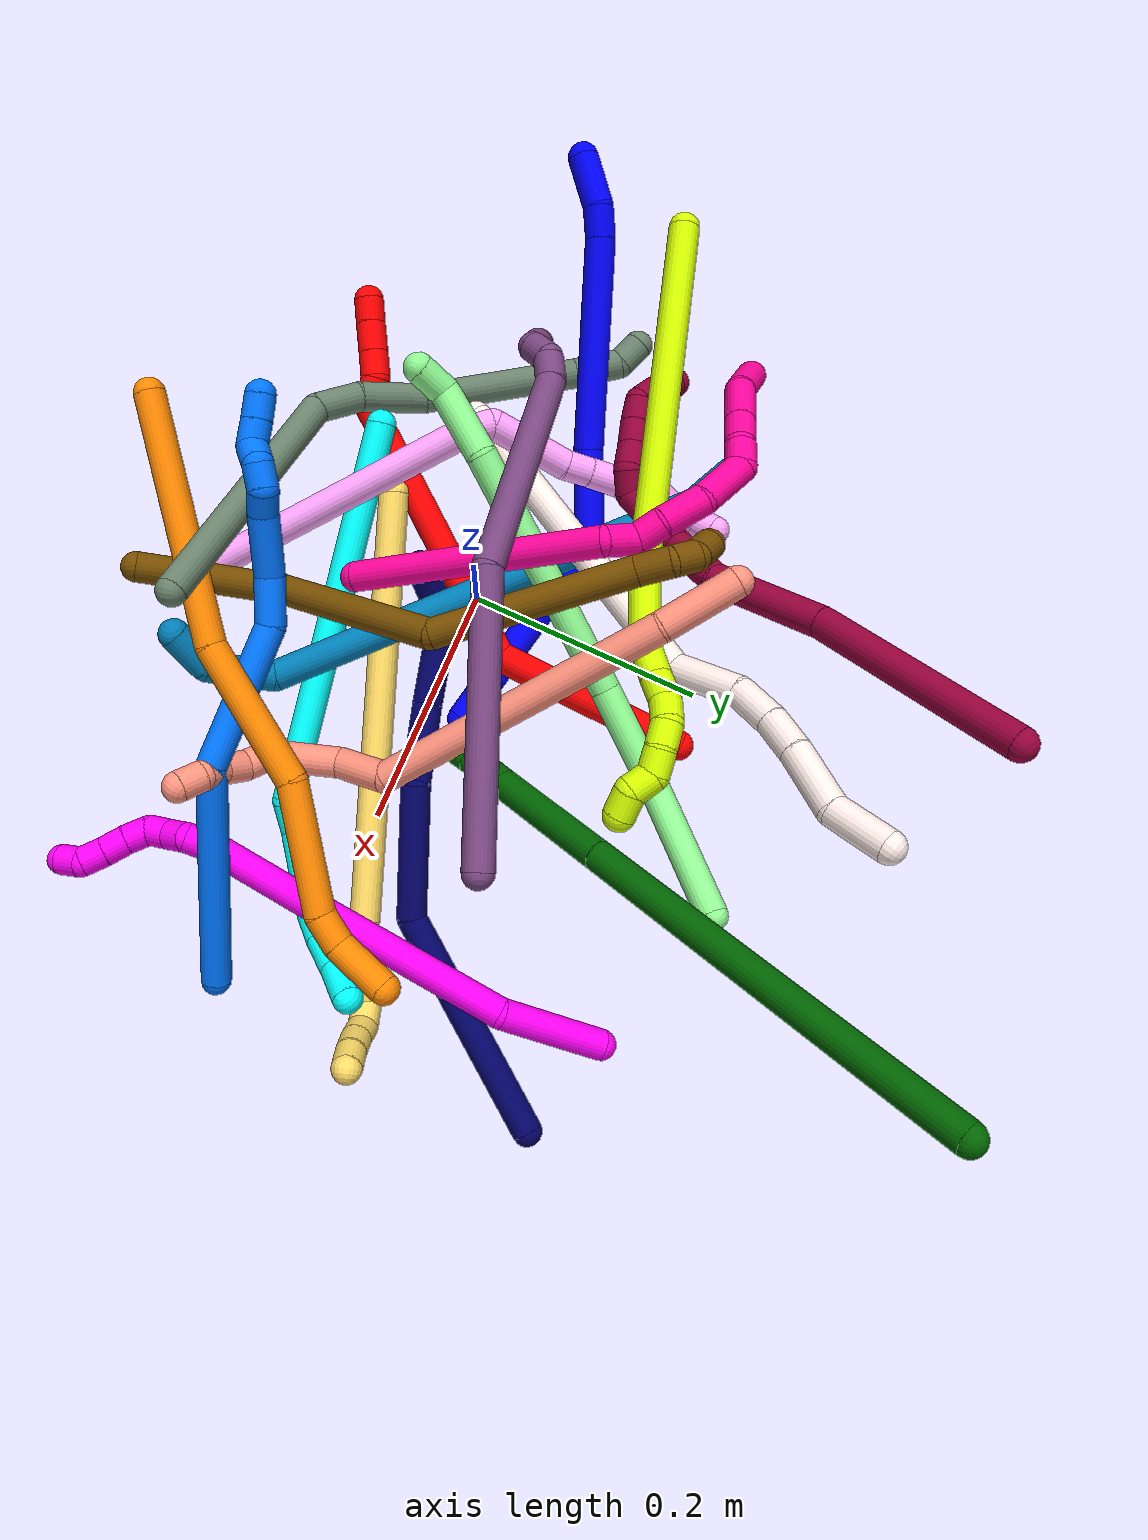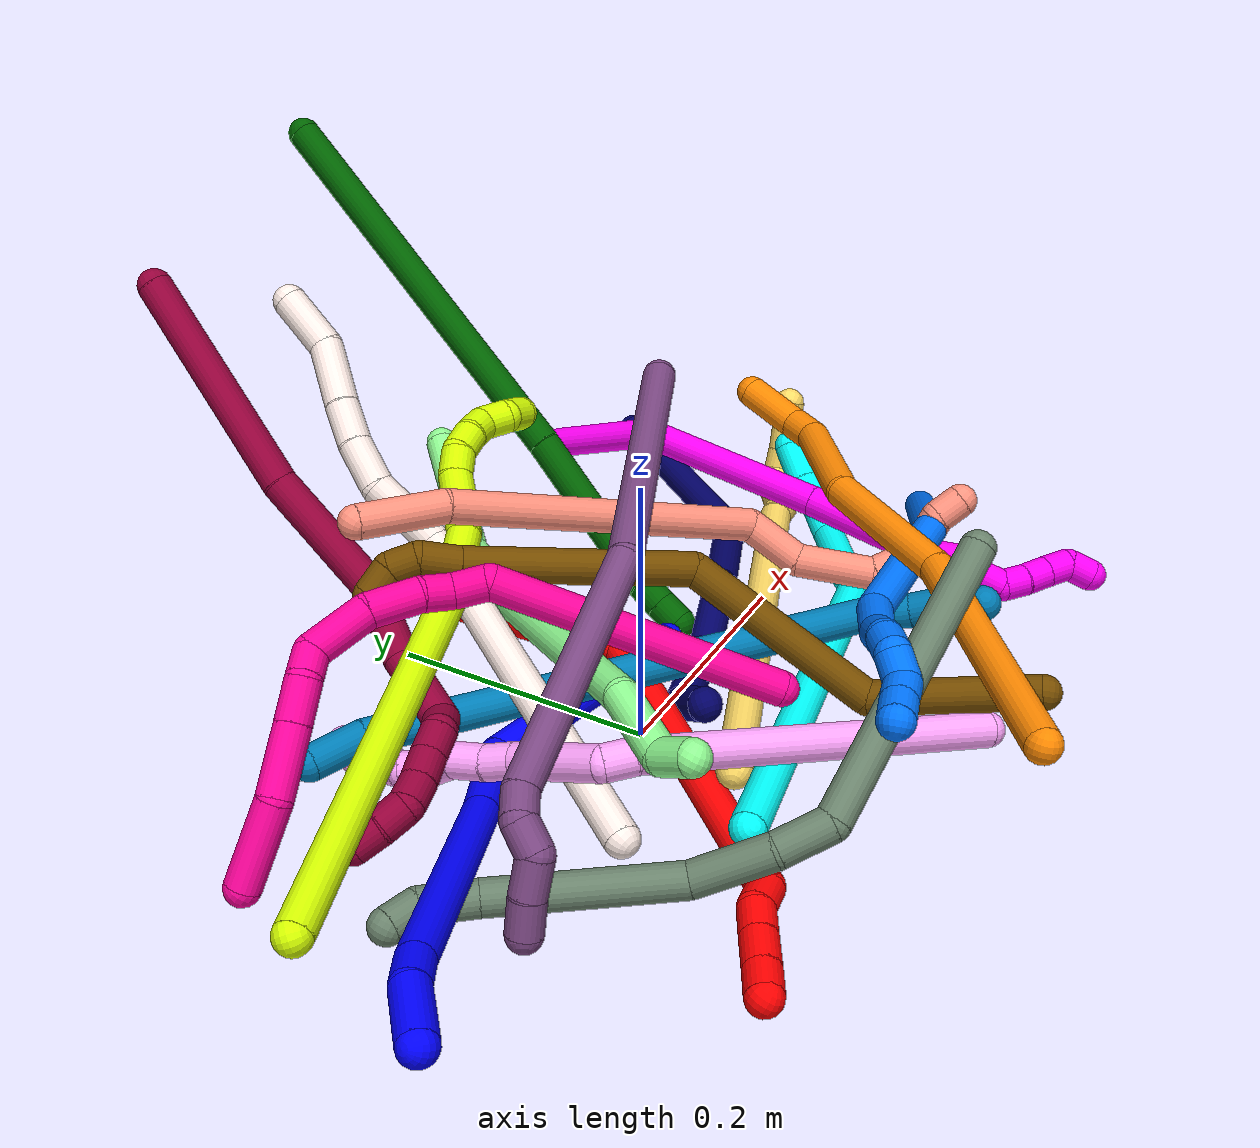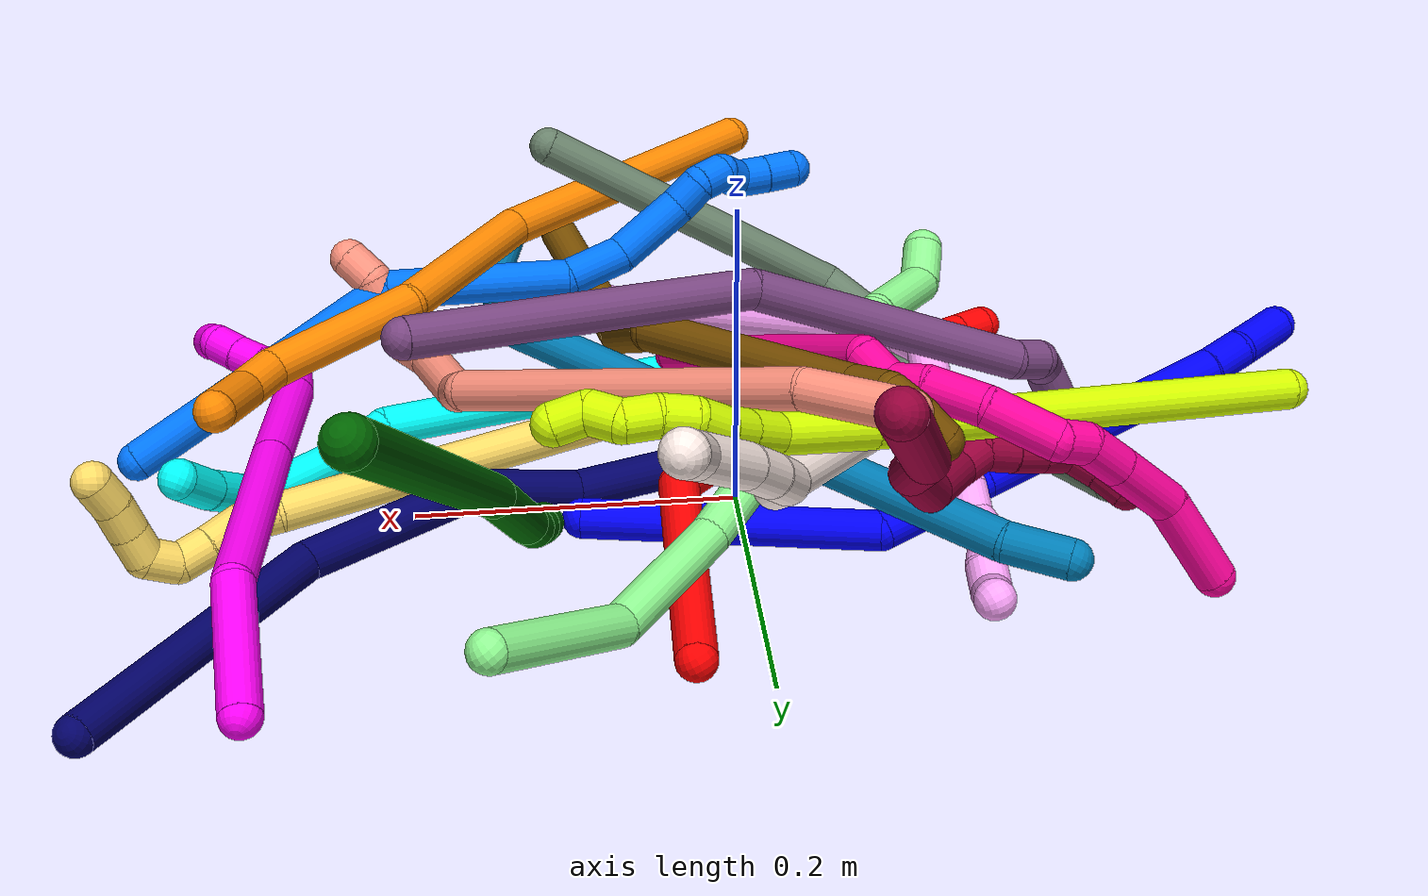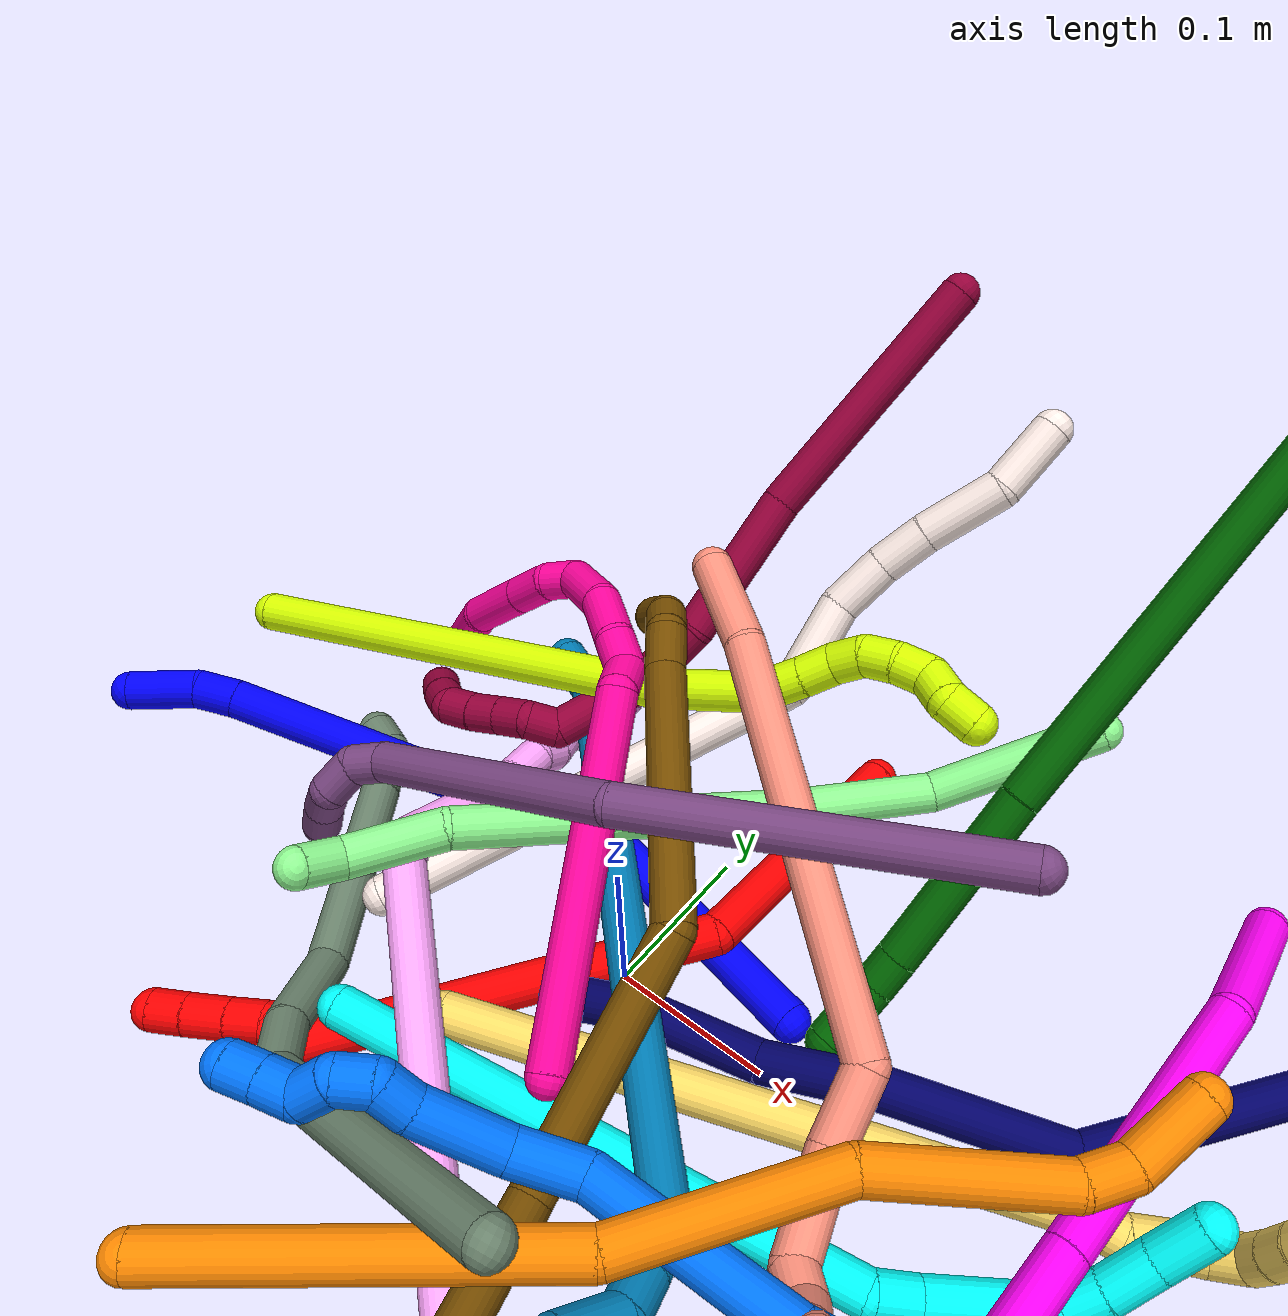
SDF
<sdf version="1.7">
 <world name="default">
  <plugin name="TubeGeneratorPlugin" filename="libtube_generator_plugin.so"/>
  <model name="photoneo_s_sensor">
   <static>1</static>
   <pose>0 0 2 1.57079 1.57079 3.14159</pose>
   <link name="link">
    <inertial><mass>0.1</mass></inertial>
    <sensor name="sensor" type="depth">
     <update_rate>30</update_rate>
     <camera>
      <horizontal_fov>1.22</horizontal_fov>
      <image><width>1920</width><height>1200</height><format>B8G8R8</format></image>
      <clip><near>0.1</near><far>4</far></clip>
      <depth_camera><output>points</output></depth_camera>
     </camera>
     <plugin name="camera_plugin" filename="libgazebo_ros_depth_camera.so">
      <baseline>0.2</baseline>
      <alwaysOn>1</alwaysOn>
      <updateRate>0.0</updateRate>
      <cameraName>camera_ir</cameraName>
      <imageTopicName>/camera/color/image_raw</imageTopicName>
      <cameraInfoTopicName>/camera/color/camera_info</cameraInfoTopicName>
      <depthImageTopicName>/camera/depth/image_raw</depthImageTopicName>
      <depthImageCameraInfoTopicName>/camera/depth/camera_info</depthImageCameraInfoTopicName>
      <pointCloudTopicName>/camera/depth/points</pointCloudTopicName>
      <frameName>fr_optical</frameName>
      <pointCloudCutoff>0.1</pointCloudCutoff>
      <pointCloudCutoffMax>2.0</pointCloudCutoffMax>
      <distortionK1>0</distortionK1>
      <distortionK2>0</distortionK2>
      <distortionK3>0</distortionK3>
      <distortionT1>0</distortionT1>
      <distortionT2>0</distortionT2>
      <CxPrime>0</CxPrime>
      <Cx>0</Cx>
      <Cy>0</Cy>
      <focalLength>0</focalLength>
      <hackBaseline>0</hackBaseline>
     </plugin>
    </sensor>
   </link>
  </model>
  <gravity>0 0 -9.8</gravity>
  <magnetic_field>6e-06 2.3e-05 -4.2e-05</magnetic_field>
  <atmosphere type="adiabatic"/>
  <physics name="default_physics" default="0" type="ode">
   <max_step_size>0.003</max_step_size>
   <real_time_factor>1</real_time_factor>
   <real_time_update_rate>1000</real_time_update_rate>
   <max_contacts>10000</max_contacts>
   <ode>
    <solver>
     <type>quick</type>
     <iters>100</iters>
     <sor>1.3</sor>
     <use_dynamic_moi_rescaling>0</use_dynamic_moi_rescaling>
    </solver>
    <constraints>
     <contact_max_correcting_vel>0</contact_max_correcting_vel>
     <contact_surface_layer>0.001</contact_surface_layer>
     <cfm>0</cfm>
     <erp>0.2</erp>
    </constraints>
   </ode>
  </physics>
  <scene><ambient>0.4 0.4 0.4 1</ambient><background>0.7 0.7 0.7 1</background><shadows>0</shadows></scene>
  <audio><device>default</device></audio>
  <spherical_coordinates>
   <surface_model>EARTH_WGS84</surface_model>
   <latitude_deg>0</latitude_deg>
   <longitude_deg>0</longitude_deg>
   <elevation>0</elevation>
   <heading_deg>0</heading_deg>
  </spherical_coordinates>
  <model name="bin">
   <static>1</static>
   <link name="bottom">
    <collision name="collision-bottom">
     <pose>0 0 -0.01 0 -0 0</pose>
     <geometry><box><size>0.8 0.6 0.02</size></box></geometry>
     <surface>
      <friction><ode><mu>100</mu><mu2>100</mu2></ode></friction>
      <contact><collide_bitmask>65535</collide_bitmask></contact>
     </surface>
    </collision>
   </link>
   <link name="west_wall">
    <collision name="collision-west_wall">
     <pose>-0.41 0 0.1 0 -0 0</pose>
     <geometry><box><size>0.02 0.6 0.2</size></box></geometry>
     <surface>
      <friction><ode><mu>100</mu><mu2>100</mu2></ode></friction>
      <contact><collide_bitmask>65535</collide_bitmask></contact>
     </surface>
    </collision>
   </link>
   <link name="east_wall">
    <collision name="collision-east_wall">
     <pose>0.41 0 0.1 0 -0 0</pose>
     <geometry><box><size>0.02 0.6 0.2</size></box></geometry>
     <surface>
      <friction><ode><mu>100</mu><mu2>100</mu2></ode></friction>
      <contact><collide_bitmask>65535</collide_bitmask></contact>
     </surface>
    </collision>
   </link>
   <link name="south_wall">
    <collision name="collision-south_wall">
     <pose>0 -0.31 0.1 0 -0 0</pose>
     <geometry><box><size>0.8 0.02 0.2</size></box></geometry>
     <surface>
      <friction><ode><mu>100</mu><mu2>100</mu2></ode></friction>
      <contact><collide_bitmask>65535</collide_bitmask></contact>
     </surface>
    </collision>
   </link>
   <link name="north_wall">
    <collision name="collision-north_wall">
     <pose>0 0.31 0.1 0 -0 0</pose>
     <geometry><box><size>0.8 0.02 0.2</size></box></geometry>
     <surface>
      <friction><ode><mu>100</mu><mu2>100</mu2></ode></friction>
      <contact><collide_bitmask>65535</collide_bitmask></contact>
     </surface>
    </collision>
   </link>
  </model>
  <model name="1">
   <static>0</static>
   <link name="1">
    <collision name="collision-cylinder-e_1_1_4">
     <pose>-0.036097 0.025027 0.07997 -0.303299 -0.406751 0.063011</pose>
     <geometry><cylinder><radius>0.0125</radius><length>0.182478</length></cylinder></geometry>
     <surface>
      <friction><ode><mu>1.16</mu><mu2>1.16</mu2><slip1>0</slip1><slip2>0</slip2></ode></friction>
      <contact><ode><kp>1e+06</kp><kd>1</kd><max_vel>0</max_vel><min_depth>0.001</min_depth></ode></contact>
     </surface>
    </collision>
    <visual name="visual-cylinder-e_1_1_4">
     <pose>-0.036097 0.025027 0.07997 -0.303299 -0.406751 0.063011</pose>
     <geometry><cylinder><radius>0.0125</radius><length>0.182478</length></cylinder></geometry>
     <material><ambient>0 0 1 1</ambient></material>
    </visual>
    <collision name="collision-cylinder-e_2_4_5">
     <pose>-0.092935 0.037105 0.189473 0.413216 -0.571596 -0.123023</pose>
     <geometry><cylinder><radius>0.0125</radius><length>0.076683</length></cylinder></geometry>
     <surface>
      <friction><ode><mu>1.16</mu><mu2>1.16</mu2><slip1>0</slip1><slip2>0</slip2></ode></friction>
      <contact><ode><kp>1e+06</kp><kd>1</kd><max_vel>0</max_vel><min_depth>0.001</min_depth></ode></contact>
     </surface>
    </collision>
    <visual name="visual-cylinder-e_2_4_5">
     <pose>-0.092935 0.037105 0.189473 0.413216 -0.571596 -0.123023</pose>
     <geometry><cylinder><radius>0.0125</radius><length>0.076683</length></cylinder></geometry>
     <material><ambient>0 0 1 1</ambient></material>
    </visual>
    <collision name="collision-cylinder-e_3_5_6">
     <pose>-0.155517 -0.002367 0.289319 0.360719 -0.508012 -0.094606</pose>
     <geometry><cylinder><radius>0.0125</radius><length>0.172024</length></cylinder></geometry>
     <surface>
      <friction><ode><mu>1.16</mu><mu2>1.16</mu2><slip1>0</slip1><slip2>0</slip2></ode></friction>
      <contact><ode><kp>1e+06</kp><kd>1</kd><max_vel>0</max_vel><min_depth>0.001</min_depth></ode></contact>
     </surface>
    </collision>
    <visual name="visual-cylinder-e_3_5_6">
     <pose>-0.155517 -0.002367 0.289319 0.360719 -0.508012 -0.094606</pose>
     <geometry><cylinder><radius>0.0125</radius><length>0.172024</length></cylinder></geometry>
     <material><ambient>0 0 1 1</ambient></material>
    </visual>
    <collision name="collision-cylinder-e_4_6_7">
     <pose>-0.204007 -0.034313 0.369371 0.507965 -0.538006 -0.142885</pose>
     <geometry><cylinder><radius>0.0125</radius><length>0.025959</length></cylinder></geometry>
     <surface>
      <friction><ode><mu>1.16</mu><mu2>1.16</mu2><slip1>0</slip1><slip2>0</slip2></ode></friction>
      <contact><ode><kp>1e+06</kp><kd>1</kd><max_vel>0</max_vel><min_depth>0.001</min_depth></ode></contact>
     </surface>
    </collision>
    <visual name="visual-cylinder-e_4_6_7">
     <pose>-0.204007 -0.034313 0.369371 0.507965 -0.538006 -0.142885</pose>
     <geometry><cylinder><radius>0.0125</radius><length>0.025959</length></cylinder></geometry>
     <material><ambient>0 0 1 1</ambient></material>
    </visual>
    <collision name="collision-cylinder-e_5_7_2">
     <pose>-0.22544 -0.050015 0.390727 0.724483 -0.761237 -0.300977</pose>
     <geometry><cylinder><radius>0.0125</radius><length>0.042856</length></cylinder></geometry>
     <surface>
      <friction><ode><mu>1.16</mu><mu2>1.16</mu2><slip1>0</slip1><slip2>0</slip2></ode></friction>
      <contact><ode><kp>1e+06</kp><kd>1</kd><max_vel>0</max_vel><min_depth>0.001</min_depth></ode></contact>
     </surface>
    </collision>
    <visual name="visual-cylinder-e_5_7_2">
     <pose>-0.22544 -0.050015 0.390727 0.724483 -0.761237 -0.300977</pose>
     <geometry><cylinder><radius>0.0125</radius><length>0.042856</length></cylinder></geometry>
     <material><ambient>0 0 1 1</ambient></material>
    </visual>
    <collision name="collision-sphere-2">
     <pose>-0.240221 -0.060297 0.402344 0 -0 0</pose>
     <geometry><sphere><radius>0.0125</radius></sphere></geometry>
     <surface>
      <friction><ode><mu>1.16</mu><mu2>1.16</mu2><slip1>0</slip1><slip2>0</slip2></ode></friction>
      <contact><ode><kp>1e+06</kp><kd>1</kd><max_vel>0</max_vel><min_depth>0.001</min_depth></ode></contact>
     </surface>
    </collision>
    <visual name="visual-sphere-2">
     <pose>-0.240221 -0.060297 0.402344 0 -0 0</pose>
     <geometry><sphere><radius>0.0125</radius></sphere></geometry>
     <material><ambient>0 0 1 1</ambient></material>
    </visual>
    <collision name="collision-sphere-7">
     <pose>-0.210658 -0.039734 0.379109 0 -0 0</pose>
     <geometry><sphere><radius>0.0125</radius></sphere></geometry>
     <surface>
      <friction><ode><mu>1.16</mu><mu2>1.16</mu2><slip1>0</slip1><slip2>0</slip2></ode></friction>
      <contact><ode><kp>1e+06</kp><kd>1</kd><max_vel>0</max_vel><min_depth>0.001</min_depth></ode></contact>
     </surface>
    </collision>
    <visual name="visual-sphere-7">
     <pose>-0.210658 -0.039734 0.379109 0 -0 0</pose>
     <geometry><sphere><radius>0.0125</radius></sphere></geometry>
     <material><ambient>0 0 1 1</ambient></material>
    </visual>
    <collision name="collision-sphere-6">
     <pose>-0.197356 -0.028891 0.359633 0 -0 0</pose>
     <geometry><sphere><radius>0.0125</radius></sphere></geometry>
     <surface>
      <friction><ode><mu>1.16</mu><mu2>1.16</mu2><slip1>0</slip1><slip2>0</slip2></ode></friction>
      <contact><ode><kp>1e+06</kp><kd>1</kd><max_vel>0</max_vel><min_depth>0.001</min_depth></ode></contact>
     </surface>
    </collision>
    <visual name="visual-sphere-6">
     <pose>-0.197356 -0.028891 0.359633 0 -0 0</pose>
     <geometry><sphere><radius>0.0125</radius></sphere></geometry>
     <material><ambient>0 0 1 1</ambient></material>
    </visual>
    <collision name="collision-sphere-5">
     <pose>-0.113677 0.024156 0.219006 0 -0 0</pose>
     <geometry><sphere><radius>0.0125</radius></sphere></geometry>
     <surface>
      <friction><ode><mu>1.16</mu><mu2>1.16</mu2><slip1>0</slip1><slip2>0</slip2></ode></friction>
      <contact><ode><kp>1e+06</kp><kd>1</kd><max_vel>0</max_vel><min_depth>0.001</min_depth></ode></contact>
     </surface>
    </collision>
    <visual name="visual-sphere-5">
     <pose>-0.113677 0.024156 0.219006 0 -0 0</pose>
     <geometry><sphere><radius>0.0125</radius></sphere></geometry>
     <material><ambient>0 0 1 1</ambient></material>
    </visual>
    <collision name="collision-sphere-1">
     <geometry><sphere><radius>0.0125</radius></sphere></geometry>
     <surface>
      <friction><ode><mu>1.16</mu><mu2>1.16</mu2><slip1>0</slip1><slip2>0</slip2></ode></friction>
      <contact><ode><kp>1e+06</kp><kd>1</kd><max_vel>0</max_vel><min_depth>0.001</min_depth></ode></contact>
     </surface>
    </collision>
    <visual name="visual-sphere-1">
     <geometry><sphere><radius>0.0125</radius></sphere></geometry>
     <material><ambient>0 0 1 1</ambient></material>
    </visual>
    <collision name="collision-sphere-4">
     <pose>-0.072193 0.050054 0.159941 0 -0 0</pose>
     <geometry><sphere><radius>0.0125</radius></sphere></geometry>
     <surface>
      <friction><ode><mu>1.16</mu><mu2>1.16</mu2><slip1>0</slip1><slip2>0</slip2></ode></friction>
      <contact><ode><kp>1e+06</kp><kd>1</kd><max_vel>0</max_vel><min_depth>0.001</min_depth></ode></contact>
     </surface>
    </collision>
    <visual name="visual-sphere-4">
     <pose>-0.072193 0.050054 0.159941 0 -0 0</pose>
     <geometry><sphere><radius>0.0125</radius></sphere></geometry>
     <material><ambient>0 0 1 1</ambient></material>
    </visual>
    <inertial>
     <pose>-0.110847 0.007942 0.210451 0 -0 0</pose>
     <mass>0.5</mass>
     <inertia>
      <ixx>0.000856</ixx>
      <ixy>0</ixy>
      <ixz>0</ixz>
      <iyy>0.000932</iyy>
      <iyz>0</iyz>
      <izz>0.000484</izz>
     </inertia>
    </inertial>
   </link>
   <pose>0.097722 0.031216 0.011496 -0.795081 -0.795583 0.758965</pose>
  </model>
  <model name="2">
   <static>0</static>
   <link name="2">
    <collision name="collision-cylinder-e_1_1_4">
     <pose>-0.042284 -0.063169 0.031281 1.11099 -0.540317 -0.340449</pose>
     <geometry><cylinder><radius>0.0125</radius><length>0.164398</length></cylinder></geometry>
     <surface>
      <friction><ode><mu>1.16</mu><mu2>1.16</mu2><slip1>0</slip1><slip2>0</slip2></ode></friction>
      <contact><ode><kp>1e+06</kp><kd>1</kd><max_vel>0</max_vel><min_depth>0.001</min_depth></ode></contact>
     </surface>
    </collision>
    <visual name="visual-cylinder-e_1_1_4">
     <pose>-0.042284 -0.063169 0.031281 1.11099 -0.540317 -0.340449</pose>
     <geometry><cylinder><radius>0.0125</radius><length>0.164398</length></cylinder></geometry>
     <material><ambient>1 0 0 1</ambient></material>
    </visual>
    <collision name="collision-cylinder-e_2_4_5">
     <pose>-0.189798 -0.185622 0.052059 1.74614 -1.0511 -1.21032</pose>
     <geometry><cylinder><radius>0.0125</radius><length>0.242474</length></cylinder></geometry>
     <surface>
      <friction><ode><mu>1.16</mu><mu2>1.16</mu2><slip1>0</slip1><slip2>0</slip2></ode></friction>
      <contact><ode><kp>1e+06</kp><kd>1</kd><max_vel>0</max_vel><min_depth>0.001</min_depth></ode></contact>
     </surface>
    </collision>
    <visual name="visual-cylinder-e_2_4_5">
     <pose>-0.189798 -0.185622 0.052059 1.74614 -1.0511 -1.21032</pose>
     <geometry><cylinder><radius>0.0125</radius><length>0.242474</length></cylinder></geometry>
     <material><ambient>1 0 0 1</ambient></material>
    </visual>
    <collision name="collision-cylinder-e_3_5_6">
     <pose>-0.306062 -0.242159 0.038729 -2.37052 -1.22769 2.09649</pose>
     <geometry><cylinder><radius>0.0125</radius><length>0.023434</length></cylinder></geometry>
     <surface>
      <friction><ode><mu>1.16</mu><mu2>1.16</mu2><slip1>0</slip1><slip2>0</slip2></ode></friction>
      <contact><ode><kp>1e+06</kp><kd>1</kd><max_vel>0</max_vel><min_depth>0.001</min_depth></ode></contact>
     </surface>
    </collision>
    <visual name="visual-cylinder-e_3_5_6">
     <pose>-0.306062 -0.242159 0.038729 -2.37052 -1.22769 2.09649</pose>
     <geometry><cylinder><radius>0.0125</radius><length>0.023434</length></cylinder></geometry>
     <material><ambient>1 0 0 1</ambient></material>
    </visual>
    <collision name="collision-cylinder-e_4_6_7">
     <pose>-0.327721 -0.241369 0.032794 2.57977 -1.23793 -2.37188</pose>
     <geometry><cylinder><radius>0.0125</radius><length>0.022483</length></cylinder></geometry>
     <surface>
      <friction><ode><mu>1.16</mu><mu2>1.16</mu2><slip1>0</slip1><slip2>0</slip2></ode></friction>
      <contact><ode><kp>1e+06</kp><kd>1</kd><max_vel>0</max_vel><min_depth>0.001</min_depth></ode></contact>
     </surface>
    </collision>
    <visual name="visual-cylinder-e_4_6_7">
     <pose>-0.327721 -0.241369 0.032794 2.57977 -1.23793 -2.37188</pose>
     <geometry><cylinder><radius>0.0125</radius><length>0.022483</length></cylinder></geometry>
     <material><ambient>1 0 0 1</ambient></material>
    </visual>
    <collision name="collision-cylinder-e_5_7_8">
     <pose>-0.350797 -0.245343 0.026674 2.55146 -1.28756 -2.37195</pose>
     <geometry><cylinder><radius>0.0125</radius><length>0.025937</length></cylinder></geometry>
     <surface>
      <friction><ode><mu>1.16</mu><mu2>1.16</mu2><slip1>0</slip1><slip2>0</slip2></ode></friction>
      <contact><ode><kp>1e+06</kp><kd>1</kd><max_vel>0</max_vel><min_depth>0.001</min_depth></ode></contact>
     </surface>
    </collision>
    <visual name="visual-cylinder-e_5_7_8">
     <pose>-0.350797 -0.245343 0.026674 2.55146 -1.28756 -2.37195</pose>
     <geometry><cylinder><radius>0.0125</radius><length>0.025937</length></cylinder></geometry>
     <material><ambient>1 0 0 1</ambient></material>
    </visual>
    <collision name="collision-cylinder-e_6_8_2">
     <pose>-0.373508 -0.248789 0.021241 2.60835 -1.3033 -2.45394</pose>
     <geometry><cylinder><radius>0.0125</radius><length>0.021274</length></cylinder></geometry>
     <surface>
      <friction><ode><mu>1.16</mu><mu2>1.16</mu2><slip1>0</slip1><slip2>0</slip2></ode></friction>
      <contact><ode><kp>1e+06</kp><kd>1</kd><max_vel>0</max_vel><min_depth>0.001</min_depth></ode></contact>
     </surface>
    </collision>
    <visual name="visual-cylinder-e_6_8_2">
     <pose>-0.373508 -0.248789 0.021241 2.60835 -1.3033 -2.45394</pose>
     <geometry><cylinder><radius>0.0125</radius><length>0.021274</length></cylinder></geometry>
     <material><ambient>1 0 0 1</ambient></material>
    </visual>
    <collision name="collision-sphere-2">
     <pose>-0.383766 -0.250218 0.01882 0 -0 0</pose>
     <geometry><sphere><radius>0.0125</radius></sphere></geometry>
     <surface>
      <friction><ode><mu>1.16</mu><mu2>1.16</mu2><slip1>0</slip1><slip2>0</slip2></ode></friction>
      <contact><ode><kp>1e+06</kp><kd>1</kd><max_vel>0</max_vel><min_depth>0.001</min_depth></ode></contact>
     </surface>
    </collision>
    <visual name="visual-sphere-2">
     <pose>-0.383766 -0.250218 0.01882 0 -0 0</pose>
     <geometry><sphere><radius>0.0125</radius></sphere></geometry>
     <material><ambient>1 0 0 1</ambient></material>
    </visual>
    <collision name="collision-sphere-4">
     <pose>-0.084568 -0.126337 0.062562 0 -0 0</pose>
     <geometry><sphere><radius>0.0125</radius></sphere></geometry>
     <surface>
      <friction><ode><mu>1.16</mu><mu2>1.16</mu2><slip1>0</slip1><slip2>0</slip2></ode></friction>
      <contact><ode><kp>1e+06</kp><kd>1</kd><max_vel>0</max_vel><min_depth>0.001</min_depth></ode></contact>
     </surface>
    </collision>
    <visual name="visual-sphere-4">
     <pose>-0.084568 -0.126337 0.062562 0 -0 0</pose>
     <geometry><sphere><radius>0.0125</radius></sphere></geometry>
     <material><ambient>1 0 0 1</ambient></material>
    </visual>
    <collision name="collision-sphere-1">
     <geometry><sphere><radius>0.0125</radius></sphere></geometry>
     <surface>
      <friction><ode><mu>1.16</mu><mu2>1.16</mu2><slip1>0</slip1><slip2>0</slip2></ode></friction>
      <contact><ode><kp>1e+06</kp><kd>1</kd><max_vel>0</max_vel><min_depth>0.001</min_depth></ode></contact>
     </surface>
    </collision>
    <visual name="visual-sphere-1">
     <geometry><sphere><radius>0.0125</radius></sphere></geometry>
     <material><ambient>1 0 0 1</ambient></material>
    </visual>
    <collision name="collision-sphere-8">
     <pose>-0.363249 -0.247359 0.023663 0 -0 0</pose>
     <geometry><sphere><radius>0.0125</radius></sphere></geometry>
     <surface>
      <friction><ode><mu>1.16</mu><mu2>1.16</mu2><slip1>0</slip1><slip2>0</slip2></ode></friction>
      <contact><ode><kp>1e+06</kp><kd>1</kd><max_vel>0</max_vel><min_depth>0.001</min_depth></ode></contact>
     </surface>
    </collision>
    <visual name="visual-sphere-8">
     <pose>-0.363249 -0.247359 0.023663 0 -0 0</pose>
     <geometry><sphere><radius>0.0125</radius></sphere></geometry>
     <material><ambient>1 0 0 1</ambient></material>
    </visual>
    <collision name="collision-sphere-5">
     <pose>-0.295029 -0.244906 0.041556 0 -0 0</pose>
     <geometry><sphere><radius>0.0125</radius></sphere></geometry>
     <surface>
      <friction><ode><mu>1.16</mu><mu2>1.16</mu2><slip1>0</slip1><slip2>0</slip2></ode></friction>
      <contact><ode><kp>1e+06</kp><kd>1</kd><max_vel>0</max_vel><min_depth>0.001</min_depth></ode></contact>
     </surface>
    </collision>
    <visual name="visual-sphere-5">
     <pose>-0.295029 -0.244906 0.041556 0 -0 0</pose>
     <geometry><sphere><radius>0.0125</radius></sphere></geometry>
     <material><ambient>1 0 0 1</ambient></material>
    </visual>
    <collision name="collision-sphere-6">
     <pose>-0.317096 -0.239412 0.035902 0 -0 0</pose>
     <geometry><sphere><radius>0.0125</radius></sphere></geometry>
     <surface>
      <friction><ode><mu>1.16</mu><mu2>1.16</mu2><slip1>0</slip1><slip2>0</slip2></ode></friction>
      <contact><ode><kp>1e+06</kp><kd>1</kd><max_vel>0</max_vel><min_depth>0.001</min_depth></ode></contact>
     </surface>
    </collision>
    <visual name="visual-sphere-6">
     <pose>-0.317096 -0.239412 0.035902 0 -0 0</pose>
     <geometry><sphere><radius>0.0125</radius></sphere></geometry>
     <material><ambient>1 0 0 1</ambient></material>
    </visual>
    <collision name="collision-sphere-7">
     <pose>-0.338345 -0.243326 0.029685 0 -0 0</pose>
     <geometry><sphere><radius>0.0125</radius></sphere></geometry>
     <surface>
      <friction><ode><mu>1.16</mu><mu2>1.16</mu2><slip1>0</slip1><slip2>0</slip2></ode></friction>
      <contact><ode><kp>1e+06</kp><kd>1</kd><max_vel>0</max_vel><min_depth>0.001</min_depth></ode></contact>
     </surface>
    </collision>
    <visual name="visual-sphere-7">
     <pose>-0.338345 -0.243326 0.029685 0 -0 0</pose>
     <geometry><sphere><radius>0.0125</radius></sphere></geometry>
     <material><ambient>1 0 0 1</ambient></material>
    </visual>
    <inertial>
     <pose>-0.169115 -0.156302 0.041108 0 -0 0</pose>
     <mass>0.5</mass>
     <inertia>
      <ixx>-0.000182</ixx>
      <ixy>0</ixy>
      <ixz>0</ixz>
      <iyy>0.000423</iyy>
      <iyz>0</iyz>
      <izz>0.002118</izz>
     </inertia>
    </inertial>
   </link>
   <pose>0.044883 0.202432 0.024365 0.522041 0.244905 0.50483</pose>
  </model>
  <model name="3">
   <static>0</static>
   <link name="3">
    <collision name="collision-cylinder-e_1_1_4">
     <pose>0.125137 0.047709 0.086298 -0.505022 0.903416 -0.249067</pose>
     <geometry><cylinder><radius>0.0125</radius><length>0.318639</length></cylinder></geometry>
     <surface>
      <friction><ode><mu>1.16</mu><mu2>1.16</mu2><slip1>0</slip1><slip2>0</slip2></ode></friction>
      <contact><ode><kp>1e+06</kp><kd>1</kd><max_vel>0</max_vel><min_depth>0.001</min_depth></ode></contact>
     </surface>
    </collision>
    <visual name="visual-cylinder-e_1_1_4">
     <pose>0.125137 0.047709 0.086298 -0.505022 0.903416 -0.249067</pose>
     <geometry><cylinder><radius>0.0125</radius><length>0.318639</length></cylinder></geometry>
     <material><ambient>0.003922 1 0.996078 1</ambient></material>
    </visual>
    <collision name="collision-cylinder-e_2_4_5">
     <pose>0.256716 0.095109 0.183664 0.027909 0.526931 0.007528</pose>
     <geometry><cylinder><radius>0.0125</radius><length>0.025621</length></cylinder></geometry>
     <surface>
      <friction><ode><mu>1.16</mu><mu2>1.16</mu2><slip1>0</slip1><slip2>0</slip2></ode></friction>
      <contact><ode><kp>1e+06</kp><kd>1</kd><max_vel>0</max_vel><min_depth>0.001</min_depth></ode></contact>
     </surface>
    </collision>
    <visual name="visual-cylinder-e_2_4_5">
     <pose>0.256716 0.095109 0.183664 0.027909 0.526931 0.007528</pose>
     <geometry><cylinder><radius>0.0125</radius><length>0.025621</length></cylinder></geometry>
     <material><ambient>0.003922 1 0.996078 1</ambient></material>
    </visual>
    <collision name="collision-cylinder-e_3_5_6">
     <pose>0.287658 0.091734 0.219767 0.12188 0.77089 0.049503</pose>
     <geometry><cylinder><radius>0.0125</radius><length>0.070324</length></cylinder></geometry>
     <surface>
      <friction><ode><mu>1.16</mu><mu2>1.16</mu2><slip1>0</slip1><slip2>0</slip2></ode></friction>
      <contact><ode><kp>1e+06</kp><kd>1</kd><max_vel>0</max_vel><min_depth>0.001</min_depth></ode></contact>
     </surface>
    </collision>
    <visual name="visual-cylinder-e_3_5_6">
     <pose>0.287658 0.091734 0.219767 0.12188 0.77089 0.049503</pose>
     <geometry><cylinder><radius>0.0125</radius><length>0.070324</length></cylinder></geometry>
     <material><ambient>0.003922 1 0.996078 1</ambient></material>
    </visual>
    <collision name="collision-cylinder-e_4_6_7">
     <pose>0.322432 0.08258 0.248193 1.06242 0.974793 0.603815</pose>
     <geometry><cylinder><radius>0.0125</radius><length>0.02483</length></cylinder></geometry>
     <surface>
      <friction><ode><mu>1.16</mu><mu2>1.16</mu2><slip1>0</slip1><slip2>0</slip2></ode></friction>
      <contact><ode><kp>1e+06</kp><kd>1</kd><max_vel>0</max_vel><min_depth>0.001</min_depth></ode></contact>
     </surface>
    </collision>
    <visual name="visual-cylinder-e_4_6_7">
     <pose>0.322432 0.08258 0.248193 1.06242 0.974793 0.603815</pose>
     <geometry><cylinder><radius>0.0125</radius><length>0.02483</length></cylinder></geometry>
     <material><ambient>0.003922 1 0.996078 1</ambient></material>
    </visual>
    <collision name="collision-cylinder-e_5_7_8">
     <pose>0.344057 0.067686 0.254592 1.24176 0.884051 0.652773</pose>
     <geometry><cylinder><radius>0.0125</radius><length>0.029354</length></cylinder></geometry>
     <surface>
      <friction><ode><mu>1.16</mu><mu2>1.16</mu2><slip1>0</slip1><slip2>0</slip2></ode></friction>
      <contact><ode><kp>1e+06</kp><kd>1</kd><max_vel>0</max_vel><min_depth>0.001</min_depth></ode></contact>
     </surface>
    </collision>
    <visual name="visual-cylinder-e_5_7_8">
     <pose>0.344057 0.067686 0.254592 1.24176 0.884051 0.652773</pose>
     <geometry><cylinder><radius>0.0125</radius><length>0.029354</length></cylinder></geometry>
     <material><ambient>0.003922 1 0.996078 1</ambient></material>
    </visual>
    <collision name="collision-cylinder-e_6_8_2">
     <pose>0.368102 0.04991 0.259097 1.40536 0.949218 0.820802</pose>
     <geometry><cylinder><radius>0.0125</radius><length>0.031233</length></cylinder></geometry>
     <surface>
      <friction><ode><mu>1.16</mu><mu2>1.16</mu2><slip1>0</slip1><slip2>0</slip2></ode></friction>
      <contact><ode><kp>1e+06</kp><kd>1</kd><max_vel>0</max_vel><min_depth>0.001</min_depth></ode></contact>
     </surface>
    </collision>
    <visual name="visual-cylinder-e_6_8_2">
     <pose>0.368102 0.04991 0.259097 1.40536 0.949218 0.820802</pose>
     <geometry><cylinder><radius>0.0125</radius><length>0.031233</length></cylinder></geometry>
     <material><ambient>0.003922 1 0.996078 1</ambient></material>
    </visual>
    <collision name="collision-sphere-2">
     <pose>0.380797 0.04094 0.260594 0 -0 0</pose>
     <geometry><sphere><radius>0.0125</radius></sphere></geometry>
     <surface>
      <friction><ode><mu>1.16</mu><mu2>1.16</mu2><slip1>0</slip1><slip2>0</slip2></ode></friction>
      <contact><ode><kp>1e+06</kp><kd>1</kd><max_vel>0</max_vel><min_depth>0.001</min_depth></ode></contact>
     </surface>
    </collision>
    <visual name="visual-sphere-2">
     <pose>0.380797 0.04094 0.260594 0 -0 0</pose>
     <geometry><sphere><radius>0.0125</radius></sphere></geometry>
     <material><ambient>0.003922 1 0.996078 1</ambient></material>
    </visual>
    <collision name="collision-sphere-4">
     <pose>0.250274 0.095418 0.172596 0 -0 0</pose>
     <geometry><sphere><radius>0.0125</radius></sphere></geometry>
     <surface>
      <friction><ode><mu>1.16</mu><mu2>1.16</mu2><slip1>0</slip1><slip2>0</slip2></ode></friction>
      <contact><ode><kp>1e+06</kp><kd>1</kd><max_vel>0</max_vel><min_depth>0.001</min_depth></ode></contact>
     </surface>
    </collision>
    <visual name="visual-sphere-4">
     <pose>0.250274 0.095418 0.172596 0 -0 0</pose>
     <geometry><sphere><radius>0.0125</radius></sphere></geometry>
     <material><ambient>0.003922 1 0.996078 1</ambient></material>
    </visual>
    <collision name="collision-sphere-1">
     <geometry><sphere><radius>0.0125</radius></sphere></geometry>
     <surface>
      <friction><ode><mu>1.16</mu><mu2>1.16</mu2><slip1>0</slip1><slip2>0</slip2></ode></friction>
      <contact><ode><kp>1e+06</kp><kd>1</kd><max_vel>0</max_vel><min_depth>0.001</min_depth></ode></contact>
     </surface>
    </collision>
    <visual name="visual-sphere-1">
     <geometry><sphere><radius>0.0125</radius></sphere></geometry>
     <material><ambient>0.003922 1 0.996078 1</ambient></material>
    </visual>
    <collision name="collision-sphere-8">
     <pose>0.355406 0.058879 0.257599 0 -0 0</pose>
     <geometry><sphere><radius>0.0125</radius></sphere></geometry>
     <surface>
      <friction><ode><mu>1.16</mu><mu2>1.16</mu2><slip1>0</slip1><slip2>0</slip2></ode></friction>
      <contact><ode><kp>1e+06</kp><kd>1</kd><max_vel>0</max_vel><min_depth>0.001</min_depth></ode></contact>
     </surface>
    </collision>
    <visual name="visual-sphere-8">
     <pose>0.355406 0.058879 0.257599 0 -0 0</pose>
     <geometry><sphere><radius>0.0125</radius></sphere></geometry>
     <material><ambient>0.003922 1 0.996078 1</ambient></material>
    </visual>
    <collision name="collision-sphere-5">
     <pose>0.263158 0.0948 0.194732 0 -0 0</pose>
     <geometry><sphere><radius>0.0125</radius></sphere></geometry>
     <surface>
      <friction><ode><mu>1.16</mu><mu2>1.16</mu2><slip1>0</slip1><slip2>0</slip2></ode></friction>
      <contact><ode><kp>1e+06</kp><kd>1</kd><max_vel>0</max_vel><min_depth>0.001</min_depth></ode></contact>
     </surface>
    </collision>
    <visual name="visual-sphere-5">
     <pose>0.263158 0.0948 0.194732 0 -0 0</pose>
     <geometry><sphere><radius>0.0125</radius></sphere></geometry>
     <material><ambient>0.003922 1 0.996078 1</ambient></material>
    </visual>
    <collision name="collision-sphere-6">
     <pose>0.312158 0.088667 0.244801 0 -0 0</pose>
     <geometry><sphere><radius>0.0125</radius></sphere></geometry>
     <surface>
      <friction><ode><mu>1.16</mu><mu2>1.16</mu2><slip1>0</slip1><slip2>0</slip2></ode></friction>
      <contact><ode><kp>1e+06</kp><kd>1</kd><max_vel>0</max_vel><min_depth>0.001</min_depth></ode></contact>
     </surface>
    </collision>
    <visual name="visual-sphere-6">
     <pose>0.312158 0.088667 0.244801 0 -0 0</pose>
     <geometry><sphere><radius>0.0125</radius></sphere></geometry>
     <material><ambient>0.003922 1 0.996078 1</ambient></material>
    </visual>
    <collision name="collision-sphere-7">
     <pose>0.332707 0.076492 0.251585 0 -0 0</pose>
     <geometry><sphere><radius>0.0125</radius></sphere></geometry>
     <surface>
      <friction><ode><mu>1.16</mu><mu2>1.16</mu2><slip1>0</slip1><slip2>0</slip2></ode></friction>
      <contact><ode><kp>1e+06</kp><kd>1</kd><max_vel>0</max_vel><min_depth>0.001</min_depth></ode></contact>
     </surface>
    </collision>
    <visual name="visual-sphere-7">
     <pose>0.332707 0.076492 0.251585 0 -0 0</pose>
     <geometry><sphere><radius>0.0125</radius></sphere></geometry>
     <material><ambient>0.003922 1 0.996078 1</ambient></material>
    </visual>
    <inertial>
     <pose>0.192564 0.059372 0.138773 0 -0 0</pose>
     <mass>0.5</mass>
     <inertia>
      <ixx>0.001275</ixx>
      <ixy>0</ixy>
      <ixz>0</ixz>
      <iyy>0.002186</iyy>
      <iyz>0</iyz>
      <izz>-0.002941</izz>
     </inertia>
    </inertial>
   </link>
   <pose>-0.095487 -0.129076 0.039606 -2.60307 -0.618832 0.162422</pose>
  </model>
  <model name="4">
   <static>0</static>
   <link name="4">
    <collision name="collision-cylinder-e_1_1_4">
     <pose>-0.07148 0.080844 -0.073861 -2.31109 -0.578316 1.18717</pose>
     <geometry><cylinder><radius>0.0125</radius><length>0.261539</length></cylinder></geometry>
     <surface>
      <friction><ode><mu>1.16</mu><mu2>1.16</mu2><slip1>0</slip1><slip2>0</slip2></ode></friction>
      <contact><ode><kp>1e+06</kp><kd>1</kd><max_vel>0</max_vel><min_depth>0.001</min_depth></ode></contact>
     </surface>
    </collision>
    <visual name="visual-cylinder-e_1_1_4">
     <pose>-0.07148 0.080844 -0.073861 -2.31109 -0.578316 1.18717</pose>
     <geometry><cylinder><radius>0.0125</radius><length>0.261539</length></cylinder></geometry>
     <material><ambient>1 0.65098 0.996078 1</ambient></material>
    </visual>
    <collision name="collision-cylinder-e_2_4_5">
     <pose>-0.147331 0.170867 -0.151646 -1.97482 -0.412609 0.614114</pose>
     <geometry><cylinder><radius>0.0125</radius><length>0.021795</length></cylinder></geometry>
     <surface>
      <friction><ode><mu>1.16</mu><mu2>1.16</mu2><slip1>0</slip1><slip2>0</slip2></ode></friction>
      <contact><ode><kp>1e+06</kp><kd>1</kd><max_vel>0</max_vel><min_depth>0.001</min_depth></ode></contact>
     </surface>
    </collision>
    <visual name="visual-cylinder-e_2_4_5">
     <pose>-0.147331 0.170867 -0.151646 -1.97482 -0.412609 0.614114</pose>
     <geometry><cylinder><radius>0.0125</radius><length>0.021795</length></cylinder></geometry>
     <material><ambient>1 0.65098 0.996078 1</ambient></material>
    </visual>
    <collision name="collision-cylinder-e_3_5_6">
     <pose>-0.164438 0.209312 -0.142455 -1.14946 -0.378057 0.246555</pose>
     <geometry><cylinder><radius>0.0125</radius><length>0.069014</length></cylinder></geometry>
     <surface>
      <friction><ode><mu>1.16</mu><mu2>1.16</mu2><slip1>0</slip1><slip2>0</slip2></ode></friction>
      <contact><ode><kp>1e+06</kp><kd>1</kd><max_vel>0</max_vel><min_depth>0.001</min_depth></ode></contact>
     </surface>
    </collision>
    <visual name="visual-cylinder-e_3_5_6">
     <pose>-0.164438 0.209312 -0.142455 -1.14946 -0.378057 0.246555</pose>
     <geometry><cylinder><radius>0.0125</radius><length>0.069014</length></cylinder></geometry>
     <material><ambient>1 0.65098 0.996078 1</ambient></material>
    </visual>
    <collision name="collision-cylinder-e_4_6_7">
     <pose>-0.181338 0.248634 -0.127248 -1.36584 -0.385111 0.314597</pose>
     <geometry><cylinder><radius>0.0125</radius><length>0.022166</length></cylinder></geometry>
     <surface>
      <friction><ode><mu>1.16</mu><mu2>1.16</mu2><slip1>0</slip1><slip2>0</slip2></ode></friction>
      <contact><ode><kp>1e+06</kp><kd>1</kd><max_vel>0</max_vel><min_depth>0.001</min_depth></ode></contact>
     </surface>
    </collision>
    <visual name="visual-cylinder-e_4_6_7">
     <pose>-0.181338 0.248634 -0.127248 -1.36584 -0.385111 0.314597</pose>
     <geometry><cylinder><radius>0.0125</radius><length>0.022166</length></cylinder></geometry>
     <material><ambient>1 0.65098 0.996078 1</ambient></material>
    </visual>
    <collision name="collision-cylinder-e_5_7_8">
     <pose>-0.191837 0.269118 -0.122583 -1.32866 -0.532884 0.421113</pose>
     <geometry><cylinder><radius>0.0125</radius><length>0.02494</length></cylinder></geometry>
     <surface>
      <friction><ode><mu>1.16</mu><mu2>1.16</mu2><slip1>0</slip1><slip2>0</slip2></ode></friction>
      <contact><ode><kp>1e+06</kp><kd>1</kd><max_vel>0</max_vel><min_depth>0.001</min_depth></ode></contact>
     </surface>
    </collision>
    <visual name="visual-cylinder-e_5_7_8">
     <pose>-0.191837 0.269118 -0.122583 -1.32866 -0.532884 0.421113</pose>
     <geometry><cylinder><radius>0.0125</radius><length>0.02494</length></cylinder></geometry>
     <material><ambient>1 0.65098 0.996078 1</ambient></material>
    </visual>
    <collision name="collision-cylinder-e_6_8_9">
     <pose>-0.199217 0.289155 -0.116763 -1.24525 -0.102655 0.073725</pose>
     <geometry><cylinder><radius>0.0125</radius><length>0.020393</length></cylinder></geometry>
     <surface>
      <friction><ode><mu>1.16</mu><mu2>1.16</mu2><slip1>0</slip1><slip2>0</slip2></ode></friction>
      <contact><ode><kp>1e+06</kp><kd>1</kd><max_vel>0</max_vel><min_depth>0.001</min_depth></ode></contact>
     </surface>
    </collision>
    <visual name="visual-cylinder-e_6_8_9">
     <pose>-0.199217 0.289155 -0.116763 -1.24525 -0.102655 0.073725</pose>
     <geometry><cylinder><radius>0.0125</radius><length>0.020393</length></cylinder></geometry>
     <material><ambient>1 0.65098 0.996078 1</ambient></material>
    </visual>
    <collision name="collision-cylinder-e_7_9_10">
     <pose>-0.204852 0.307702 -0.113374 -1.55448 -0.474492 0.467093</pose>
     <geometry><cylinder><radius>0.0125</radius><length>0.020095</length></cylinder></geometry>
     <surface>
      <friction><ode><mu>1.16</mu><mu2>1.16</mu2><slip1>0</slip1><slip2>0</slip2></ode></friction>
      <contact><ode><kp>1e+06</kp><kd>1</kd><max_vel>0</max_vel><min_depth>0.001</min_depth></ode></contact>
     </surface>
    </collision>
    <visual name="visual-cylinder-e_7_9_10">
     <pose>-0.204852 0.307702 -0.113374 -1.55448 -0.474492 0.467093</pose>
     <geometry><cylinder><radius>0.0125</radius><length>0.020095</length></cylinder></geometry>
     <material><ambient>1 0.65098 0.996078 1</ambient></material>
    </visual>
    <collision name="collision-cylinder-e_8_10_11">
     <pose>-0.212766 0.323891 -0.107166 -0.874654 -0.338118 0.159263</pose>
     <geometry><cylinder><radius>0.0125</radius><length>0.020041</length></cylinder></geometry>
     <surface>
      <friction><ode><mu>1.16</mu><mu2>1.16</mu2><slip1>0</slip1><slip2>0</slip2></ode></friction>
      <contact><ode><kp>1e+06</kp><kd>1</kd><max_vel>0</max_vel><min_depth>0.001</min_depth></ode></contact>
     </surface>
    </collision>
    <visual name="visual-cylinder-e_8_10_11">
     <pose>-0.212766 0.323891 -0.107166 -0.874654 -0.338118 0.159263</pose>
     <geometry><cylinder><radius>0.0125</radius><length>0.020041</length></cylinder></geometry>
     <material><ambient>1 0.65098 0.996078 1</ambient></material>
    </visual>
    <collision name="collision-cylinder-e_9_11_12">
     <pose>-0.220162 0.339548 -0.097509 -1.16657 -0.419133 0.278874</pose>
     <geometry><cylinder><radius>0.0125</radius><length>0.020011</length></cylinder></geometry>
     <surface>
      <friction><ode><mu>1.16</mu><mu2>1.16</mu2><slip1>0</slip1><slip2>0</slip2></ode></friction>
      <contact><ode><kp>1e+06</kp><kd>1</kd><max_vel>0</max_vel><min_depth>0.001</min_depth></ode></contact>
     </surface>
    </collision>
    <visual name="visual-cylinder-e_9_11_12">
     <pose>-0.220162 0.339548 -0.097509 -1.16657 -0.419133 0.278874</pose>
     <geometry><cylinder><radius>0.0125</radius><length>0.020011</length></cylinder></geometry>
     <material><ambient>1 0.65098 0.996078 1</ambient></material>
    </visual>
    <collision name="collision-cylinder-e_10_12_2">
     <pose>-0.233346 0.351233 -0.091413 -0.919533 -1.14552 0.618161</pose>
     <geometry><cylinder><radius>0.0125</radius><length>0.020007</length></cylinder></geometry>
     <surface>
      <friction><ode><mu>1.16</mu><mu2>1.16</mu2><slip1>0</slip1><slip2>0</slip2></ode></friction>
      <contact><ode><kp>1e+06</kp><kd>1</kd><max_vel>0</max_vel><min_depth>0.001</min_depth></ode></contact>
     </surface>
    </collision>
    <visual name="visual-cylinder-e_10_12_2">
     <pose>-0.233346 0.351233 -0.091413 -0.919533 -1.14552 0.618161</pose>
     <geometry><cylinder><radius>0.0125</radius><length>0.020007</length></cylinder></geometry>
     <material><ambient>1 0.65098 0.996078 1</ambient></material>
    </visual>
    <collision name="collision-sphere-2">
     <pose>-0.242459 0.354515 -0.088911 0 -0 0</pose>
     <geometry><sphere><radius>0.0125</radius></sphere></geometry>
     <surface>
      <friction><ode><mu>1.16</mu><mu2>1.16</mu2><slip1>0</slip1><slip2>0</slip2></ode></friction>
      <contact><ode><kp>1e+06</kp><kd>1</kd><max_vel>0</max_vel><min_depth>0.001</min_depth></ode></contact>
     </surface>
    </collision>
    <visual name="visual-sphere-2">
     <pose>-0.242459 0.354515 -0.088911 0 -0 0</pose>
     <geometry><sphere><radius>0.0125</radius></sphere></geometry>
     <material><ambient>1 0.65098 0.996078 1</ambient></material>
    </visual>
    <collision name="collision-sphere-12">
     <pose>-0.224234 0.347951 -0.093915 0 -0 0</pose>
     <geometry><sphere><radius>0.0125</radius></sphere></geometry>
     <surface>
      <friction><ode><mu>1.16</mu><mu2>1.16</mu2><slip1>0</slip1><slip2>0</slip2></ode></friction>
      <contact><ode><kp>1e+06</kp><kd>1</kd><max_vel>0</max_vel><min_depth>0.001</min_depth></ode></contact>
     </surface>
    </collision>
    <visual name="visual-sphere-12">
     <pose>-0.224234 0.347951 -0.093915 0 -0 0</pose>
     <geometry><sphere><radius>0.0125</radius></sphere></geometry>
     <material><ambient>1 0.65098 0.996078 1</ambient></material>
    </visual>
    <collision name="collision-sphere-11">
     <pose>-0.21609 0.331145 -0.101104 0 -0 0</pose>
     <geometry><sphere><radius>0.0125</radius></sphere></geometry>
     <surface>
      <friction><ode><mu>1.16</mu><mu2>1.16</mu2><slip1>0</slip1><slip2>0</slip2></ode></friction>
      <contact><ode><kp>1e+06</kp><kd>1</kd><max_vel>0</max_vel><min_depth>0.001</min_depth></ode></contact>
     </surface>
    </collision>
    <visual name="visual-sphere-11">
     <pose>-0.21609 0.331145 -0.101104 0 -0 0</pose>
     <geometry><sphere><radius>0.0125</radius></sphere></geometry>
     <material><ambient>1 0.65098 0.996078 1</ambient></material>
    </visual>
    <collision name="collision-sphere-10">
     <pose>-0.209442 0.316638 -0.113228 0 -0 0</pose>
     <geometry><sphere><radius>0.0125</radius></sphere></geometry>
     <surface>
      <friction><ode><mu>1.16</mu><mu2>1.16</mu2><slip1>0</slip1><slip2>0</slip2></ode></friction>
      <contact><ode><kp>1e+06</kp><kd>1</kd><max_vel>0</max_vel><min_depth>0.001</min_depth></ode></contact>
     </surface>
    </collision>
    <visual name="visual-sphere-10">
     <pose>-0.209442 0.316638 -0.113228 0 -0 0</pose>
     <geometry><sphere><radius>0.0125</radius></sphere></geometry>
     <material><ambient>1 0.65098 0.996078 1</ambient></material>
    </visual>
    <collision name="collision-sphere-9">
     <pose>-0.200261 0.298765 -0.113519 0 -0 0</pose>
     <geometry><sphere><radius>0.0125</radius></sphere></geometry>
     <surface>
      <friction><ode><mu>1.16</mu><mu2>1.16</mu2><slip1>0</slip1><slip2>0</slip2></ode></friction>
      <contact><ode><kp>1e+06</kp><kd>1</kd><max_vel>0</max_vel><min_depth>0.001</min_depth></ode></contact>
     </surface>
    </collision>
    <visual name="visual-sphere-9">
     <pose>-0.200261 0.298765 -0.113519 0 -0 0</pose>
     <geometry><sphere><radius>0.0125</radius></sphere></geometry>
     <material><ambient>1 0.65098 0.996078 1</ambient></material>
    </visual>
    <collision name="collision-sphere-4">
     <pose>-0.142961 0.161688 -0.147722 0 -0 0</pose>
     <geometry><sphere><radius>0.0125</radius></sphere></geometry>
     <surface>
      <friction><ode><mu>1.16</mu><mu2>1.16</mu2><slip1>0</slip1><slip2>0</slip2></ode></friction>
      <contact><ode><kp>1e+06</kp><kd>1</kd><max_vel>0</max_vel><min_depth>0.001</min_depth></ode></contact>
     </surface>
    </collision>
    <visual name="visual-sphere-4">
     <pose>-0.142961 0.161688 -0.147722 0 -0 0</pose>
     <geometry><sphere><radius>0.0125</radius></sphere></geometry>
     <material><ambient>1 0.65098 0.996078 1</ambient></material>
    </visual>
    <collision name="collision-sphere-1">
     <geometry><sphere><radius>0.0125</radius></sphere></geometry>
     <surface>
      <friction><ode><mu>1.16</mu><mu2>1.16</mu2><slip1>0</slip1><slip2>0</slip2></ode></friction>
      <contact><ode><kp>1e+06</kp><kd>1</kd><max_vel>0</max_vel><min_depth>0.001</min_depth></ode></contact>
     </surface>
    </collision>
    <visual name="visual-sphere-1">
     <geometry><sphere><radius>0.0125</radius></sphere></geometry>
     <material><ambient>1 0.65098 0.996078 1</ambient></material>
    </visual>
    <collision name="collision-sphere-8">
     <pose>-0.198172 0.279545 -0.120007 0 -0 0</pose>
     <geometry><sphere><radius>0.0125</radius></sphere></geometry>
     <surface>
      <friction><ode><mu>1.16</mu><mu2>1.16</mu2><slip1>0</slip1><slip2>0</slip2></ode></friction>
      <contact><ode><kp>1e+06</kp><kd>1</kd><max_vel>0</max_vel><min_depth>0.001</min_depth></ode></contact>
     </surface>
    </collision>
    <visual name="visual-sphere-8">
     <pose>-0.198172 0.279545 -0.120007 0 -0 0</pose>
     <geometry><sphere><radius>0.0125</radius></sphere></geometry>
     <material><ambient>1 0.65098 0.996078 1</ambient></material>
    </visual>
    <collision name="collision-sphere-5">
     <pose>-0.151701 0.180047 -0.155571 0 -0 0</pose>
     <geometry><sphere><radius>0.0125</radius></sphere></geometry>
     <surface>
      <friction><ode><mu>1.16</mu><mu2>1.16</mu2><slip1>0</slip1><slip2>0</slip2></ode></friction>
      <contact><ode><kp>1e+06</kp><kd>1</kd><max_vel>0</max_vel><min_depth>0.001</min_depth></ode></contact>
     </surface>
    </collision>
    <visual name="visual-sphere-5">
     <pose>-0.151701 0.180047 -0.155571 0 -0 0</pose>
     <geometry><sphere><radius>0.0125</radius></sphere></geometry>
     <material><ambient>1 0.65098 0.996078 1</ambient></material>
    </visual>
    <collision name="collision-sphere-6">
     <pose>-0.177175 0.238578 -0.129339 0 -0 0</pose>
     <geometry><sphere><radius>0.0125</radius></sphere></geometry>
     <surface>
      <friction><ode><mu>1.16</mu><mu2>1.16</mu2><slip1>0</slip1><slip2>0</slip2></ode></friction>
      <contact><ode><kp>1e+06</kp><kd>1</kd><max_vel>0</max_vel><min_depth>0.001</min_depth></ode></contact>
     </surface>
    </collision>
    <visual name="visual-sphere-6">
     <pose>-0.177175 0.238578 -0.129339 0 -0 0</pose>
     <geometry><sphere><radius>0.0125</radius></sphere></geometry>
     <material><ambient>1 0.65098 0.996078 1</ambient></material>
    </visual>
    <collision name="collision-sphere-7">
     <pose>-0.185502 0.25869 -0.125158 0 -0 0</pose>
     <geometry><sphere><radius>0.0125</radius></sphere></geometry>
     <surface>
      <friction><ode><mu>1.16</mu><mu2>1.16</mu2><slip1>0</slip1><slip2>0</slip2></ode></friction>
      <contact><ode><kp>1e+06</kp><kd>1</kd><max_vel>0</max_vel><min_depth>0.001</min_depth></ode></contact>
     </surface>
    </collision>
    <visual name="visual-sphere-7">
     <pose>-0.185502 0.25869 -0.125158 0 -0 0</pose>
     <geometry><sphere><radius>0.0125</radius></sphere></geometry>
     <material><ambient>1 0.65098 0.996078 1</ambient></material>
    </visual>
    <inertial>
     <pose>-0.127151 0.167858 -0.097838 0 -0 0</pose>
     <mass>0.5</mass>
     <inertia>
      <ixx>0.001665</ixx>
      <ixy>0</ixy>
      <ixz>0</ixz>
      <iyy>0.001406</iyy>
      <iyz>0</iyz>
      <izz>-0.000134</izz>
     </inertia>
    </inertial>
   </link>
   <pose>0.085295 -0.22274 0.02933 -2.00453 0.844785 -1.60511</pose>
  </model>
  <model name="5">
   <static>0</static>
   <link name="5">
    <collision name="collision-cylinder-e_1_1_4">
     <pose>0.036156 0.016486 0.170264 -0.096524 0.2083 -0.010097</pose>
     <geometry><cylinder><radius>0.0125</radius><length>0.349679</length></cylinder></geometry>
     <surface>
      <friction><ode><mu>1.16</mu><mu2>1.16</mu2><slip1>0</slip1><slip2>0</slip2></ode></friction>
      <contact><ode><kp>1e+06</kp><kd>1</kd><max_vel>0</max_vel><min_depth>0.001</min_depth></ode></contact>
     </surface>
    </collision>
    <visual name="visual-cylinder-e_1_1_4">
     <pose>0.036156 0.016486 0.170264 -0.096524 0.2083 -0.010097</pose>
     <geometry><cylinder><radius>0.0125</radius><length>0.349679</length></cylinder></geometry>
     <material><ambient>1 0.858824 0.4 1</ambient></material>
    </visual>
    <collision name="collision-cylinder-e_2_4_5">
     <pose>0.076432 0.032045 0.351356 0.085384 0.362286 0.015647</pose>
     <geometry><cylinder><radius>0.0125</radius><length>0.023244</length></cylinder></geometry>
     <surface>
      <friction><ode><mu>1.16</mu><mu2>1.16</mu2><slip1>0</slip1><slip2>0</slip2></ode></friction>
      <contact><ode><kp>1e+06</kp><kd>1</kd><max_vel>0</max_vel><min_depth>0.001</min_depth></ode></contact>
     </surface>
    </collision>
    <visual name="visual-cylinder-e_2_4_5">
     <pose>0.076432 0.032045 0.351356 0.085384 0.362286 0.015647</pose>
     <geometry><cylinder><radius>0.0125</radius><length>0.023244</length></cylinder></geometry>
     <material><ambient>1 0.858824 0.4 1</ambient></material>
    </visual>
    <collision name="collision-cylinder-e_3_5_6">
     <pose>0.084717 0.035929 0.372994 -0.418708 0.338553 -0.072595</pose>
     <geometry><cylinder><radius>0.0125</radius><length>0.025089</length></cylinder></geometry>
     <surface>
      <friction><ode><mu>1.16</mu><mu2>1.16</mu2><slip1>0</slip1><slip2>0</slip2></ode></friction>
      <contact><ode><kp>1e+06</kp><kd>1</kd><max_vel>0</max_vel><min_depth>0.001</min_depth></ode></contact>
     </surface>
    </collision>
    <visual name="visual-cylinder-e_3_5_6">
     <pose>0.084717 0.035929 0.372994 -0.418708 0.338553 -0.072595</pose>
     <geometry><cylinder><radius>0.0125</radius><length>0.025089</length></cylinder></geometry>
     <material><ambient>1 0.858824 0.4 1</ambient></material>
    </visual>
    <collision name="collision-cylinder-e_4_6_7">
     <pose>0.092479 0.043798 0.393057 -0.319284 0.353479 -0.057499</pose>
     <geometry><cylinder><radius>0.0125</radius><length>0.020774</length></cylinder></geometry>
     <surface>
      <friction><ode><mu>1.16</mu><mu2>1.16</mu2><slip1>0</slip1><slip2>0</slip2></ode></friction>
      <contact><ode><kp>1e+06</kp><kd>1</kd><max_vel>0</max_vel><min_depth>0.001</min_depth></ode></contact>
     </surface>
    </collision>
    <visual name="visual-cylinder-e_4_6_7">
     <pose>0.092479 0.043798 0.393057 -0.319284 0.353479 -0.057499</pose>
     <geometry><cylinder><radius>0.0125</radius><length>0.020774</length></cylinder></geometry>
     <material><ambient>1 0.858824 0.4 1</ambient></material>
    </visual>
    <collision name="collision-cylinder-e_5_7_8">
     <pose>0.09349 0.046165 0.41251 0.067759 -0.247601 -0.008435</pose>
     <geometry><cylinder><radius>0.0125</radius><length>0.021093</length></cylinder></geometry>
     <surface>
      <friction><ode><mu>1.16</mu><mu2>1.16</mu2><slip1>0</slip1><slip2>0</slip2></ode></friction>
      <contact><ode><kp>1e+06</kp><kd>1</kd><max_vel>0</max_vel><min_depth>0.001</min_depth></ode></contact>
     </surface>
    </collision>
    <visual name="visual-cylinder-e_5_7_8">
     <pose>0.09349 0.046165 0.41251 0.067759 -0.247601 -0.008435</pose>
     <geometry><cylinder><radius>0.0125</radius><length>0.021093</length></cylinder></geometry>
     <material><ambient>1 0.858824 0.4 1</ambient></material>
    </visual>
    <collision name="collision-cylinder-e_6_8_9">
     <pose>0.082934 0.042231 0.427826 0.564884 -0.921136 -0.286004</pose>
     <geometry><cylinder><radius>0.0125</radius><length>0.020021</length></cylinder></geometry>
     <surface>
      <friction><ode><mu>1.16</mu><mu2>1.16</mu2><slip1>0</slip1><slip2>0</slip2></ode></friction>
      <contact><ode><kp>1e+06</kp><kd>1</kd><max_vel>0</max_vel><min_depth>0.001</min_depth></ode></contact>
     </surface>
    </collision>
    <visual name="visual-cylinder-e_6_8_9">
     <pose>0.082934 0.042231 0.427826 0.564884 -0.921136 -0.286004</pose>
     <geometry><cylinder><radius>0.0125</radius><length>0.020021</length></cylinder></geometry>
     <material><ambient>1 0.858824 0.4 1</ambient></material>
    </visual>
    <collision name="collision-cylinder-e_7_9_10">
     <pose>0.066635 0.036568 0.437976 0.448321 -0.979883 -0.241995</pose>
     <geometry><cylinder><radius>0.0125</radius><length>0.020056</length></cylinder></geometry>
     <surface>
      <friction><ode><mu>1.16</mu><mu2>1.16</mu2><slip1>0</slip1><slip2>0</slip2></ode></friction>
      <contact><ode><kp>1e+06</kp><kd>1</kd><max_vel>0</max_vel><min_depth>0.001</min_depth></ode></contact>
     </surface>
    </collision>
    <visual name="visual-cylinder-e_7_9_10">
     <pose>0.066635 0.036568 0.437976 0.448321 -0.979883 -0.241995</pose>
     <geometry><cylinder><radius>0.0125</radius><length>0.020056</length></cylinder></geometry>
     <material><ambient>1 0.858824 0.4 1</ambient></material>
    </visual>
    <collision name="collision-cylinder-e_8_10_2">
     <pose>0.050612 0.03233 0.449169 0.286694 -0.875471 -0.134899</pose>
     <geometry><cylinder><radius>0.0125</radius><length>0.020045</length></cylinder></geometry>
     <surface>
      <friction><ode><mu>1.16</mu><mu2>1.16</mu2><slip1>0</slip1><slip2>0</slip2></ode></friction>
      <contact><ode><kp>1e+06</kp><kd>1</kd><max_vel>0</max_vel><min_depth>0.001</min_depth></ode></contact>
     </surface>
    </collision>
    <visual name="visual-cylinder-e_8_10_2">
     <pose>0.050612 0.03233 0.449169 0.286694 -0.875471 -0.134899</pose>
     <geometry><cylinder><radius>0.0125</radius><length>0.020045</length></cylinder></geometry>
     <material><ambient>1 0.858824 0.4 1</ambient></material>
    </visual>
    <collision name="collision-sphere-2">
     <pose>0.042916 0.030515 0.455327 0 -0 0</pose>
     <geometry><sphere><radius>0.0125</radius></sphere></geometry>
     <surface>
      <friction><ode><mu>1.16</mu><mu2>1.16</mu2><slip1>0</slip1><slip2>0</slip2></ode></friction>
      <contact><ode><kp>1e+06</kp><kd>1</kd><max_vel>0</max_vel><min_depth>0.001</min_depth></ode></contact>
     </surface>
    </collision>
    <visual name="visual-sphere-2">
     <pose>0.042916 0.030515 0.455327 0 -0 0</pose>
     <geometry><sphere><radius>0.0125</radius></sphere></geometry>
     <material><ambient>1 0.858824 0.4 1</ambient></material>
    </visual>
    <collision name="collision-sphere-10">
     <pose>0.058308 0.034146 0.44301 0 -0 0</pose>
     <geometry><sphere><radius>0.0125</radius></sphere></geometry>
     <surface>
      <friction><ode><mu>1.16</mu><mu2>1.16</mu2><slip1>0</slip1><slip2>0</slip2></ode></friction>
      <contact><ode><kp>1e+06</kp><kd>1</kd><max_vel>0</max_vel><min_depth>0.001</min_depth></ode></contact>
     </surface>
    </collision>
    <visual name="visual-sphere-10">
     <pose>0.058308 0.034146 0.44301 0 -0 0</pose>
     <geometry><sphere><radius>0.0125</radius></sphere></geometry>
     <material><ambient>1 0.858824 0.4 1</ambient></material>
    </visual>
    <collision name="collision-sphere-9">
     <pose>0.074962 0.038989 0.432941 0 -0 0</pose>
     <geometry><sphere><radius>0.0125</radius></sphere></geometry>
     <surface>
      <friction><ode><mu>1.16</mu><mu2>1.16</mu2><slip1>0</slip1><slip2>0</slip2></ode></friction>
      <contact><ode><kp>1e+06</kp><kd>1</kd><max_vel>0</max_vel><min_depth>0.001</min_depth></ode></contact>
     </surface>
    </collision>
    <visual name="visual-sphere-9">
     <pose>0.074962 0.038989 0.432941 0 -0 0</pose>
     <geometry><sphere><radius>0.0125</radius></sphere></geometry>
     <material><ambient>1 0.858824 0.4 1</ambient></material>
    </visual>
    <collision name="collision-sphere-4">
     <pose>0.072313 0.032971 0.340528 0 -0 0</pose>
     <geometry><sphere><radius>0.0125</radius></sphere></geometry>
     <surface>
      <friction><ode><mu>1.16</mu><mu2>1.16</mu2><slip1>0</slip1><slip2>0</slip2></ode></friction>
      <contact><ode><kp>1e+06</kp><kd>1</kd><max_vel>0</max_vel><min_depth>0.001</min_depth></ode></contact>
     </surface>
    </collision>
    <visual name="visual-sphere-4">
     <pose>0.072313 0.032971 0.340528 0 -0 0</pose>
     <geometry><sphere><radius>0.0125</radius></sphere></geometry>
     <material><ambient>1 0.858824 0.4 1</ambient></material>
    </visual>
    <collision name="collision-sphere-1">
     <geometry><sphere><radius>0.0125</radius></sphere></geometry>
     <surface>
      <friction><ode><mu>1.16</mu><mu2>1.16</mu2><slip1>0</slip1><slip2>0</slip2></ode></friction>
      <contact><ode><kp>1e+06</kp><kd>1</kd><max_vel>0</max_vel><min_depth>0.001</min_depth></ode></contact>
     </surface>
    </collision>
    <visual name="visual-sphere-1">
     <geometry><sphere><radius>0.0125</radius></sphere></geometry>
     <material><ambient>1 0.858824 0.4 1</ambient></material>
    </visual>
    <collision name="collision-sphere-8">
     <pose>0.090905 0.045472 0.422711 0 -0 0</pose>
     <geometry><sphere><radius>0.0125</radius></sphere></geometry>
     <surface>
      <friction><ode><mu>1.16</mu><mu2>1.16</mu2><slip1>0</slip1><slip2>0</slip2></ode></friction>
      <contact><ode><kp>1e+06</kp><kd>1</kd><max_vel>0</max_vel><min_depth>0.001</min_depth></ode></contact>
     </surface>
    </collision>
    <visual name="visual-sphere-8">
     <pose>0.090905 0.045472 0.422711 0 -0 0</pose>
     <geometry><sphere><radius>0.0125</radius></sphere></geometry>
     <material><ambient>1 0.858824 0.4 1</ambient></material>
    </visual>
    <collision name="collision-sphere-5">
     <pose>0.080551 0.031118 0.362184 0 -0 0</pose>
     <geometry><sphere><radius>0.0125</radius></sphere></geometry>
     <surface>
      <friction><ode><mu>1.16</mu><mu2>1.16</mu2><slip1>0</slip1><slip2>0</slip2></ode></friction>
      <contact><ode><kp>1e+06</kp><kd>1</kd><max_vel>0</max_vel><min_depth>0.001</min_depth></ode></contact>
     </surface>
    </collision>
    <visual name="visual-sphere-5">
     <pose>0.080551 0.031118 0.362184 0 -0 0</pose>
     <geometry><sphere><radius>0.0125</radius></sphere></geometry>
     <material><ambient>1 0.858824 0.4 1</ambient></material>
    </visual>
    <collision name="collision-sphere-6">
     <pose>0.088883 0.040739 0.383804 0 -0 0</pose>
     <geometry><sphere><radius>0.0125</radius></sphere></geometry>
     <surface>
      <friction><ode><mu>1.16</mu><mu2>1.16</mu2><slip1>0</slip1><slip2>0</slip2></ode></friction>
      <contact><ode><kp>1e+06</kp><kd>1</kd><max_vel>0</max_vel><min_depth>0.001</min_depth></ode></contact>
     </surface>
    </collision>
    <visual name="visual-sphere-6">
     <pose>0.088883 0.040739 0.383804 0 -0 0</pose>
     <geometry><sphere><radius>0.0125</radius></sphere></geometry>
     <material><ambient>1 0.858824 0.4 1</ambient></material>
    </visual>
    <collision name="collision-sphere-7">
     <pose>0.096074 0.046857 0.402309 0 -0 0</pose>
     <geometry><sphere><radius>0.0125</radius></sphere></geometry>
     <surface>
      <friction><ode><mu>1.16</mu><mu2>1.16</mu2><slip1>0</slip1><slip2>0</slip2></ode></friction>
      <contact><ode><kp>1e+06</kp><kd>1</kd><max_vel>0</max_vel><min_depth>0.001</min_depth></ode></contact>
     </surface>
    </collision>
    <visual name="visual-sphere-7">
     <pose>0.096074 0.046857 0.402309 0 -0 0</pose>
     <geometry><sphere><radius>0.0125</radius></sphere></geometry>
     <material><ambient>1 0.858824 0.4 1</ambient></material>
    </visual>
    <inertial>
     <pose>0.048899 0.023043 0.240564 0 -0 0</pose>
     <mass>0.5</mass>
     <inertia>
      <ixx>0.003476</ixx>
      <ixy>0</ixy>
      <ixz>0</ixz>
      <iyy>0.003538</iyy>
      <iyz>0</iyz>
      <izz>-0.001039</izz>
     </inertia>
    </inertial>
   </link>
   <pose>-0.04766 -0.095885 0.038505 -0.822938 1.29391 -0.53275</pose>
  </model>
  <model name="6">
   <static>0</static>
   <link name="6">
    <collision name="collision-cylinder-e_1_1_4">
     <pose>-0.007167 -0.056381 -0.151963 2.78632 -0.044191 -0.244956</pose>
     <geometry><cylinder><radius>0.0125</radius><length>0.324487</length></cylinder></geometry>
     <surface>
      <friction><ode><mu>1.16</mu><mu2>1.16</mu2><slip1>0</slip1><slip2>0</slip2></ode></friction>
      <contact><ode><kp>1e+06</kp><kd>1</kd><max_vel>0</max_vel><min_depth>0.001</min_depth></ode></contact>
     </surface>
    </collision>
    <visual name="visual-cylinder-e_1_1_4">
     <pose>-0.007167 -0.056381 -0.151963 2.78632 -0.044191 -0.244956</pose>
     <geometry><cylinder><radius>0.0125</radius><length>0.324487</length></cylinder></geometry>
     <material><ambient>0 0.392157 0.003922 1</ambient></material>
    </visual>
    <collision name="collision-cylinder-e_2_4_5">
     <pose>-0.014588 -0.129079 -0.358253 2.84979 -0.004475 -0.030454</pose>
     <geometry><cylinder><radius>0.0125</radius><length>0.11345</length></cylinder></geometry>
     <surface>
      <friction><ode><mu>1.16</mu><mu2>1.16</mu2><slip1>0</slip1><slip2>0</slip2></ode></friction>
      <contact><ode><kp>1e+06</kp><kd>1</kd><max_vel>0</max_vel><min_depth>0.001</min_depth></ode></contact>
     </surface>
    </collision>
    <visual name="visual-cylinder-e_2_4_5">
     <pose>-0.014588 -0.129079 -0.358253 2.84979 -0.004475 -0.030454</pose>
     <geometry><cylinder><radius>0.0125</radius><length>0.11345</length></cylinder></geometry>
     <material><ambient>0 0.392157 0.003922 1</ambient></material>
    </visual>
    <collision name="collision-cylinder-e_3_5_6">
     <pose>-0.015166 -0.148574 -0.422772 2.8395 -0.030351 -0.198766</pose>
     <geometry><cylinder><radius>0.0125</radius><length>0.021361</length></cylinder></geometry>
     <surface>
      <friction><ode><mu>1.16</mu><mu2>1.16</mu2><slip1>0</slip1><slip2>0</slip2></ode></friction>
      <contact><ode><kp>1e+06</kp><kd>1</kd><max_vel>0</max_vel><min_depth>0.001</min_depth></ode></contact>
     </surface>
    </collision>
    <visual name="visual-cylinder-e_3_5_6">
     <pose>-0.015166 -0.148574 -0.422772 2.8395 -0.030351 -0.198766</pose>
     <geometry><cylinder><radius>0.0125</radius><length>0.021361</length></cylinder></geometry>
     <material><ambient>0 0.392157 0.003922 1</ambient></material>
    </visual>
    <collision name="collision-cylinder-e_4_6_7">
     <pose>-0.016362 -0.156262 -0.442159 2.68538 -0.084906 -0.361958</pose>
     <geometry><cylinder><radius>0.0125</radius><length>0.020559</length></cylinder></geometry>
     <surface>
      <friction><ode><mu>1.16</mu><mu2>1.16</mu2><slip1>0</slip1><slip2>0</slip2></ode></friction>
      <contact><ode><kp>1e+06</kp><kd>1</kd><max_vel>0</max_vel><min_depth>0.001</min_depth></ode></contact>
     </surface>
    </collision>
    <visual name="visual-cylinder-e_4_6_7">
     <pose>-0.016362 -0.156262 -0.442159 2.68538 -0.084906 -0.361958</pose>
     <geometry><cylinder><radius>0.0125</radius><length>0.020559</length></cylinder></geometry>
     <material><ambient>0 0.392157 0.003922 1</ambient></material>
    </visual>
    <collision name="collision-cylinder-e_5_7_2">
     <pose>-0.01809 -0.165551 -0.460179 2.64558 -0.085123 -0.333248</pose>
     <geometry><cylinder><radius>0.0125</radius><length>0.020143</length></cylinder></geometry>
     <surface>
      <friction><ode><mu>1.16</mu><mu2>1.16</mu2><slip1>0</slip1><slip2>0</slip2></ode></friction>
      <contact><ode><kp>1e+06</kp><kd>1</kd><max_vel>0</max_vel><min_depth>0.001</min_depth></ode></contact>
     </surface>
    </collision>
    <visual name="visual-cylinder-e_5_7_2">
     <pose>-0.01809 -0.165551 -0.460179 2.64558 -0.085123 -0.333248</pose>
     <geometry><cylinder><radius>0.0125</radius><length>0.020143</length></cylinder></geometry>
     <material><ambient>0 0.392157 0.003922 1</ambient></material>
    </visual>
    <collision name="collision-sphere-2">
     <pose>-0.018947 -0.170327 -0.469005 0 -0 0</pose>
     <geometry><sphere><radius>0.0125</radius></sphere></geometry>
     <surface>
      <friction><ode><mu>1.16</mu><mu2>1.16</mu2><slip1>0</slip1><slip2>0</slip2></ode></friction>
      <contact><ode><kp>1e+06</kp><kd>1</kd><max_vel>0</max_vel><min_depth>0.001</min_depth></ode></contact>
     </surface>
    </collision>
    <visual name="visual-sphere-2">
     <pose>-0.018947 -0.170327 -0.469005 0 -0 0</pose>
     <geometry><sphere><radius>0.0125</radius></sphere></geometry>
     <material><ambient>0 0.392157 0.003922 1</ambient></material>
    </visual>
    <collision name="collision-sphere-7">
     <pose>-0.017234 -0.160775 -0.451354 0 -0 0</pose>
     <geometry><sphere><radius>0.0125</radius></sphere></geometry>
     <surface>
      <friction><ode><mu>1.16</mu><mu2>1.16</mu2><slip1>0</slip1><slip2>0</slip2></ode></friction>
      <contact><ode><kp>1e+06</kp><kd>1</kd><max_vel>0</max_vel><min_depth>0.001</min_depth></ode></contact>
     </surface>
    </collision>
    <visual name="visual-sphere-7">
     <pose>-0.017234 -0.160775 -0.451354 0 -0 0</pose>
     <geometry><sphere><radius>0.0125</radius></sphere></geometry>
     <material><ambient>0 0.392157 0.003922 1</ambient></material>
    </visual>
    <collision name="collision-sphere-6">
     <pose>-0.015491 -0.15175 -0.432964 0 -0 0</pose>
     <geometry><sphere><radius>0.0125</radius></sphere></geometry>
     <surface>
      <friction><ode><mu>1.16</mu><mu2>1.16</mu2><slip1>0</slip1><slip2>0</slip2></ode></friction>
      <contact><ode><kp>1e+06</kp><kd>1</kd><max_vel>0</max_vel><min_depth>0.001</min_depth></ode></contact>
     </surface>
    </collision>
    <visual name="visual-sphere-6">
     <pose>-0.015491 -0.15175 -0.432964 0 -0 0</pose>
     <geometry><sphere><radius>0.0125</radius></sphere></geometry>
     <material><ambient>0 0.392157 0.003922 1</ambient></material>
    </visual>
    <collision name="collision-sphere-5">
     <pose>-0.014842 -0.145398 -0.412579 0 -0 0</pose>
     <geometry><sphere><radius>0.0125</radius></sphere></geometry>
     <surface>
      <friction><ode><mu>1.16</mu><mu2>1.16</mu2><slip1>0</slip1><slip2>0</slip2></ode></friction>
      <contact><ode><kp>1e+06</kp><kd>1</kd><max_vel>0</max_vel><min_depth>0.001</min_depth></ode></contact>
     </surface>
    </collision>
    <visual name="visual-sphere-5">
     <pose>-0.014842 -0.145398 -0.412579 0 -0 0</pose>
     <geometry><sphere><radius>0.0125</radius></sphere></geometry>
     <material><ambient>0 0.392157 0.003922 1</ambient></material>
    </visual>
    <collision name="collision-sphere-1">
     <geometry><sphere><radius>0.0125</radius></sphere></geometry>
     <surface>
      <friction><ode><mu>1.16</mu><mu2>1.16</mu2><slip1>0</slip1><slip2>0</slip2></ode></friction>
      <contact><ode><kp>1e+06</kp><kd>1</kd><max_vel>0</max_vel><min_depth>0.001</min_depth></ode></contact>
     </surface>
    </collision>
    <visual name="visual-sphere-1">
     <geometry><sphere><radius>0.0125</radius></sphere></geometry>
     <material><ambient>0 0.392157 0.003922 1</ambient></material>
    </visual>
    <collision name="collision-sphere-4">
     <pose>-0.014335 -0.112761 -0.303927 0 -0 0</pose>
     <geometry><sphere><radius>0.0125</radius></sphere></geometry>
     <surface>
      <friction><ode><mu>1.16</mu><mu2>1.16</mu2><slip1>0</slip1><slip2>0</slip2></ode></friction>
      <contact><ode><kp>1e+06</kp><kd>1</kd><max_vel>0</max_vel><min_depth>0.001</min_depth></ode></contact>
     </surface>
    </collision>
    <visual name="visual-sphere-4">
     <pose>-0.014335 -0.112761 -0.303927 0 -0 0</pose>
     <geometry><sphere><radius>0.0125</radius></sphere></geometry>
     <material><ambient>0 0.392157 0.003922 1</ambient></material>
    </visual>
    <inertial>
     <pose>-0.010011 -0.08532 -0.234689 0 -0 0</pose>
     <mass>0.5</mass>
     <inertia>
      <ixx>0.002203</ixx>
      <ixy>0</ixy>
      <ixz>0</ixz>
      <iyy>-0.003427</iyy>
      <iyz>0</iyz>
      <izz>0.001123</izz>
     </inertia>
    </inertial>
   </link>
   <pose>0.209495 0.425976 0.307668 -0.504079 0.392557 0.143593</pose>
  </model>
  <model name="7">
   <static>0</static>
   <link name="7">
    <collision name="collision-cylinder-e_1_1_4">
     <pose>-0.064204 0.014598 -0.071741 -2.94085 -0.719942 2.61867</pose>
     <geometry><cylinder><radius>0.0125</radius><length>0.194751</length></cylinder></geometry>
     <surface>
      <friction><ode><mu>1.16</mu><mu2>1.16</mu2><slip1>0</slip1><slip2>0</slip2></ode></friction>
      <contact><ode><kp>1e+06</kp><kd>1</kd><max_vel>0</max_vel><min_depth>0.001</min_depth></ode></contact>
     </surface>
    </collision>
    <visual name="visual-cylinder-e_1_1_4">
     <pose>-0.064204 0.014598 -0.071741 -2.94085 -0.719942 2.61867</pose>
     <geometry><cylinder><radius>0.0125</radius><length>0.194751</length></cylinder></geometry>
     <material><ambient>0.003922 0 0.403922 1</ambient></material>
    </visual>
    <collision name="collision-cylinder-e_2_4_5">
     <pose>-0.161151 0.065001 -0.171031 -2.22662 -0.627174 1.16492</pose>
     <geometry><cylinder><radius>0.0125</radius><length>0.111588</length></cylinder></geometry>
     <surface>
      <friction><ode><mu>1.16</mu><mu2>1.16</mu2><slip1>0</slip1><slip2>0</slip2></ode></friction>
      <contact><ode><kp>1e+06</kp><kd>1</kd><max_vel>0</max_vel><min_depth>0.001</min_depth></ode></contact>
     </surface>
    </collision>
    <visual name="visual-cylinder-e_2_4_5">
     <pose>-0.161151 0.065001 -0.171031 -2.22662 -0.627174 1.16492</pose>
     <geometry><cylinder><radius>0.0125</radius><length>0.111588</length></cylinder></geometry>
     <material><ambient>0.003922 0 0.403922 1</ambient></material>
    </visual>
    <collision name="collision-cylinder-e_3_5_6">
     <pose>-0.201735 0.122977 -0.222741 -2.39909 -0.234708 0.588115</pose>
     <geometry><cylinder><radius>0.0125</radius><length>0.067434</length></cylinder></geometry>
     <surface>
      <friction><ode><mu>1.16</mu><mu2>1.16</mu2><slip1>0</slip1><slip2>0</slip2></ode></friction>
      <contact><ode><kp>1e+06</kp><kd>1</kd><max_vel>0</max_vel><min_depth>0.001</min_depth></ode></contact>
     </surface>
    </collision>
    <visual name="visual-cylinder-e_3_5_6">
     <pose>-0.201735 0.122977 -0.222741 -2.39909 -0.234708 0.588115</pose>
     <geometry><cylinder><radius>0.0125</radius><length>0.067434</length></cylinder></geometry>
     <material><ambient>0.003922 0 0.403922 1</ambient></material>
    </visual>
    <collision name="collision-cylinder-e_4_6_7">
     <pose>-0.225713 0.172439 -0.265664 -2.17309 -0.45339 0.826493</pose>
     <geometry><cylinder><radius>0.0125</radius><length>0.073679</length></cylinder></geometry>
     <surface>
      <friction><ode><mu>1.16</mu><mu2>1.16</mu2><slip1>0</slip1><slip2>0</slip2></ode></friction>
      <contact><ode><kp>1e+06</kp><kd>1</kd><max_vel>0</max_vel><min_depth>0.001</min_depth></ode></contact>
     </surface>
    </collision>
    <visual name="visual-cylinder-e_4_6_7">
     <pose>-0.225713 0.172439 -0.265664 -2.17309 -0.45339 0.826493</pose>
     <geometry><cylinder><radius>0.0125</radius><length>0.073679</length></cylinder></geometry>
     <material><ambient>0.003922 0 0.403922 1</ambient></material>
    </visual>
    <collision name="collision-cylinder-e_5_7_2">
     <pose>-0.266497 0.206456 -0.290554 -2.30968 -1.21714 2.01157</pose>
     <geometry><cylinder><radius>0.0125</radius><length>0.052547</length></cylinder></geometry>
     <surface>
      <friction><ode><mu>1.16</mu><mu2>1.16</mu2><slip1>0</slip1><slip2>0</slip2></ode></friction>
      <contact><ode><kp>1e+06</kp><kd>1</kd><max_vel>0</max_vel><min_depth>0.001</min_depth></ode></contact>
     </surface>
    </collision>
    <visual name="visual-cylinder-e_5_7_2">
     <pose>-0.266497 0.206456 -0.290554 -2.30968 -1.21714 2.01157</pose>
     <geometry><cylinder><radius>0.0125</radius><length>0.052547</length></cylinder></geometry>
     <material><ambient>0.003922 0 0.403922 1</ambient></material>
    </visual>
    <collision name="collision-sphere-2">
     <pose>-0.291144 0.213182 -0.296682 0 -0 0</pose>
     <geometry><sphere><radius>0.0125</radius></sphere></geometry>
     <surface>
      <friction><ode><mu>1.16</mu><mu2>1.16</mu2><slip1>0</slip1><slip2>0</slip2></ode></friction>
      <contact><ode><kp>1e+06</kp><kd>1</kd><max_vel>0</max_vel><min_depth>0.001</min_depth></ode></contact>
     </surface>
    </collision>
    <visual name="visual-sphere-2">
     <pose>-0.291144 0.213182 -0.296682 0 -0 0</pose>
     <geometry><sphere><radius>0.0125</radius></sphere></geometry>
     <material><ambient>0.003922 0 0.403922 1</ambient></material>
    </visual>
    <collision name="collision-sphere-7">
     <pose>-0.241849 0.199729 -0.284426 0 -0 0</pose>
     <geometry><sphere><radius>0.0125</radius></sphere></geometry>
     <surface>
      <friction><ode><mu>1.16</mu><mu2>1.16</mu2><slip1>0</slip1><slip2>0</slip2></ode></friction>
      <contact><ode><kp>1e+06</kp><kd>1</kd><max_vel>0</max_vel><min_depth>0.001</min_depth></ode></contact>
     </surface>
    </collision>
    <visual name="visual-sphere-7">
     <pose>-0.241849 0.199729 -0.284426 0 -0 0</pose>
     <geometry><sphere><radius>0.0125</radius></sphere></geometry>
     <material><ambient>0.003922 0 0.403922 1</ambient></material>
    </visual>
    <collision name="collision-sphere-6">
     <pose>-0.209577 0.145149 -0.246902 0 -0 0</pose>
     <geometry><sphere><radius>0.0125</radius></sphere></geometry>
     <surface>
      <friction><ode><mu>1.16</mu><mu2>1.16</mu2><slip1>0</slip1><slip2>0</slip2></ode></friction>
      <contact><ode><kp>1e+06</kp><kd>1</kd><max_vel>0</max_vel><min_depth>0.001</min_depth></ode></contact>
     </surface>
    </collision>
    <visual name="visual-sphere-6">
     <pose>-0.209577 0.145149 -0.246902 0 -0 0</pose>
     <geometry><sphere><radius>0.0125</radius></sphere></geometry>
     <material><ambient>0.003922 0 0.403922 1</ambient></material>
    </visual>
    <collision name="collision-sphere-5">
     <pose>-0.193894 0.100805 -0.19858 0 -0 0</pose>
     <geometry><sphere><radius>0.0125</radius></sphere></geometry>
     <surface>
      <friction><ode><mu>1.16</mu><mu2>1.16</mu2><slip1>0</slip1><slip2>0</slip2></ode></friction>
      <contact><ode><kp>1e+06</kp><kd>1</kd><max_vel>0</max_vel><min_depth>0.001</min_depth></ode></contact>
     </surface>
    </collision>
    <visual name="visual-sphere-5">
     <pose>-0.193894 0.100805 -0.19858 0 -0 0</pose>
     <geometry><sphere><radius>0.0125</radius></sphere></geometry>
     <material><ambient>0.003922 0 0.403922 1</ambient></material>
    </visual>
    <collision name="collision-sphere-1">
     <geometry><sphere><radius>0.0125</radius></sphere></geometry>
     <surface>
      <friction><ode><mu>1.16</mu><mu2>1.16</mu2><slip1>0</slip1><slip2>0</slip2></ode></friction>
      <contact><ode><kp>1e+06</kp><kd>1</kd><max_vel>0</max_vel><min_depth>0.001</min_depth></ode></contact>
     </surface>
    </collision>
    <visual name="visual-sphere-1">
     <geometry><sphere><radius>0.0125</radius></sphere></geometry>
     <material><ambient>0.003922 0 0.403922 1</ambient></material>
    </visual>
    <collision name="collision-sphere-4">
     <pose>-0.128407 0.029197 -0.143482 0 -0 0</pose>
     <geometry><sphere><radius>0.0125</radius></sphere></geometry>
     <surface>
      <friction><ode><mu>1.16</mu><mu2>1.16</mu2><slip1>0</slip1><slip2>0</slip2></ode></friction>
      <contact><ode><kp>1e+06</kp><kd>1</kd><max_vel>0</max_vel><min_depth>0.001</min_depth></ode></contact>
     </surface>
    </collision>
    <visual name="visual-sphere-4">
     <pose>-0.128407 0.029197 -0.143482 0 -0 0</pose>
     <geometry><sphere><radius>0.0125</radius></sphere></geometry>
     <material><ambient>0.003922 0 0.403922 1</ambient></material>
    </visual>
    <inertial>
     <pose>-0.149448 0.083886 -0.165837 0 -0 0</pose>
     <mass>0.5</mass>
     <inertia><ixx>1.9e-05</ixx><ixy>0</ixy><ixz>0</ixz><iyy>0.00097</iyy><iyz>0</iyz><izz>0.000274</izz></inertia>
    </inertial>
   </link>
   <pose>0.3804 0.216931 0.011507 0.142772 0.820864 1.18534</pose>
  </model>
  <model name="8">
   <static>0</static>
   <link name="8">
    <collision name="collision-cylinder-e_1_1_4">
     <pose>0.020083 0.002122 -0.083189 -3.11609 0.236809 -2.92803</pose>
     <geometry><cylinder><radius>0.0125</radius><length>0.17121</length></cylinder></geometry>
     <surface>
      <friction><ode><mu>1.16</mu><mu2>1.16</mu2><slip1>0</slip1><slip2>0</slip2></ode></friction>
      <contact><ode><kp>1e+06</kp><kd>1</kd><max_vel>0</max_vel><min_depth>0.001</min_depth></ode></contact>
     </surface>
    </collision>
    <visual name="visual-cylinder-e_1_1_4">
     <pose>0.020083 0.002122 -0.083189 -3.11609 0.236809 -2.92803</pose>
     <geometry><cylinder><radius>0.0125</radius><length>0.17121</length></cylinder></geometry>
     <material><ambient>0.584314 0 0.227451 1</ambient></material>
    </visual>
    <collision name="collision-cylinder-e_2_4_5">
     <pose>0.057323 0.000753 -0.21142 3.06425 0.362943 2.72595</pose>
     <geometry><cylinder><radius>0.0125</radius><length>0.096652</length></cylinder></geometry>
     <surface>
      <friction><ode><mu>1.16</mu><mu2>1.16</mu2><slip1>0</slip1><slip2>0</slip2></ode></friction>
      <contact><ode><kp>1e+06</kp><kd>1</kd><max_vel>0</max_vel><min_depth>0.001</min_depth></ode></contact>
     </surface>
    </collision>
    <visual name="visual-cylinder-e_2_4_5">
     <pose>0.057323 0.000753 -0.21142 3.06425 0.362943 2.72595</pose>
     <geometry><cylinder><radius>0.0125</radius><length>0.096652</length></cylinder></geometry>
     <material><ambient>0.584314 0 0.227451 1</ambient></material>
    </visual>
    <collision name="collision-cylinder-e_3_5_6">
     <pose>0.077858 0.001275 -0.282433 -2.98827 0.12785 -1.38954</pose>
     <geometry><cylinder><radius>0.0125</radius><length>0.052988</length></cylinder></geometry>
     <surface>
      <friction><ode><mu>1.16</mu><mu2>1.16</mu2><slip1>0</slip1><slip2>0</slip2></ode></friction>
      <contact><ode><kp>1e+06</kp><kd>1</kd><max_vel>0</max_vel><min_depth>0.001</min_depth></ode></contact>
     </surface>
    </collision>
    <visual name="visual-cylinder-e_3_5_6">
     <pose>0.077858 0.001275 -0.282433 -2.98827 0.12785 -1.38954</pose>
     <geometry><cylinder><radius>0.0125</radius><length>0.052988</length></cylinder></geometry>
     <material><ambient>0.584314 0 0.227451 1</ambient></material>
    </visual>
    <collision name="collision-cylinder-e_4_6_7">
     <pose>0.078502 -0.00077 -0.336308 2.92782 -0.095467 -0.837745</pose>
     <geometry><cylinder><radius>0.0125</radius><length>0.057373</length></cylinder></geometry>
     <surface>
      <friction><ode><mu>1.16</mu><mu2>1.16</mu2><slip1>0</slip1><slip2>0</slip2></ode></friction>
      <contact><ode><kp>1e+06</kp><kd>1</kd><max_vel>0</max_vel><min_depth>0.001</min_depth></ode></contact>
     </surface>
    </collision>
    <visual name="visual-cylinder-e_4_6_7">
     <pose>0.078502 -0.00077 -0.336308 2.92782 -0.095467 -0.837745</pose>
     <geometry><cylinder><radius>0.0125</radius><length>0.057373</length></cylinder></geometry>
     <material><ambient>0.584314 0 0.227451 1</ambient></material>
    </visual>
    <collision name="collision-cylinder-e_5_7_8">
     <pose>0.068096 -0.009508 -0.370288 2.72611 -0.857356 -2.27732</pose>
     <geometry><cylinder><radius>0.0125</radius><length>0.020291</length></cylinder></geometry>
     <surface>
      <friction><ode><mu>1.16</mu><mu2>1.16</mu2><slip1>0</slip1><slip2>0</slip2></ode></friction>
      <contact><ode><kp>1e+06</kp><kd>1</kd><max_vel>0</max_vel><min_depth>0.001</min_depth></ode></contact>
     </surface>
    </collision>
    <visual name="visual-cylinder-e_5_7_8">
     <pose>0.068096 -0.009508 -0.370288 2.72611 -0.857356 -2.27732</pose>
     <geometry><cylinder><radius>0.0125</radius><length>0.020291</length></cylinder></geometry>
     <material><ambient>0.584314 0 0.227451 1</ambient></material>
    </visual>
    <collision name="collision-cylinder-e_6_8_9">
     <pose>0.053891 -0.00884 -0.383649 -2.71092 -0.683757 2.03933</pose>
     <geometry><cylinder><radius>0.0125</radius><length>0.020686</length></cylinder></geometry>
     <surface>
      <friction><ode><mu>1.16</mu><mu2>1.16</mu2><slip1>0</slip1><slip2>0</slip2></ode></friction>
      <contact><ode><kp>1e+06</kp><kd>1</kd><max_vel>0</max_vel><min_depth>0.001</min_depth></ode></contact>
     </surface>
    </collision>
    <visual name="visual-cylinder-e_6_8_9">
     <pose>0.053891 -0.00884 -0.383649 -2.71092 -0.683757 2.03933</pose>
     <geometry><cylinder><radius>0.0125</radius><length>0.020686</length></cylinder></geometry>
     <material><ambient>0.584314 0 0.227451 1</ambient></material>
    </visual>
    <collision name="collision-cylinder-e_7_9_10">
     <pose>0.040787 -0.002731 -0.398508 -2.7919 -0.683852 2.22016</pose>
     <geometry><cylinder><radius>0.0125</radius><length>0.020798</length></cylinder></geometry>
     <surface>
      <friction><ode><mu>1.16</mu><mu2>1.16</mu2><slip1>0</slip1><slip2>0</slip2></ode></friction>
      <contact><ode><kp>1e+06</kp><kd>1</kd><max_vel>0</max_vel><min_depth>0.001</min_depth></ode></contact>
     </surface>
    </collision>
    <visual name="visual-cylinder-e_7_9_10">
     <pose>0.040787 -0.002731 -0.398508 -2.7919 -0.683852 2.22016</pose>
     <geometry><cylinder><radius>0.0125</radius><length>0.020798</length></cylinder></geometry>
     <material><ambient>0.584314 0 0.227451 1</ambient></material>
    </visual>
    <collision name="collision-cylinder-e_8_10_11">
     <pose>0.027124 0.002759 -0.41258 -2.74417 -0.788516 2.24004</pose>
     <geometry><cylinder><radius>0.0125</radius><length>0.02</length></cylinder></geometry>
     <surface>
      <friction><ode><mu>1.16</mu><mu2>1.16</mu2><slip1>0</slip1><slip2>0</slip2></ode></friction>
      <contact><ode><kp>1e+06</kp><kd>1</kd><max_vel>0</max_vel><min_depth>0.001</min_depth></ode></contact>
     </surface>
    </collision>
    <visual name="visual-cylinder-e_8_10_11">
     <pose>0.027124 0.002759 -0.41258 -2.74417 -0.788516 2.24004</pose>
     <geometry><cylinder><radius>0.0125</radius><length>0.02</length></cylinder></geometry>
     <material><ambient>0.584314 0 0.227451 1</ambient></material>
    </visual>
    <collision name="collision-cylinder-e_9_11_12">
     <pose>0.014316 0.013346 -0.42144 -1.86253 -0.608357 0.798719</pose>
     <geometry><cylinder><radius>0.0125</radius><length>0.02</length></cylinder></geometry>
     <surface>
      <friction><ode><mu>1.16</mu><mu2>1.16</mu2><slip1>0</slip1><slip2>0</slip2></ode></friction>
      <contact><ode><kp>1e+06</kp><kd>1</kd><max_vel>0</max_vel><min_depth>0.001</min_depth></ode></contact>
     </surface>
    </collision>
    <visual name="visual-cylinder-e_9_11_12">
     <pose>0.014316 0.013346 -0.42144 -1.86253 -0.608357 0.798719</pose>
     <geometry><cylinder><radius>0.0125</radius><length>0.02</length></cylinder></geometry>
     <material><ambient>0.584314 0 0.227451 1</ambient></material>
    </visual>
    <collision name="collision-cylinder-e_10_12_2">
     <pose>0.003721 0.029841 -0.425078 -1.71777 -0.50972 0.58646</pose>
     <geometry><cylinder><radius>0.0125</radius><length>0.020002</length></cylinder></geometry>
     <surface>
      <friction><ode><mu>1.16</mu><mu2>1.16</mu2><slip1>0</slip1><slip2>0</slip2></ode></friction>
      <contact><ode><kp>1e+06</kp><kd>1</kd><max_vel>0</max_vel><min_depth>0.001</min_depth></ode></contact>
     </surface>
    </collision>
    <visual name="visual-cylinder-e_10_12_2">
     <pose>0.003721 0.029841 -0.425078 -1.71777 -0.50972 0.58646</pose>
     <geometry><cylinder><radius>0.0125</radius><length>0.020002</length></cylinder></geometry>
     <material><ambient>0.584314 0 0.227451 1</ambient></material>
    </visual>
    <collision name="collision-sphere-2">
     <pose>-0.001159 0.038477 -0.426357 0 -0 0</pose>
     <geometry><sphere><radius>0.0125</radius></sphere></geometry>
     <surface>
      <friction><ode><mu>1.16</mu><mu2>1.16</mu2><slip1>0</slip1><slip2>0</slip2></ode></friction>
      <contact><ode><kp>1e+06</kp><kd>1</kd><max_vel>0</max_vel><min_depth>0.001</min_depth></ode></contact>
     </surface>
    </collision>
    <visual name="visual-sphere-2">
     <pose>-0.001159 0.038477 -0.426357 0 -0 0</pose>
     <geometry><sphere><radius>0.0125</radius></sphere></geometry>
     <material><ambient>0.584314 0 0.227451 1</ambient></material>
    </visual>
    <collision name="collision-sphere-12">
     <pose>0.008601 0.021205 -0.4238 0 -0 0</pose>
     <geometry><sphere><radius>0.0125</radius></sphere></geometry>
     <surface>
      <friction><ode><mu>1.16</mu><mu2>1.16</mu2><slip1>0</slip1><slip2>0</slip2></ode></friction>
      <contact><ode><kp>1e+06</kp><kd>1</kd><max_vel>0</max_vel><min_depth>0.001</min_depth></ode></contact>
     </surface>
    </collision>
    <visual name="visual-sphere-12">
     <pose>0.008601 0.021205 -0.4238 0 -0 0</pose>
     <geometry><sphere><radius>0.0125</radius></sphere></geometry>
     <material><ambient>0.584314 0 0.227451 1</ambient></material>
    </visual>
    <collision name="collision-sphere-11">
     <pose>0.020031 0.005487 -0.41908 0 -0 0</pose>
     <geometry><sphere><radius>0.0125</radius></sphere></geometry>
     <surface>
      <friction><ode><mu>1.16</mu><mu2>1.16</mu2><slip1>0</slip1><slip2>0</slip2></ode></friction>
      <contact><ode><kp>1e+06</kp><kd>1</kd><max_vel>0</max_vel><min_depth>0.001</min_depth></ode></contact>
     </surface>
    </collision>
    <visual name="visual-sphere-11">
     <pose>0.020031 0.005487 -0.41908 0 -0 0</pose>
     <geometry><sphere><radius>0.0125</radius></sphere></geometry>
     <material><ambient>0.584314 0 0.227451 1</ambient></material>
    </visual>
    <collision name="collision-sphere-10">
     <pose>0.034217 3e-05 -0.40608 0 -0 0</pose>
     <geometry><sphere><radius>0.0125</radius></sphere></geometry>
     <surface>
      <friction><ode><mu>1.16</mu><mu2>1.16</mu2><slip1>0</slip1><slip2>0</slip2></ode></friction>
      <contact><ode><kp>1e+06</kp><kd>1</kd><max_vel>0</max_vel><min_depth>0.001</min_depth></ode></contact>
     </surface>
    </collision>
    <visual name="visual-sphere-10">
     <pose>0.034217 3e-05 -0.40608 0 -0 0</pose>
     <geometry><sphere><radius>0.0125</radius></sphere></geometry>
     <material><ambient>0.584314 0 0.227451 1</ambient></material>
    </visual>
    <collision name="collision-sphere-9">
     <pose>0.047357 -0.005493 -0.390935 0 -0 0</pose>
     <geometry><sphere><radius>0.0125</radius></sphere></geometry>
     <surface>
      <friction><ode><mu>1.16</mu><mu2>1.16</mu2><slip1>0</slip1><slip2>0</slip2></ode></friction>
      <contact><ode><kp>1e+06</kp><kd>1</kd><max_vel>0</max_vel><min_depth>0.001</min_depth></ode></contact>
     </surface>
    </collision>
    <visual name="visual-sphere-9">
     <pose>0.047357 -0.005493 -0.390935 0 -0 0</pose>
     <geometry><sphere><radius>0.0125</radius></sphere></geometry>
     <material><ambient>0.584314 0 0.227451 1</ambient></material>
    </visual>
    <collision name="collision-sphere-4">
     <pose>0.040166 0.004244 -0.166378 0 -0 0</pose>
     <geometry><sphere><radius>0.0125</radius></sphere></geometry>
     <surface>
      <friction><ode><mu>1.16</mu><mu2>1.16</mu2><slip1>0</slip1><slip2>0</slip2></ode></friction>
      <contact><ode><kp>1e+06</kp><kd>1</kd><max_vel>0</max_vel><min_depth>0.001</min_depth></ode></contact>
     </surface>
    </collision>
    <visual name="visual-sphere-4">
     <pose>0.040166 0.004244 -0.166378 0 -0 0</pose>
     <geometry><sphere><radius>0.0125</radius></sphere></geometry>
     <material><ambient>0.584314 0 0.227451 1</ambient></material>
    </visual>
    <collision name="collision-sphere-1">
     <geometry><sphere><radius>0.0125</radius></sphere></geometry>
     <surface>
      <friction><ode><mu>1.16</mu><mu2>1.16</mu2><slip1>0</slip1><slip2>0</slip2></ode></friction>
      <contact><ode><kp>1e+06</kp><kd>1</kd><max_vel>0</max_vel><min_depth>0.001</min_depth></ode></contact>
     </surface>
    </collision>
    <visual name="visual-sphere-1">
     <geometry><sphere><radius>0.0125</radius></sphere></geometry>
     <material><ambient>0.584314 0 0.227451 1</ambient></material>
    </visual>
    <collision name="collision-sphere-8">
     <pose>0.060425 -0.012188 -0.376363 0 -0 0</pose>
     <geometry><sphere><radius>0.0125</radius></sphere></geometry>
     <surface>
      <friction><ode><mu>1.16</mu><mu2>1.16</mu2><slip1>0</slip1><slip2>0</slip2></ode></friction>
      <contact><ode><kp>1e+06</kp><kd>1</kd><max_vel>0</max_vel><min_depth>0.001</min_depth></ode></contact>
     </surface>
    </collision>
    <visual name="visual-sphere-8">
     <pose>0.060425 -0.012188 -0.376363 0 -0 0</pose>
     <geometry><sphere><radius>0.0125</radius></sphere></geometry>
     <material><ambient>0.584314 0 0.227451 1</ambient></material>
    </visual>
    <collision name="collision-sphere-5">
     <pose>0.07448 -0.002738 -0.256463 0 -0 0</pose>
     <geometry><sphere><radius>0.0125</radius></sphere></geometry>
     <surface>
      <friction><ode><mu>1.16</mu><mu2>1.16</mu2><slip1>0</slip1><slip2>0</slip2></ode></friction>
      <contact><ode><kp>1e+06</kp><kd>1</kd><max_vel>0</max_vel><min_depth>0.001</min_depth></ode></contact>
     </surface>
    </collision>
    <visual name="visual-sphere-5">
     <pose>0.07448 -0.002738 -0.256463 0 -0 0</pose>
     <geometry><sphere><radius>0.0125</radius></sphere></geometry>
     <material><ambient>0.584314 0 0.227451 1</ambient></material>
    </visual>
    <collision name="collision-sphere-6">
     <pose>0.081236 0.005288 -0.308402 0 -0 0</pose>
     <geometry><sphere><radius>0.0125</radius></sphere></geometry>
     <surface>
      <friction><ode><mu>1.16</mu><mu2>1.16</mu2><slip1>0</slip1><slip2>0</slip2></ode></friction>
      <contact><ode><kp>1e+06</kp><kd>1</kd><max_vel>0</max_vel><min_depth>0.001</min_depth></ode></contact>
     </surface>
    </collision>
    <visual name="visual-sphere-6">
     <pose>0.081236 0.005288 -0.308402 0 -0 0</pose>
     <geometry><sphere><radius>0.0125</radius></sphere></geometry>
     <material><ambient>0.584314 0 0.227451 1</ambient></material>
    </visual>
    <collision name="collision-sphere-7">
     <pose>0.075767 -0.006828 -0.364213 0 -0 0</pose>
     <geometry><sphere><radius>0.0125</radius></sphere></geometry>
     <surface>
      <friction><ode><mu>1.16</mu><mu2>1.16</mu2><slip1>0</slip1><slip2>0</slip2></ode></friction>
      <contact><ode><kp>1e+06</kp><kd>1</kd><max_vel>0</max_vel><min_depth>0.001</min_depth></ode></contact>
     </surface>
    </collision>
    <visual name="visual-sphere-7">
     <pose>0.075767 -0.006828 -0.364213 0 -0 0</pose>
     <geometry><sphere><radius>0.0125</radius></sphere></geometry>
     <material><ambient>0.584314 0 0.227451 1</ambient></material>
    </visual>
    <inertial>
     <pose>0.043713 0.001892 -0.235716 0 -0 0</pose>
     <mass>0.5</mass>
     <inertia>
      <ixx>-0.000539</ixx>
      <ixy>0</ixy>
      <ixz>0</ixz>
      <iyy>0.000401</iyy>
      <iyz>0</iyz>
      <izz>-0.000162</izz>
     </inertia>
    </inertial>
   </link>
   <pose>-0.029723 0.373963 0.276122 -0.968239 0.516783 -0.196748</pose>
  </model>
  <model name="9">
   <static>0</static>
   <link name="9">
    <collision name="collision-cylinder-e_1_1_4">
     <pose>0.013542 -0.013852 -0.005375 1.94091 0.739059 1.02969</pose>
     <geometry><cylinder><radius>0.0125</radius><length>0.040207</length></cylinder></geometry>
     <surface>
      <friction><ode><mu>1.16</mu><mu2>1.16</mu2><slip1>0</slip1><slip2>0</slip2></ode></friction>
      <contact><ode><kp>1e+06</kp><kd>1</kd><max_vel>0</max_vel><min_depth>0.001</min_depth></ode></contact>
     </surface>
    </collision>
    <visual name="visual-cylinder-e_1_1_4">
     <pose>0.013542 -0.013852 -0.005375 1.94091 0.739059 1.02969</pose>
     <geometry><cylinder><radius>0.0125</radius><length>0.040207</length></cylinder></geometry>
     <material><ambient>0 0.490196 0.709804 1</ambient></material>
    </visual>
    <collision name="collision-cylinder-e_2_4_5">
     <pose>0.113169 -0.188446 -0.035904 1.72603 0.486666 0.564742</pose>
     <geometry><cylinder><radius>0.0125</radius><length>0.368137</length></cylinder></geometry>
     <surface>
      <friction><ode><mu>1.16</mu><mu2>1.16</mu2><slip1>0</slip1><slip2>0</slip2></ode></friction>
      <contact><ode><kp>1e+06</kp><kd>1</kd><max_vel>0</max_vel><min_depth>0.001</min_depth></ode></contact>
     </surface>
    </collision>
    <visual name="visual-cylinder-e_2_4_5">
     <pose>0.113169 -0.188446 -0.035904 1.72603 0.486666 0.564742</pose>
     <geometry><cylinder><radius>0.0125</radius><length>0.368137</length></cylinder></geometry>
     <material><ambient>0 0.490196 0.709804 1</ambient></material>
    </visual>
    <collision name="collision-cylinder-e_3_5_6">
     <pose>0.201596 -0.363125 -0.056906 1.28117 0.159631 0.11911</pose>
     <geometry><cylinder><radius>0.0125</radius><length>0.029461</length></cylinder></geometry>
     <surface>
      <friction><ode><mu>1.16</mu><mu2>1.16</mu2><slip1>0</slip1><slip2>0</slip2></ode></friction>
      <contact><ode><kp>1e+06</kp><kd>1</kd><max_vel>0</max_vel><min_depth>0.001</min_depth></ode></contact>
     </surface>
    </collision>
    <visual name="visual-cylinder-e_3_5_6">
     <pose>0.201596 -0.363125 -0.056906 1.28117 0.159631 0.11911</pose>
     <geometry><cylinder><radius>0.0125</radius><length>0.029461</length></cylinder></geometry>
     <material><ambient>0 0.490196 0.709804 1</ambient></material>
    </visual>
    <collision name="collision-cylinder-e_4_6_7">
     <pose>0.206898 -0.3883 -0.047338 1.12178 0.233043 0.146798</pose>
     <geometry><cylinder><radius>0.0125</radius><length>0.025639</length></cylinder></geometry>
     <surface>
      <friction><ode><mu>1.16</mu><mu2>1.16</mu2><slip1>0</slip1><slip2>0</slip2></ode></friction>
      <contact><ode><kp>1e+06</kp><kd>1</kd><max_vel>0</max_vel><min_depth>0.001</min_depth></ode></contact>
     </surface>
    </collision>
    <visual name="visual-cylinder-e_4_6_7">
     <pose>0.206898 -0.3883 -0.047338 1.12178 0.233043 0.146798</pose>
     <geometry><cylinder><radius>0.0125</radius><length>0.025639</length></cylinder></geometry>
     <material><ambient>0 0.490196 0.709804 1</ambient></material>
    </visual>
    <collision name="collision-cylinder-e_5_7_2">
     <pose>0.206428 -0.410433 -0.027656 0.652217 -0.188813 -0.064022</pose>
     <geometry><cylinder><radius>0.0125</radius><length>0.036555</length></cylinder></geometry>
     <surface>
      <friction><ode><mu>1.16</mu><mu2>1.16</mu2><slip1>0</slip1><slip2>0</slip2></ode></friction>
      <contact><ode><kp>1e+06</kp><kd>1</kd><max_vel>0</max_vel><min_depth>0.001</min_depth></ode></contact>
     </surface>
    </collision>
    <visual name="visual-cylinder-e_5_7_2">
     <pose>0.206428 -0.410433 -0.027656 0.652217 -0.188813 -0.064022</pose>
     <geometry><cylinder><radius>0.0125</radius><length>0.036555</length></cylinder></geometry>
     <material><ambient>0 0.490196 0.709804 1</ambient></material>
    </visual>
    <collision name="collision-sphere-2">
     <pose>0.202997 -0.421329 -0.013388 0 -0 0</pose>
     <geometry><sphere><radius>0.0125</radius></sphere></geometry>
     <surface>
      <friction><ode><mu>1.16</mu><mu2>1.16</mu2><slip1>0</slip1><slip2>0</slip2></ode></friction>
      <contact><ode><kp>1e+06</kp><kd>1</kd><max_vel>0</max_vel><min_depth>0.001</min_depth></ode></contact>
     </surface>
    </collision>
    <visual name="visual-sphere-2">
     <pose>0.202997 -0.421329 -0.013388 0 -0 0</pose>
     <geometry><sphere><radius>0.0125</radius></sphere></geometry>
     <material><ambient>0 0.490196 0.709804 1</ambient></material>
    </visual>
    <collision name="collision-sphere-7">
     <pose>0.209858 -0.399536 -0.041924 0 -0 0</pose>
     <geometry><sphere><radius>0.0125</radius></sphere></geometry>
     <surface>
      <friction><ode><mu>1.16</mu><mu2>1.16</mu2><slip1>0</slip1><slip2>0</slip2></ode></friction>
      <contact><ode><kp>1e+06</kp><kd>1</kd><max_vel>0</max_vel><min_depth>0.001</min_depth></ode></contact>
     </surface>
    </collision>
    <visual name="visual-sphere-7">
     <pose>0.209858 -0.399536 -0.041924 0 -0 0</pose>
     <geometry><sphere><radius>0.0125</radius></sphere></geometry>
     <material><ambient>0 0.490196 0.709804 1</ambient></material>
    </visual>
    <collision name="collision-sphere-6">
     <pose>0.203937 -0.377063 -0.052752 0 -0 0</pose>
     <geometry><sphere><radius>0.0125</radius></sphere></geometry>
     <surface>
      <friction><ode><mu>1.16</mu><mu2>1.16</mu2><slip1>0</slip1><slip2>0</slip2></ode></friction>
      <contact><ode><kp>1e+06</kp><kd>1</kd><max_vel>0</max_vel><min_depth>0.001</min_depth></ode></contact>
     </surface>
    </collision>
    <visual name="visual-sphere-6">
     <pose>0.203937 -0.377063 -0.052752 0 -0 0</pose>
     <geometry><sphere><radius>0.0125</radius></sphere></geometry>
     <material><ambient>0 0.490196 0.709804 1</ambient></material>
    </visual>
    <collision name="collision-sphere-5">
     <pose>0.199254 -0.349188 -0.061059 0 -0 0</pose>
     <geometry><sphere><radius>0.0125</radius></sphere></geometry>
     <surface>
      <friction><ode><mu>1.16</mu><mu2>1.16</mu2><slip1>0</slip1><slip2>0</slip2></ode></friction>
      <contact><ode><kp>1e+06</kp><kd>1</kd><max_vel>0</max_vel><min_depth>0.001</min_depth></ode></contact>
     </surface>
    </collision>
    <visual name="visual-sphere-5">
     <pose>0.199254 -0.349188 -0.061059 0 -0 0</pose>
     <geometry><sphere><radius>0.0125</radius></sphere></geometry>
     <material><ambient>0 0.490196 0.709804 1</ambient></material>
    </visual>
    <collision name="collision-sphere-1">
     <geometry><sphere><radius>0.0125</radius></sphere></geometry>
     <surface>
      <friction><ode><mu>1.16</mu><mu2>1.16</mu2><slip1>0</slip1><slip2>0</slip2></ode></friction>
      <contact><ode><kp>1e+06</kp><kd>1</kd><max_vel>0</max_vel><min_depth>0.001</min_depth></ode></contact>
     </surface>
    </collision>
    <visual name="visual-sphere-1">
     <geometry><sphere><radius>0.0125</radius></sphere></geometry>
     <material><ambient>0 0.490196 0.709804 1</ambient></material>
    </visual>
    <collision name="collision-sphere-4">
     <pose>0.027083 -0.027705 -0.010749 0 -0 0</pose>
     <geometry><sphere><radius>0.0125</radius></sphere></geometry>
     <surface>
      <friction><ode><mu>1.16</mu><mu2>1.16</mu2><slip1>0</slip1><slip2>0</slip2></ode></friction>
      <contact><ode><kp>1e+06</kp><kd>1</kd><max_vel>0</max_vel><min_depth>0.001</min_depth></ode></contact>
     </surface>
    </collision>
    <visual name="visual-sphere-4">
     <pose>0.027083 -0.027705 -0.010749 0 -0 0</pose>
     <geometry><sphere><radius>0.0125</radius></sphere></geometry>
     <material><ambient>0 0.490196 0.709804 1</ambient></material>
    </visual>
    <inertial>
     <pose>0.121992 -0.211177 -0.03467 0 -0 0</pose>
     <mass>0.5</mass>
     <inertia><ixx>0.005123</ixx><ixy>0</ixy><ixz>0</ixz><iyy>0.002441</iyy><iyz>0</iyz><izz>0.0017</izz></inertia>
    </inertial>
   </link>
   <pose>-0.17713 0.150037 0.040289 0.140272 -0.608554 0.26357</pose>
  </model>
  <model name="10">
   <static>0</static>
   <link name="10">
    <collision name="collision-cylinder-e_1_1_4">
     <pose>0.01035 -0.001763 0.043659 0.040352 0.232593 0.004715</pose>
     <geometry><cylinder><radius>0.0125</radius><length>0.089808</length></cylinder></geometry>
     <surface>
      <friction><ode><mu>1.16</mu><mu2>1.16</mu2><slip1>0</slip1><slip2>0</slip2></ode></friction>
      <contact><ode><kp>1e+06</kp><kd>1</kd><max_vel>0</max_vel><min_depth>0.001</min_depth></ode></contact>
     </surface>
    </collision>
    <visual name="visual-cylinder-e_1_1_4">
     <pose>0.01035 -0.001763 0.043659 0.040352 0.232593 0.004715</pose>
     <geometry><cylinder><radius>0.0125</radius><length>0.089808</length></cylinder></geometry>
     <material><ambient>1 0 0.964706 1</ambient></material>
    </visual>
    <collision name="collision-cylinder-e_2_4_5">
     <pose>0.016545 -0.033693 0.161197 0.387677 -0.052035 -0.010217</pose>
     <geometry><cylinder><radius>0.0125</radius><length>0.159816</length></cylinder></geometry>
     <surface>
      <friction><ode><mu>1.16</mu><mu2>1.16</mu2><slip1>0</slip1><slip2>0</slip2></ode></friction>
      <contact><ode><kp>1e+06</kp><kd>1</kd><max_vel>0</max_vel><min_depth>0.001</min_depth></ode></contact>
     </surface>
    </collision>
    <visual name="visual-cylinder-e_2_4_5">
     <pose>0.016545 -0.033693 0.161197 0.387677 -0.052035 -0.010217</pose>
     <geometry><cylinder><radius>0.0125</radius><length>0.159816</length></cylinder></geometry>
     <material><ambient>1 0 0.964706 1</ambient></material>
    </visual>
    <collision name="collision-cylinder-e_3_5_6">
     <pose>0.008612 -0.085363 0.283492 0.417937 -0.071174 -0.0151</pose>
     <geometry><cylinder><radius>0.0125</radius><length>0.106224</length></cylinder></geometry>
     <surface>
      <friction><ode><mu>1.16</mu><mu2>1.16</mu2><slip1>0</slip1><slip2>0</slip2></ode></friction>
      <contact><ode><kp>1e+06</kp><kd>1</kd><max_vel>0</max_vel><min_depth>0.001</min_depth></ode></contact>
     </surface>
    </collision>
    <visual name="visual-cylinder-e_3_5_6">
     <pose>0.008612 -0.085363 0.283492 0.417937 -0.071174 -0.0151</pose>
     <geometry><cylinder><radius>0.0125</radius><length>0.106224</length></cylinder></geometry>
     <material><ambient>1 0 0.964706 1</ambient></material>
    </visual>
    <collision name="collision-cylinder-e_4_6_7">
     <pose>0.006445 -0.110297 0.343342 0.291664 0.134128 0.019729</pose>
     <geometry><cylinder><radius>0.0125</radius><length>0.024089</length></cylinder></geometry>
     <surface>
      <friction><ode><mu>1.16</mu><mu2>1.16</mu2><slip1>0</slip1><slip2>0</slip2></ode></friction>
      <contact><ode><kp>1e+06</kp><kd>1</kd><max_vel>0</max_vel><min_depth>0.001</min_depth></ode></contact>
     </surface>
    </collision>
    <visual name="visual-cylinder-e_4_6_7">
     <pose>0.006445 -0.110297 0.343342 0.291664 0.134128 0.019729</pose>
     <geometry><cylinder><radius>0.0125</radius><length>0.024089</length></cylinder></geometry>
     <material><ambient>1 0 0.964706 1</ambient></material>
    </visual>
    <collision name="collision-cylinder-e_5_7_8">
     <pose>0.008649 -0.122143 0.360166 1.00089 0.059243 0.032405</pose>
     <geometry><cylinder><radius>0.0125</radius><length>0.020021</length></cylinder></geometry>
     <surface>
      <friction><ode><mu>1.16</mu><mu2>1.16</mu2><slip1>0</slip1><slip2>0</slip2></ode></friction>
      <contact><ode><kp>1e+06</kp><kd>1</kd><max_vel>0</max_vel><min_depth>0.001</min_depth></ode></contact>
     </surface>
    </collision>
    <visual name="visual-cylinder-e_5_7_8">
     <pose>0.008649 -0.122143 0.360166 1.00089 0.059243 0.032405</pose>
     <geometry><cylinder><radius>0.0125</radius><length>0.020021</length></cylinder></geometry>
     <material><ambient>1 0 0.964706 1</ambient></material>
    </visual>
    <collision name="collision-cylinder-e_6_8_9">
     <pose>0.01048 -0.137391 0.372777 0.75803 0.123956 0.049421</pose>
     <geometry><cylinder><radius>0.0125</radius><length>0.020036</length></cylinder></geometry>
     <surface>
      <friction><ode><mu>1.16</mu><mu2>1.16</mu2><slip1>0</slip1><slip2>0</slip2></ode></friction>
      <contact><ode><kp>1e+06</kp><kd>1</kd><max_vel>0</max_vel><min_depth>0.001</min_depth></ode></contact>
     </surface>
    </collision>
    <visual name="visual-cylinder-e_6_8_9">
     <pose>0.01048 -0.137391 0.372777 0.75803 0.123956 0.049421</pose>
     <geometry><cylinder><radius>0.0125</radius><length>0.020036</length></cylinder></geometry>
     <material><ambient>1 0 0.964706 1</ambient></material>
    </visual>
    <collision name="collision-cylinder-e_7_9_10">
     <pose>0.019142 -0.148093 0.385472 0.614839 0.836315 0.280308</pose>
     <geometry><cylinder><radius>0.0125</radius><length>0.020005</length></cylinder></geometry>
     <surface>
      <friction><ode><mu>1.16</mu><mu2>1.16</mu2><slip1>0</slip1><slip2>0</slip2></ode></friction>
      <contact><ode><kp>1e+06</kp><kd>1</kd><max_vel>0</max_vel><min_depth>0.001</min_depth></ode></contact>
     </surface>
    </collision>
    <visual name="visual-cylinder-e_7_9_10">
     <pose>0.019142 -0.148093 0.385472 0.614839 0.836315 0.280308</pose>
     <geometry><cylinder><radius>0.0125</radius><length>0.020005</length></cylinder></geometry>
     <material><ambient>1 0 0.964706 1</ambient></material>
    </visual>
    <collision name="collision-cylinder-e_8_10_11">
     <pose>0.034709 -0.155473 0.395568 0.650183 0.951617 0.343929</pose>
     <geometry><cylinder><radius>0.0125</radius><length>0.02</length></cylinder></geometry>
     <surface>
      <friction><ode><mu>1.16</mu><mu2>1.16</mu2><slip1>0</slip1><slip2>0</slip2></ode></friction>
      <contact><ode><kp>1e+06</kp><kd>1</kd><max_vel>0</max_vel><min_depth>0.001</min_depth></ode></contact>
     </surface>
    </collision>
    <visual name="visual-cylinder-e_8_10_11">
     <pose>0.034709 -0.155473 0.395568 0.650183 0.951617 0.343929</pose>
     <geometry><cylinder><radius>0.0125</radius><length>0.02</length></cylinder></geometry>
     <material><ambient>1 0 0.964706 1</ambient></material>
    </visual>
    <collision name="collision-cylinder-e_9_11_12">
     <pose>0.05065 -0.162329 0.405482 0.563208 0.894198 0.275661</pose>
     <geometry><cylinder><radius>0.0125</radius><length>0.02</length></cylinder></geometry>
     <surface>
      <friction><ode><mu>1.16</mu><mu2>1.16</mu2><slip1>0</slip1><slip2>0</slip2></ode></friction>
      <contact><ode><kp>1e+06</kp><kd>1</kd><max_vel>0</max_vel><min_depth>0.001</min_depth></ode></contact>
     </surface>
    </collision>
    <visual name="visual-cylinder-e_9_11_12">
     <pose>0.05065 -0.162329 0.405482 0.563208 0.894198 0.275661</pose>
     <geometry><cylinder><radius>0.0125</radius><length>0.02</length></cylinder></geometry>
     <material><ambient>1 0 0.964706 1</ambient></material>
    </visual>
    <collision name="collision-cylinder-e_10_12_2">
     <pose>0.060236 -0.172973 0.417371 0.836166 0.179795 0.080052</pose>
     <geometry><cylinder><radius>0.0125</radius><length>0.02</length></cylinder></geometry>
     <surface>
      <friction><ode><mu>1.16</mu><mu2>1.16</mu2><slip1>0</slip1><slip2>0</slip2></ode></friction>
      <contact><ode><kp>1e+06</kp><kd>1</kd><max_vel>0</max_vel><min_depth>0.001</min_depth></ode></contact>
     </surface>
    </collision>
    <visual name="visual-cylinder-e_10_12_2">
     <pose>0.060236 -0.172973 0.417371 0.836166 0.179795 0.080052</pose>
     <geometry><cylinder><radius>0.0125</radius><length>0.02</length></cylinder></geometry>
     <material><ambient>1 0 0.964706 1</ambient></material>
    </visual>
    <collision name="collision-sphere-2">
     <pose>0.062024 -0.180274 0.423966 0 -0 0</pose>
     <geometry><sphere><radius>0.0125</radius></sphere></geometry>
     <surface>
      <friction><ode><mu>1.16</mu><mu2>1.16</mu2><slip1>0</slip1><slip2>0</slip2></ode></friction>
      <contact><ode><kp>1e+06</kp><kd>1</kd><max_vel>0</max_vel><min_depth>0.001</min_depth></ode></contact>
     </surface>
    </collision>
    <visual name="visual-sphere-2">
     <pose>0.062024 -0.180274 0.423966 0 -0 0</pose>
     <geometry><sphere><radius>0.0125</radius></sphere></geometry>
     <material><ambient>1 0 0.964706 1</ambient></material>
    </visual>
    <collision name="collision-sphere-12">
     <pose>0.058447 -0.165672 0.410776 0 -0 0</pose>
     <geometry><sphere><radius>0.0125</radius></sphere></geometry>
     <surface>
      <friction><ode><mu>1.16</mu><mu2>1.16</mu2><slip1>0</slip1><slip2>0</slip2></ode></friction>
      <contact><ode><kp>1e+06</kp><kd>1</kd><max_vel>0</max_vel><min_depth>0.001</min_depth></ode></contact>
     </surface>
    </collision>
    <visual name="visual-sphere-12">
     <pose>0.058447 -0.165672 0.410776 0 -0 0</pose>
     <geometry><sphere><radius>0.0125</radius></sphere></geometry>
     <material><ambient>1 0 0.964706 1</ambient></material>
    </visual>
    <collision name="collision-sphere-11">
     <pose>0.042853 -0.158986 0.400187 0 -0 0</pose>
     <geometry><sphere><radius>0.0125</radius></sphere></geometry>
     <surface>
      <friction><ode><mu>1.16</mu><mu2>1.16</mu2><slip1>0</slip1><slip2>0</slip2></ode></friction>
      <contact><ode><kp>1e+06</kp><kd>1</kd><max_vel>0</max_vel><min_depth>0.001</min_depth></ode></contact>
     </surface>
    </collision>
    <visual name="visual-sphere-11">
     <pose>0.042853 -0.158986 0.400187 0 -0 0</pose>
     <geometry><sphere><radius>0.0125</radius></sphere></geometry>
     <material><ambient>1 0 0.964706 1</ambient></material>
    </visual>
    <collision name="collision-sphere-10">
     <pose>0.026566 -0.151959 0.390948 0 -0 0</pose>
     <geometry><sphere><radius>0.0125</radius></sphere></geometry>
     <surface>
      <friction><ode><mu>1.16</mu><mu2>1.16</mu2><slip1>0</slip1><slip2>0</slip2></ode></friction>
      <contact><ode><kp>1e+06</kp><kd>1</kd><max_vel>0</max_vel><min_depth>0.001</min_depth></ode></contact>
     </surface>
    </collision>
    <visual name="visual-sphere-10">
     <pose>0.026566 -0.151959 0.390948 0 -0 0</pose>
     <geometry><sphere><radius>0.0125</radius></sphere></geometry>
     <material><ambient>1 0 0.964706 1</ambient></material>
    </visual>
    <collision name="collision-sphere-9">
     <pose>0.011719 -0.144226 0.379996 0 -0 0</pose>
     <geometry><sphere><radius>0.0125</radius></sphere></geometry>
     <surface>
      <friction><ode><mu>1.16</mu><mu2>1.16</mu2><slip1>0</slip1><slip2>0</slip2></ode></friction>
      <contact><ode><kp>1e+06</kp><kd>1</kd><max_vel>0</max_vel><min_depth>0.001</min_depth></ode></contact>
     </surface>
    </collision>
    <visual name="visual-sphere-9">
     <pose>0.011719 -0.144226 0.379996 0 -0 0</pose>
     <geometry><sphere><radius>0.0125</radius></sphere></geometry>
     <material><ambient>1 0 0.964706 1</ambient></material>
    </visual>
    <collision name="collision-sphere-4">
     <pose>0.020701 -0.003525 0.087319 0 -0 0</pose>
     <geometry><sphere><radius>0.0125</radius></sphere></geometry>
     <surface>
      <friction><ode><mu>1.16</mu><mu2>1.16</mu2><slip1>0</slip1><slip2>0</slip2></ode></friction>
      <contact><ode><kp>1e+06</kp><kd>1</kd><max_vel>0</max_vel><min_depth>0.001</min_depth></ode></contact>
     </surface>
    </collision>
    <visual name="visual-sphere-4">
     <pose>0.020701 -0.003525 0.087319 0 -0 0</pose>
     <geometry><sphere><radius>0.0125</radius></sphere></geometry>
     <material><ambient>1 0 0.964706 1</ambient></material>
    </visual>
    <collision name="collision-sphere-1">
     <geometry><sphere><radius>0.0125</radius></sphere></geometry>
     <surface>
      <friction><ode><mu>1.16</mu><mu2>1.16</mu2><slip1>0</slip1><slip2>0</slip2></ode></friction>
      <contact><ode><kp>1e+06</kp><kd>1</kd><max_vel>0</max_vel><min_depth>0.001</min_depth></ode></contact>
     </surface>
    </collision>
    <visual name="visual-sphere-1">
     <geometry><sphere><radius>0.0125</radius></sphere></geometry>
     <material><ambient>1 0 0.964706 1</ambient></material>
    </visual>
    <collision name="collision-sphere-8">
     <pose>0.009241 -0.130557 0.365558 0 -0 0</pose>
     <geometry><sphere><radius>0.0125</radius></sphere></geometry>
     <surface>
      <friction><ode><mu>1.16</mu><mu2>1.16</mu2><slip1>0</slip1><slip2>0</slip2></ode></friction>
      <contact><ode><kp>1e+06</kp><kd>1</kd><max_vel>0</max_vel><min_depth>0.001</min_depth></ode></contact>
     </surface>
    </collision>
    <visual name="visual-sphere-8">
     <pose>0.009241 -0.130557 0.365558 0 -0 0</pose>
     <geometry><sphere><radius>0.0125</radius></sphere></geometry>
     <material><ambient>1 0 0.964706 1</ambient></material>
    </visual>
    <collision name="collision-sphere-5">
     <pose>0.012389 -0.06386 0.235075 0 -0 0</pose>
     <geometry><sphere><radius>0.0125</radius></sphere></geometry>
     <surface>
      <friction><ode><mu>1.16</mu><mu2>1.16</mu2><slip1>0</slip1><slip2>0</slip2></ode></friction>
      <contact><ode><kp>1e+06</kp><kd>1</kd><max_vel>0</max_vel><min_depth>0.001</min_depth></ode></contact>
     </surface>
    </collision>
    <visual name="visual-sphere-5">
     <pose>0.012389 -0.06386 0.235075 0 -0 0</pose>
     <geometry><sphere><radius>0.0125</radius></sphere></geometry>
     <material><ambient>1 0 0.964706 1</ambient></material>
    </visual>
    <collision name="collision-sphere-6">
     <pose>0.004835 -0.106865 0.33191 0 -0 0</pose>
     <geometry><sphere><radius>0.0125</radius></sphere></geometry>
     <surface>
      <friction><ode><mu>1.16</mu><mu2>1.16</mu2><slip1>0</slip1><slip2>0</slip2></ode></friction>
      <contact><ode><kp>1e+06</kp><kd>1</kd><max_vel>0</max_vel><min_depth>0.001</min_depth></ode></contact>
     </surface>
    </collision>
    <visual name="visual-sphere-6">
     <pose>0.004835 -0.106865 0.33191 0 -0 0</pose>
     <geometry><sphere><radius>0.0125</radius></sphere></geometry>
     <material><ambient>1 0 0.964706 1</ambient></material>
    </visual>
    <collision name="collision-sphere-7">
     <pose>0.008056 -0.113729 0.354774 0 -0 0</pose>
     <geometry><sphere><radius>0.0125</radius></sphere></geometry>
     <surface>
      <friction><ode><mu>1.16</mu><mu2>1.16</mu2><slip1>0</slip1><slip2>0</slip2></ode></friction>
      <contact><ode><kp>1e+06</kp><kd>1</kd><max_vel>0</max_vel><min_depth>0.001</min_depth></ode></contact>
     </surface>
    </collision>
    <visual name="visual-sphere-7">
     <pose>0.008056 -0.113729 0.354774 0 -0 0</pose>
     <geometry><sphere><radius>0.0125</radius></sphere></geometry>
     <material><ambient>1 0 0.964706 1</ambient></material>
    </visual>
    <inertial>
     <pose>0.016643 -0.070488 0.229654 0 -0 0</pose>
     <mass>0.5</mass>
     <inertia>
      <ixx>0.000522</ixx>
      <ixy>0</ixy>
      <ixz>0</ixz>
      <iyy>0.000471</iyy>
      <iyz>0</iyz>
      <izz>0.00022</izz>
     </inertia>
    </inertial>
   </link>
   <pose>0.289843 0.240367 0.034115 1.2743 -0.373766 -0.05784</pose>
  </model>
  <model name="11">
   <static>0</static>
   <link name="11">
    <collision name="collision-cylinder-e_1_1_4">
     <pose>-0.015451 0.028689 0.133691 -0.211382 -0.112522 0.01195</pose>
     <geometry><cylinder><radius>0.0125</radius><length>0.27521</length></cylinder></geometry>
     <surface>
      <friction><ode><mu>1.16</mu><mu2>1.16</mu2><slip1>0</slip1><slip2>0</slip2></ode></friction>
      <contact><ode><kp>1e+06</kp><kd>1</kd><max_vel>0</max_vel><min_depth>0.001</min_depth></ode></contact>
     </surface>
    </collision>
    <visual name="visual-cylinder-e_1_1_4">
     <pose>-0.015451 0.028689 0.133691 -0.211382 -0.112522 0.01195</pose>
     <geometry><cylinder><radius>0.0125</radius><length>0.27521</length></cylinder></geometry>
     <material><ambient>1 0.933333 0.909804 1</ambient></material>
    </visual>
    <collision name="collision-cylinder-e_2_4_5">
     <pose>-0.018265 0.061602 0.292975 -0.163615 0.453366 -0.037817</pose>
     <geometry><cylinder><radius>0.0125</radius><length>0.057705</length></cylinder></geometry>
     <surface>
      <friction><ode><mu>1.16</mu><mu2>1.16</mu2><slip1>0</slip1><slip2>0</slip2></ode></friction>
      <contact><ode><kp>1e+06</kp><kd>1</kd><max_vel>0</max_vel><min_depth>0.001</min_depth></ode></contact>
     </surface>
    </collision>
    <visual name="visual-cylinder-e_2_4_5">
     <pose>-0.018265 0.061602 0.292975 -0.163615 0.453366 -0.037817</pose>
     <geometry><cylinder><radius>0.0125</radius><length>0.057705</length></cylinder></geometry>
     <material><ambient>1 0.933333 0.909804 1</ambient></material>
    </visual>
    <collision name="collision-cylinder-e_3_5_6">
     <pose>-0.002238 0.072916 0.335007 -0.407111 0.18707 -0.038722</pose>
     <geometry><cylinder><radius>0.0125</radius><length>0.036444</length></cylinder></geometry>
     <surface>
      <friction><ode><mu>1.16</mu><mu2>1.16</mu2><slip1>0</slip1><slip2>0</slip2></ode></friction>
      <contact><ode><kp>1e+06</kp><kd>1</kd><max_vel>0</max_vel><min_depth>0.001</min_depth></ode></contact>
     </surface>
    </collision>
    <visual name="visual-cylinder-e_3_5_6">
     <pose>-0.002238 0.072916 0.335007 -0.407111 0.18707 -0.038722</pose>
     <geometry><cylinder><radius>0.0125</radius><length>0.036444</length></cylinder></geometry>
     <material><ambient>1 0.933333 0.909804 1</ambient></material>
    </visual>
    <collision name="collision-cylinder-e_4_6_7">
     <pose>0.002364 0.087963 0.365451 -0.516767 0.075216 -0.019888</pose>
     <geometry><cylinder><radius>0.0125</radius><length>0.032304</length></cylinder></geometry>
     <surface>
      <friction><ode><mu>1.16</mu><mu2>1.16</mu2><slip1>0</slip1><slip2>0</slip2></ode></friction>
      <contact><ode><kp>1e+06</kp><kd>1</kd><max_vel>0</max_vel><min_depth>0.001</min_depth></ode></contact>
     </surface>
    </collision>
    <visual name="visual-cylinder-e_4_6_7">
     <pose>0.002364 0.087963 0.365451 -0.516767 0.075216 -0.019888</pose>
     <geometry><cylinder><radius>0.0125</radius><length>0.032304</length></cylinder></geometry>
     <material><ambient>1 0.933333 0.909804 1</ambient></material>
    </visual>
    <collision name="collision-cylinder-e_5_7_8">
     <pose>0.002969 0.108928 0.402063 -0.522076 -0.02333 0.006233</pose>
     <geometry><cylinder><radius>0.0125</radius><length>0.052182</length></cylinder></geometry>
     <surface>
      <friction><ode><mu>1.16</mu><mu2>1.16</mu2><slip1>0</slip1><slip2>0</slip2></ode></friction>
      <contact><ode><kp>1e+06</kp><kd>1</kd><max_vel>0</max_vel><min_depth>0.001</min_depth></ode></contact>
     </surface>
    </collision>
    <visual name="visual-cylinder-e_5_7_8">
     <pose>0.002969 0.108928 0.402063 -0.522076 -0.02333 0.006233</pose>
     <geometry><cylinder><radius>0.0125</radius><length>0.052182</length></cylinder></geometry>
     <material><ambient>1 0.933333 0.909804 1</ambient></material>
    </visual>
    <collision name="collision-cylinder-e_6_8_2">
     <pose>0.008658 0.127294 0.446217 -0.243775 0.276364 -0.034067</pose>
     <geometry><cylinder><radius>0.0125</radius><length>0.046155</length></cylinder></geometry>
     <surface>
      <friction><ode><mu>1.16</mu><mu2>1.16</mu2><slip1>0</slip1><slip2>0</slip2></ode></friction>
      <contact><ode><kp>1e+06</kp><kd>1</kd><max_vel>0</max_vel><min_depth>0.001</min_depth></ode></contact>
     </surface>
    </collision>
    <visual name="visual-cylinder-e_6_8_2">
     <pose>0.008658 0.127294 0.446217 -0.243775 0.276364 -0.034067</pose>
     <geometry><cylinder><radius>0.0125</radius><length>0.046155</length></cylinder></geometry>
     <material><ambient>1 0.933333 0.909804 1</ambient></material>
    </visual>
    <collision name="collision-sphere-2">
     <pose>0.014954 0.132653 0.467762 0 -0 0</pose>
     <geometry><sphere><radius>0.0125</radius></sphere></geometry>
     <surface>
      <friction><ode><mu>1.16</mu><mu2>1.16</mu2><slip1>0</slip1><slip2>0</slip2></ode></friction>
      <contact><ode><kp>1e+06</kp><kd>1</kd><max_vel>0</max_vel><min_depth>0.001</min_depth></ode></contact>
     </surface>
    </collision>
    <visual name="visual-sphere-2">
     <pose>0.014954 0.132653 0.467762 0 -0 0</pose>
     <geometry><sphere><radius>0.0125</radius></sphere></geometry>
     <material><ambient>1 0.933333 0.909804 1</ambient></material>
    </visual>
    <collision name="collision-sphere-4">
     <pose>-0.030902 0.057377 0.267383 0 -0 0</pose>
     <geometry><sphere><radius>0.0125</radius></sphere></geometry>
     <surface>
      <friction><ode><mu>1.16</mu><mu2>1.16</mu2><slip1>0</slip1><slip2>0</slip2></ode></friction>
      <contact><ode><kp>1e+06</kp><kd>1</kd><max_vel>0</max_vel><min_depth>0.001</min_depth></ode></contact>
     </surface>
    </collision>
    <visual name="visual-sphere-4">
     <pose>-0.030902 0.057377 0.267383 0 -0 0</pose>
     <geometry><sphere><radius>0.0125</radius></sphere></geometry>
     <material><ambient>1 0.933333 0.909804 1</ambient></material>
    </visual>
    <collision name="collision-sphere-1">
     <geometry><sphere><radius>0.0125</radius></sphere></geometry>
     <surface>
      <friction><ode><mu>1.16</mu><mu2>1.16</mu2><slip1>0</slip1><slip2>0</slip2></ode></friction>
      <contact><ode><kp>1e+06</kp><kd>1</kd><max_vel>0</max_vel><min_depth>0.001</min_depth></ode></contact>
     </surface>
    </collision>
    <visual name="visual-sphere-1">
     <geometry><sphere><radius>0.0125</radius></sphere></geometry>
     <material><ambient>1 0.933333 0.909804 1</ambient></material>
    </visual>
    <collision name="collision-sphere-8">
     <pose>0.002361 0.121936 0.424672 0 -0 0</pose>
     <geometry><sphere><radius>0.0125</radius></sphere></geometry>
     <surface>
      <friction><ode><mu>1.16</mu><mu2>1.16</mu2><slip1>0</slip1><slip2>0</slip2></ode></friction>
      <contact><ode><kp>1e+06</kp><kd>1</kd><max_vel>0</max_vel><min_depth>0.001</min_depth></ode></contact>
     </surface>
    </collision>
    <visual name="visual-sphere-8">
     <pose>0.002361 0.121936 0.424672 0 -0 0</pose>
     <geometry><sphere><radius>0.0125</radius></sphere></geometry>
     <material><ambient>1 0.933333 0.909804 1</ambient></material>
    </visual>
    <collision name="collision-sphere-5">
     <pose>-0.005627 0.065827 0.318566 0 -0 0</pose>
     <geometry><sphere><radius>0.0125</radius></sphere></geometry>
     <surface>
      <friction><ode><mu>1.16</mu><mu2>1.16</mu2><slip1>0</slip1><slip2>0</slip2></ode></friction>
      <contact><ode><kp>1e+06</kp><kd>1</kd><max_vel>0</max_vel><min_depth>0.001</min_depth></ode></contact>
     </surface>
    </collision>
    <visual name="visual-sphere-5">
     <pose>-0.005627 0.065827 0.318566 0 -0 0</pose>
     <geometry><sphere><radius>0.0125</radius></sphere></geometry>
     <material><ambient>1 0.933333 0.909804 1</ambient></material>
    </visual>
    <collision name="collision-sphere-6">
     <pose>0.001151 0.080006 0.351448 0 -0 0</pose>
     <geometry><sphere><radius>0.0125</radius></sphere></geometry>
     <surface>
      <friction><ode><mu>1.16</mu><mu2>1.16</mu2><slip1>0</slip1><slip2>0</slip2></ode></friction>
      <contact><ode><kp>1e+06</kp><kd>1</kd><max_vel>0</max_vel><min_depth>0.001</min_depth></ode></contact>
     </surface>
    </collision>
    <visual name="visual-sphere-6">
     <pose>0.001151 0.080006 0.351448 0 -0 0</pose>
     <geometry><sphere><radius>0.0125</radius></sphere></geometry>
     <material><ambient>1 0.933333 0.909804 1</ambient></material>
    </visual>
    <collision name="collision-sphere-7">
     <pose>0.003578 0.095921 0.379454 0 -0 0</pose>
     <geometry><sphere><radius>0.0125</radius></sphere></geometry>
     <surface>
      <friction><ode><mu>1.16</mu><mu2>1.16</mu2><slip1>0</slip1><slip2>0</slip2></ode></friction>
      <contact><ode><kp>1e+06</kp><kd>1</kd><max_vel>0</max_vel><min_depth>0.001</min_depth></ode></contact>
     </surface>
    </collision>
    <visual name="visual-sphere-7">
     <pose>0.003578 0.095921 0.379454 0 -0 0</pose>
     <geometry><sphere><radius>0.0125</radius></sphere></geometry>
     <material><ambient>1 0.933333 0.909804 1</ambient></material>
    </visual>
    <inertial>
     <pose>-0.009514 0.057017 0.238579 0 -0 0</pose>
     <mass>0.5</mass>
     <inertia>
      <ixx>0.001807</ixx>
      <ixy>0</ixy>
      <ixz>0</ixz>
      <iyy>0.001788</iyy>
      <iyz>0</iyz>
      <izz>-0.000159</izz>
     </inertia>
    </inertial>
   </link>
   <pose>-0.135867 -0.060923 0.032816 1.30597 -0.678729 3.01011</pose>
  </model>
  <model name="12">
   <static>0</static>
   <link name="12">
    <collision name="collision-cylinder-e_1_1_4">
     <pose>-0.022585 0.005407 0.054533 -0.098825 -0.390919 0.019581</pose>
     <geometry><cylinder><radius>0.0125</radius><length>0.118544</length></cylinder></geometry>
     <surface>
      <friction><ode><mu>1.16</mu><mu2>1.16</mu2><slip1>0</slip1><slip2>0</slip2></ode></friction>
      <contact><ode><kp>1e+06</kp><kd>1</kd><max_vel>0</max_vel><min_depth>0.001</min_depth></ode></contact>
     </surface>
    </collision>
    <visual name="visual-cylinder-e_1_1_4">
     <pose>-0.022585 0.005407 0.054533 -0.098825 -0.390919 0.019581</pose>
     <geometry><cylinder><radius>0.0125</radius><length>0.118544</length></cylinder></geometry>
     <material><ambient>0.466667 0.301961 0 1</ambient></material>
    </visual>
    <collision name="collision-cylinder-e_2_4_5">
     <pose>-0.026443 0.041157 0.174112 -0.436481 0.25521 -0.056893</pose>
     <geometry><cylinder><radius>0.0125</radius><length>0.148356</length></cylinder></geometry>
     <surface>
      <friction><ode><mu>1.16</mu><mu2>1.16</mu2><slip1>0</slip1><slip2>0</slip2></ode></friction>
      <contact><ode><kp>1e+06</kp><kd>1</kd><max_vel>0</max_vel><min_depth>0.001</min_depth></ode></contact>
     </surface>
    </collision>
    <visual name="visual-cylinder-e_2_4_5">
     <pose>-0.026443 0.041157 0.174112 -0.436481 0.25521 -0.056893</pose>
     <geometry><cylinder><radius>0.0125</radius><length>0.148356</length></cylinder></geometry>
     <material><ambient>0.466667 0.301961 0 1</ambient></material>
    </visual>
    <collision name="collision-cylinder-e_3_5_6">
     <pose>-0.003389 0.053467 0.318827 0.2226 0.052937 0.005918</pose>
     <geometry><cylinder><radius>0.0125</radius><length>0.163599</length></cylinder></geometry>
     <surface>
      <friction><ode><mu>1.16</mu><mu2>1.16</mu2><slip1>0</slip1><slip2>0</slip2></ode></friction>
      <contact><ode><kp>1e+06</kp><kd>1</kd><max_vel>0</max_vel><min_depth>0.001</min_depth></ode></contact>
     </surface>
    </collision>
    <visual name="visual-cylinder-e_3_5_6">
     <pose>-0.003389 0.053467 0.318827 0.2226 0.052937 0.005918</pose>
     <geometry><cylinder><radius>0.0125</radius><length>0.163599</length></cylinder></geometry>
     <material><ambient>0.466667 0.301961 0 1</ambient></material>
    </visual>
    <collision name="collision-cylinder-e_4_6_7">
     <pose>0.002601 0.03342 0.412101 0.146921 0.120279 0.008862</pose>
     <geometry><cylinder><radius>0.0125</radius><length>0.027704</length></cylinder></geometry>
     <surface>
      <friction><ode><mu>1.16</mu><mu2>1.16</mu2><slip1>0</slip1><slip2>0</slip2></ode></friction>
      <contact><ode><kp>1e+06</kp><kd>1</kd><max_vel>0</max_vel><min_depth>0.001</min_depth></ode></contact>
     </surface>
    </collision>
    <visual name="visual-cylinder-e_4_6_7">
     <pose>0.002601 0.03342 0.412101 0.146921 0.120279 0.008862</pose>
     <geometry><cylinder><radius>0.0125</radius><length>0.027704</length></cylinder></geometry>
     <material><ambient>0.466667 0.301961 0 1</ambient></material>
    </visual>
    <collision name="collision-cylinder-e_5_7_8">
     <pose>0.000627 0.028252 0.434629 0.339793 -0.366755 -0.06361</pose>
     <geometry><cylinder><radius>0.0125</radius><length>0.02028</length></cylinder></geometry>
     <surface>
      <friction><ode><mu>1.16</mu><mu2>1.16</mu2><slip1>0</slip1><slip2>0</slip2></ode></friction>
      <contact><ode><kp>1e+06</kp><kd>1</kd><max_vel>0</max_vel><min_depth>0.001</min_depth></ode></contact>
     </surface>
    </collision>
    <visual name="visual-cylinder-e_5_7_8">
     <pose>0.000627 0.028252 0.434629 0.339793 -0.366755 -0.06361</pose>
     <geometry><cylinder><radius>0.0125</radius><length>0.02028</length></cylinder></geometry>
     <material><ambient>0.466667 0.301961 0 1</ambient></material>
    </visual>
    <collision name="collision-cylinder-e_6_8_2">
     <pose>-0.009751 0.018275 0.448427 0.95053 -0.677238 -0.358581</pose>
     <geometry><cylinder><radius>0.0125</radius><length>0.021517</length></cylinder></geometry>
     <surface>
      <friction><ode><mu>1.16</mu><mu2>1.16</mu2><slip1>0</slip1><slip2>0</slip2></ode></friction>
      <contact><ode><kp>1e+06</kp><kd>1</kd><max_vel>0</max_vel><min_depth>0.001</min_depth></ode></contact>
     </surface>
    </collision>
    <visual name="visual-cylinder-e_6_8_2">
     <pose>-0.009751 0.018275 0.448427 0.95053 -0.677238 -0.358581</pose>
     <geometry><cylinder><radius>0.0125</radius><length>0.021517</length></cylinder></geometry>
     <material><ambient>0.466667 0.301961 0 1</ambient></material>
    </visual>
    <collision name="collision-sphere-2">
     <pose>-0.016492 0.011453 0.4533 0 -0 0</pose>
     <geometry><sphere><radius>0.0125</radius></sphere></geometry>
     <surface>
      <friction><ode><mu>1.16</mu><mu2>1.16</mu2><slip1>0</slip1><slip2>0</slip2></ode></friction>
      <contact><ode><kp>1e+06</kp><kd>1</kd><max_vel>0</max_vel><min_depth>0.001</min_depth></ode></contact>
     </surface>
    </collision>
    <visual name="visual-sphere-2">
     <pose>-0.016492 0.011453 0.4533 0 -0 0</pose>
     <geometry><sphere><radius>0.0125</radius></sphere></geometry>
     <material><ambient>0.466667 0.301961 0 1</ambient></material>
    </visual>
    <collision name="collision-sphere-4">
     <pose>-0.04517 0.010814 0.109066 0 -0 0</pose>
     <geometry><sphere><radius>0.0125</radius></sphere></geometry>
     <surface>
      <friction><ode><mu>1.16</mu><mu2>1.16</mu2><slip1>0</slip1><slip2>0</slip2></ode></friction>
      <contact><ode><kp>1e+06</kp><kd>1</kd><max_vel>0</max_vel><min_depth>0.001</min_depth></ode></contact>
     </surface>
    </collision>
    <visual name="visual-sphere-4">
     <pose>-0.04517 0.010814 0.109066 0 -0 0</pose>
     <geometry><sphere><radius>0.0125</radius></sphere></geometry>
     <material><ambient>0.466667 0.301961 0 1</ambient></material>
    </visual>
    <collision name="collision-sphere-1">
     <geometry><sphere><radius>0.0125</radius></sphere></geometry>
     <surface>
      <friction><ode><mu>1.16</mu><mu2>1.16</mu2><slip1>0</slip1><slip2>0</slip2></ode></friction>
      <contact><ode><kp>1e+06</kp><kd>1</kd><max_vel>0</max_vel><min_depth>0.001</min_depth></ode></contact>
     </surface>
    </collision>
    <visual name="visual-sphere-1">
     <geometry><sphere><radius>0.0125</radius></sphere></geometry>
     <material><ambient>0.466667 0.301961 0 1</ambient></material>
    </visual>
    <collision name="collision-sphere-8">
     <pose>-0.003009 0.025098 0.443554 0 -0 0</pose>
     <geometry><sphere><radius>0.0125</radius></sphere></geometry>
     <surface>
      <friction><ode><mu>1.16</mu><mu2>1.16</mu2><slip1>0</slip1><slip2>0</slip2></ode></friction>
      <contact><ode><kp>1e+06</kp><kd>1</kd><max_vel>0</max_vel><min_depth>0.001</min_depth></ode></contact>
     </surface>
    </collision>
    <visual name="visual-sphere-8">
     <pose>-0.003009 0.025098 0.443554 0 -0 0</pose>
     <geometry><sphere><radius>0.0125</radius></sphere></geometry>
     <material><ambient>0.466667 0.301961 0 1</ambient></material>
    </visual>
    <collision name="collision-sphere-5">
     <pose>-0.007717 0.0715 0.239158 0 -0 0</pose>
     <geometry><sphere><radius>0.0125</radius></sphere></geometry>
     <surface>
      <friction><ode><mu>1.16</mu><mu2>1.16</mu2><slip1>0</slip1><slip2>0</slip2></ode></friction>
      <contact><ode><kp>1e+06</kp><kd>1</kd><max_vel>0</max_vel><min_depth>0.001</min_depth></ode></contact>
     </surface>
    </collision>
    <visual name="visual-sphere-5">
     <pose>-0.007717 0.0715 0.239158 0 -0 0</pose>
     <geometry><sphere><radius>0.0125</radius></sphere></geometry>
     <material><ambient>0.466667 0.301961 0 1</ambient></material>
    </visual>
    <collision name="collision-sphere-6">
     <pose>0.000939 0.035434 0.398497 0 -0 0</pose>
     <geometry><sphere><radius>0.0125</radius></sphere></geometry>
     <surface>
      <friction><ode><mu>1.16</mu><mu2>1.16</mu2><slip1>0</slip1><slip2>0</slip2></ode></friction>
      <contact><ode><kp>1e+06</kp><kd>1</kd><max_vel>0</max_vel><min_depth>0.001</min_depth></ode></contact>
     </surface>
    </collision>
    <visual name="visual-sphere-6">
     <pose>0.000939 0.035434 0.398497 0 -0 0</pose>
     <geometry><sphere><radius>0.0125</radius></sphere></geometry>
     <material><ambient>0.466667 0.301961 0 1</ambient></material>
    </visual>
    <collision name="collision-sphere-7">
     <pose>0.004263 0.031407 0.425705 0 -0 0</pose>
     <geometry><sphere><radius>0.0125</radius></sphere></geometry>
     <surface>
      <friction><ode><mu>1.16</mu><mu2>1.16</mu2><slip1>0</slip1><slip2>0</slip2></ode></friction>
      <contact><ode><kp>1e+06</kp><kd>1</kd><max_vel>0</max_vel><min_depth>0.001</min_depth></ode></contact>
     </surface>
    </collision>
    <visual name="visual-sphere-7">
     <pose>0.004263 0.031407 0.425705 0 -0 0</pose>
     <geometry><sphere><radius>0.0125</radius></sphere></geometry>
     <material><ambient>0.466667 0.301961 0 1</ambient></material>
    </visual>
    <inertial>
     <pose>-0.01456 0.034772 0.22867 0 -0 0</pose>
     <mass>0.5</mass>
     <inertia>
      <ixx>0.000765</ixx>
      <ixy>0</ixy>
      <ixz>0</ixz>
      <iyy>0.000753</iyy>
      <iyz>0</iyz>
      <izz>-4.1e-05</izz>
     </inertia>
    </inertial>
   </link>
   <pose>0.095286 -0.255199 0.065681 0.987994 -1.27503 -2.10298</pose>
  </model>
  <model name="13">
   <static>0</static>
   <link name="13">
    <collision name="collision-cylinder-e_1_1_4">
     <pose>0.006966 0.010711 -0.005923 -2.07589 0.517415 -0.843589</pose>
     <geometry><cylinder><radius>0.0125</radius><length>0.028167</length></cylinder></geometry>
     <surface>
      <friction><ode><mu>1.16</mu><mu2>1.16</mu2><slip1>0</slip1><slip2>0</slip2></ode></friction>
      <contact><ode><kp>1e+06</kp><kd>1</kd><max_vel>0</max_vel><min_depth>0.001</min_depth></ode></contact>
     </surface>
    </collision>
    <visual name="visual-cylinder-e_1_1_4">
     <pose>0.006966 0.010711 -0.005923 -2.07589 0.517415 -0.843589</pose>
     <geometry><cylinder><radius>0.0125</radius><length>0.028167</length></cylinder></geometry>
     <material><ambient>0.564706 0.984314 0.572549 1</ambient></material>
    </visual>
    <collision name="collision-cylinder-e_2_4_5">
     <pose>0.02836 0.046263 -0.004508 -1.2836 0.508229 -0.383445</pose>
     <geometry><cylinder><radius>0.0125</radius><length>0.059297</length></cylinder></geometry>
     <surface>
      <friction><ode><mu>1.16</mu><mu2>1.16</mu2><slip1>0</slip1><slip2>0</slip2></ode></friction>
      <contact><ode><kp>1e+06</kp><kd>1</kd><max_vel>0</max_vel><min_depth>0.001</min_depth></ode></contact>
     </surface>
    </collision>
    <visual name="visual-cylinder-e_2_4_5">
     <pose>0.02836 0.046263 -0.004508 -1.2836 0.508229 -0.383445</pose>
     <geometry><cylinder><radius>0.0125</radius><length>0.059297</length></cylinder></geometry>
     <material><ambient>0.564706 0.984314 0.572549 1</ambient></material>
    </visual>
    <collision name="collision-cylinder-e_3_5_6">
     <pose>0.113802 0.149079 -0.000223 -1.60991 0.738325 -0.765041</pose>
     <geometry><cylinder><radius>0.0125</radius><length>0.211021</length></cylinder></geometry>
     <surface>
      <friction><ode><mu>1.16</mu><mu2>1.16</mu2><slip1>0</slip1><slip2>0</slip2></ode></friction>
      <contact><ode><kp>1e+06</kp><kd>1</kd><max_vel>0</max_vel><min_depth>0.001</min_depth></ode></contact>
     </surface>
    </collision>
    <visual name="visual-cylinder-e_3_5_6">
     <pose>0.113802 0.149079 -0.000223 -1.60991 0.738325 -0.765041</pose>
     <geometry><cylinder><radius>0.0125</radius><length>0.211021</length></cylinder></geometry>
     <material><ambient>0.564706 0.984314 0.572549 1</ambient></material>
    </visual>
    <collision name="collision-cylinder-e_4_6_7">
     <pose>0.213082 0.261838 0.001651 -1.43012 0.677547 -0.59386</pose>
     <geometry><cylinder><radius>0.0125</radius><length>0.09018</length></cylinder></geometry>
     <surface>
      <friction><ode><mu>1.16</mu><mu2>1.16</mu2><slip1>0</slip1><slip2>0</slip2></ode></friction>
      <contact><ode><kp>1e+06</kp><kd>1</kd><max_vel>0</max_vel><min_depth>0.001</min_depth></ode></contact>
     </surface>
    </collision>
    <visual name="visual-cylinder-e_4_6_7">
     <pose>0.213082 0.261838 0.001651 -1.43012 0.677547 -0.59386</pose>
     <geometry><cylinder><radius>0.0125</radius><length>0.09018</length></cylinder></geometry>
     <material><ambient>0.564706 0.984314 0.572549 1</ambient></material>
    </visual>
    <collision name="collision-cylinder-e_5_7_2">
     <pose>0.261784 0.339638 0.035401 -0.980438 0.375895 -0.202307</pose>
     <geometry><cylinder><radius>0.0125</radius><length>0.111335</length></cylinder></geometry>
     <surface>
      <friction><ode><mu>1.16</mu><mu2>1.16</mu2><slip1>0</slip1><slip2>0</slip2></ode></friction>
      <contact><ode><kp>1e+06</kp><kd>1</kd><max_vel>0</max_vel><min_depth>0.001</min_depth></ode></contact>
     </surface>
    </collision>
    <visual name="visual-cylinder-e_5_7_2">
     <pose>0.261784 0.339638 0.035401 -0.980438 0.375895 -0.202307</pose>
     <geometry><cylinder><radius>0.0125</radius><length>0.111335</length></cylinder></geometry>
     <material><ambient>0.564706 0.984314 0.572549 1</ambient></material>
    </visual>
    <collision name="collision-sphere-2">
     <pose>0.28222 0.382654 0.064225 0 -0 0</pose>
     <geometry><sphere><radius>0.0125</radius></sphere></geometry>
     <surface>
      <friction><ode><mu>1.16</mu><mu2>1.16</mu2><slip1>0</slip1><slip2>0</slip2></ode></friction>
      <contact><ode><kp>1e+06</kp><kd>1</kd><max_vel>0</max_vel><min_depth>0.001</min_depth></ode></contact>
     </surface>
    </collision>
    <visual name="visual-sphere-2">
     <pose>0.28222 0.382654 0.064225 0 -0 0</pose>
     <geometry><sphere><radius>0.0125</radius></sphere></geometry>
     <material><ambient>0.564706 0.984314 0.572549 1</ambient></material>
    </visual>
    <collision name="collision-sphere-7">
     <pose>0.241348 0.296621 0.006576 0 -0 0</pose>
     <geometry><sphere><radius>0.0125</radius></sphere></geometry>
     <surface>
      <friction><ode><mu>1.16</mu><mu2>1.16</mu2><slip1>0</slip1><slip2>0</slip2></ode></friction>
      <contact><ode><kp>1e+06</kp><kd>1</kd><max_vel>0</max_vel><min_depth>0.001</min_depth></ode></contact>
     </surface>
    </collision>
    <visual name="visual-sphere-7">
     <pose>0.241348 0.296621 0.006576 0 -0 0</pose>
     <geometry><sphere><radius>0.0125</radius></sphere></geometry>
     <material><ambient>0.564706 0.984314 0.572549 1</ambient></material>
    </visual>
    <collision name="collision-sphere-6">
     <pose>0.184816 0.227055 -0.003275 0 -0 0</pose>
     <geometry><sphere><radius>0.0125</radius></sphere></geometry>
     <surface>
      <friction><ode><mu>1.16</mu><mu2>1.16</mu2><slip1>0</slip1><slip2>0</slip2></ode></friction>
      <contact><ode><kp>1e+06</kp><kd>1</kd><max_vel>0</max_vel><min_depth>0.001</min_depth></ode></contact>
     </surface>
    </collision>
    <visual name="visual-sphere-6">
     <pose>0.184816 0.227055 -0.003275 0 -0 0</pose>
     <geometry><sphere><radius>0.0125</radius></sphere></geometry>
     <material><ambient>0.564706 0.984314 0.572549 1</ambient></material>
    </visual>
    <collision name="collision-sphere-5">
     <pose>0.042788 0.071104 0.002829 0 -0 0</pose>
     <geometry><sphere><radius>0.0125</radius></sphere></geometry>
     <surface>
      <friction><ode><mu>1.16</mu><mu2>1.16</mu2><slip1>0</slip1><slip2>0</slip2></ode></friction>
      <contact><ode><kp>1e+06</kp><kd>1</kd><max_vel>0</max_vel><min_depth>0.001</min_depth></ode></contact>
     </surface>
    </collision>
    <visual name="visual-sphere-5">
     <pose>0.042788 0.071104 0.002829 0 -0 0</pose>
     <geometry><sphere><radius>0.0125</radius></sphere></geometry>
     <material><ambient>0.564706 0.984314 0.572549 1</ambient></material>
    </visual>
    <collision name="collision-sphere-1">
     <geometry><sphere><radius>0.0125</radius></sphere></geometry>
     <surface>
      <friction><ode><mu>1.16</mu><mu2>1.16</mu2><slip1>0</slip1><slip2>0</slip2></ode></friction>
      <contact><ode><kp>1e+06</kp><kd>1</kd><max_vel>0</max_vel><min_depth>0.001</min_depth></ode></contact>
     </surface>
    </collision>
    <visual name="visual-sphere-1">
     <geometry><sphere><radius>0.0125</radius></sphere></geometry>
     <material><ambient>0.564706 0.984314 0.572549 1</ambient></material>
    </visual>
    <collision name="collision-sphere-4">
     <pose>0.013932 0.021423 -0.011845 0 -0 0</pose>
     <geometry><sphere><radius>0.0125</radius></sphere></geometry>
     <surface>
      <friction><ode><mu>1.16</mu><mu2>1.16</mu2><slip1>0</slip1><slip2>0</slip2></ode></friction>
      <contact><ode><kp>1e+06</kp><kd>1</kd><max_vel>0</max_vel><min_depth>0.001</min_depth></ode></contact>
     </surface>
    </collision>
    <visual name="visual-sphere-4">
     <pose>0.013932 0.021423 -0.011845 0 -0 0</pose>
     <geometry><sphere><radius>0.0125</radius></sphere></geometry>
     <material><ambient>0.564706 0.984314 0.572549 1</ambient></material>
    </visual>
    <inertial>
     <pose>0.148508 0.19186 0.007218 0 -0 0</pose>
     <mass>0.5</mass>
     <inertia>
      <ixx>0.000148</ixx>
      <ixy>0</ixy>
      <ixz>0</ixz>
      <iyy>2.3e-05</iyy>
      <iyz>0</iyz>
      <izz>-0.001369</izz>
     </inertia>
    </inertial>
   </link>
   <pose>-0.134078 -0.108532 0.113915 0.269523 0.604909 0.09089</pose>
  </model>
  <model name="14">
   <static>0</static>
   <link name="14">
    <collision name="collision-cylinder-e_1_1_4">
     <pose>-0.070727 -0.06043 -0.023683 1.9443 -0.828293 -1.14484</pose>
     <geometry><cylinder><radius>0.0125</radius><length>0.19199</length></cylinder></geometry>
     <surface>
      <friction><ode><mu>1.16</mu><mu2>1.16</mu2><slip1>0</slip1><slip2>0</slip2></ode></friction>
      <contact><ode><kp>1e+06</kp><kd>1</kd><max_vel>0</max_vel><min_depth>0.001</min_depth></ode></contact>
     </surface>
    </collision>
    <visual name="visual-cylinder-e_1_1_4">
     <pose>-0.070727 -0.06043 -0.023683 1.9443 -0.828293 -1.14484</pose>
     <geometry><cylinder><radius>0.0125</radius><length>0.19199</length></cylinder></geometry>
     <material><ambient>0 0.462745 1 1</ambient></material>
    </visual>
    <collision name="collision-cylinder-e_2_4_5">
     <pose>-0.184658 -0.135497 -0.084136 2.76276 -0.829199 -2.31995</pose>
     <geometry><cylinder><radius>0.0125</radius><length>0.117181</length></cylinder></geometry>
     <surface>
      <friction><ode><mu>1.16</mu><mu2>1.16</mu2><slip1>0</slip1><slip2>0</slip2></ode></friction>
      <contact><ode><kp>1e+06</kp><kd>1</kd><max_vel>0</max_vel><min_depth>0.001</min_depth></ode></contact>
     </surface>
    </collision>
    <visual name="visual-cylinder-e_2_4_5">
     <pose>-0.184658 -0.135497 -0.084136 2.76276 -0.829199 -2.31995</pose>
     <geometry><cylinder><radius>0.0125</radius><length>0.117181</length></cylinder></geometry>
     <material><ambient>0 0.462745 1 1</ambient></material>
    </visual>
    <collision name="collision-cylinder-e_3_5_6">
     <pose>-0.239993 -0.162573 -0.130224 2.21376 -0.662752 -1.2048</pose>
     <geometry><cylinder><radius>0.0125</radius><length>0.039433</length></cylinder></geometry>
     <surface>
      <friction><ode><mu>1.16</mu><mu2>1.16</mu2><slip1>0</slip1><slip2>0</slip2></ode></friction>
      <contact><ode><kp>1e+06</kp><kd>1</kd><max_vel>0</max_vel><min_depth>0.001</min_depth></ode></contact>
     </surface>
    </collision>
    <visual name="visual-cylinder-e_3_5_6">
     <pose>-0.239993 -0.162573 -0.130224 2.21376 -0.662752 -1.2048</pose>
     <geometry><cylinder><radius>0.0125</radius><length>0.039433</length></cylinder></geometry>
     <material><ambient>0 0.462745 1 1</ambient></material>
    </visual>
    <collision name="collision-cylinder-e_4_6_7">
     <pose>-0.269817 -0.192707 -0.144099 1.82278 -0.769275 -0.962532</pose>
     <geometry><cylinder><radius>0.0125</radius><length>0.050869</length></cylinder></geometry>
     <surface>
      <friction><ode><mu>1.16</mu><mu2>1.16</mu2><slip1>0</slip1><slip2>0</slip2></ode></friction>
      <contact><ode><kp>1e+06</kp><kd>1</kd><max_vel>0</max_vel><min_depth>0.001</min_depth></ode></contact>
     </surface>
    </collision>
    <visual name="visual-cylinder-e_4_6_7">
     <pose>-0.269817 -0.192707 -0.144099 1.82278 -0.769275 -0.962532</pose>
     <geometry><cylinder><radius>0.0125</radius><length>0.050869</length></cylinder></geometry>
     <material><ambient>0 0.462745 1 1</ambient></material>
    </visual>
    <collision name="collision-cylinder-e_5_7_8">
     <pose>-0.29572 -0.216283 -0.148515 1.54708 -0.949138 -0.929988</pose>
     <geometry><cylinder><radius>0.0125</radius><length>0.020199</length></cylinder></geometry>
     <surface>
      <friction><ode><mu>1.16</mu><mu2>1.16</mu2><slip1>0</slip1><slip2>0</slip2></ode></friction>
      <contact><ode><kp>1e+06</kp><kd>1</kd><max_vel>0</max_vel><min_depth>0.001</min_depth></ode></contact>
     </surface>
    </collision>
    <visual name="visual-cylinder-e_5_7_8">
     <pose>-0.29572 -0.216283 -0.148515 1.54708 -0.949138 -0.929988</pose>
     <geometry><cylinder><radius>0.0125</radius><length>0.020199</length></cylinder></geometry>
     <material><ambient>0 0.462745 1 1</ambient></material>
    </visual>
    <collision name="collision-cylinder-e_6_8_9">
     <pose>-0.308397 -0.229614 -0.153377 2.16202 -0.46191 -0.830838</pose>
     <geometry><cylinder><radius>0.0125</radius><length>0.020049</length></cylinder></geometry>
     <surface>
      <friction><ode><mu>1.16</mu><mu2>1.16</mu2><slip1>0</slip1><slip2>0</slip2></ode></friction>
      <contact><ode><kp>1e+06</kp><kd>1</kd><max_vel>0</max_vel><min_depth>0.001</min_depth></ode></contact>
     </surface>
    </collision>
    <visual name="visual-cylinder-e_6_8_9">
     <pose>-0.308397 -0.229614 -0.153377 2.16202 -0.46191 -0.830838</pose>
     <geometry><cylinder><radius>0.0125</radius><length>0.020049</length></cylinder></geometry>
     <material><ambient>0 0.462745 1 1</ambient></material>
    </visual>
    <collision name="collision-cylinder-e_7_9_10">
     <pose>-0.312018 -0.24208 -0.167134 2.62134 0.083739 0.312245</pose>
     <geometry><cylinder><radius>0.0125</radius><length>0.020251</length></cylinder></geometry>
     <surface>
      <friction><ode><mu>1.16</mu><mu2>1.16</mu2><slip1>0</slip1><slip2>0</slip2></ode></friction>
      <contact><ode><kp>1e+06</kp><kd>1</kd><max_vel>0</max_vel><min_depth>0.001</min_depth></ode></contact>
     </surface>
    </collision>
    <visual name="visual-cylinder-e_7_9_10">
     <pose>-0.312018 -0.24208 -0.167134 2.62134 0.083739 0.312245</pose>
     <geometry><cylinder><radius>0.0125</radius><length>0.020251</length></cylinder></geometry>
     <material><ambient>0 0.462745 1 1</ambient></material>
    </visual>
    <collision name="collision-cylinder-e_8_10_11">
     <pose>-0.317524 -0.251539 -0.182209 2.52886 -0.688197 -1.69522</pose>
     <geometry><cylinder><radius>0.0125</radius><length>0.020004</length></cylinder></geometry>
     <surface>
      <friction><ode><mu>1.16</mu><mu2>1.16</mu2><slip1>0</slip1><slip2>0</slip2></ode></friction>
      <contact><ode><kp>1e+06</kp><kd>1</kd><max_vel>0</max_vel><min_depth>0.001</min_depth></ode></contact>
     </surface>
    </collision>
    <visual name="visual-cylinder-e_8_10_11">
     <pose>-0.317524 -0.251539 -0.182209 2.52886 -0.688197 -1.69522</pose>
     <geometry><cylinder><radius>0.0125</radius><length>0.020004</length></cylinder></geometry>
     <material><ambient>0 0.462745 1 1</ambient></material>
    </visual>
    <collision name="collision-cylinder-e_9_11_2">
     <pose>-0.330143 -0.260778 -0.194692 2.4803 -0.676248 -1.59492</pose>
     <geometry><cylinder><radius>0.0125</radius><length>0.020025</length></cylinder></geometry>
     <surface>
      <friction><ode><mu>1.16</mu><mu2>1.16</mu2><slip1>0</slip1><slip2>0</slip2></ode></friction>
      <contact><ode><kp>1e+06</kp><kd>1</kd><max_vel>0</max_vel><min_depth>0.001</min_depth></ode></contact>
     </surface>
    </collision>
    <visual name="visual-cylinder-e_9_11_2">
     <pose>-0.330143 -0.260778 -0.194692 2.4803 -0.676248 -1.59492</pose>
     <geometry><cylinder><radius>0.0125</radius><length>0.020025</length></cylinder></geometry>
     <material><ambient>0 0.462745 1 1</ambient></material>
    </visual>
    <collision name="collision-sphere-2">
     <pose>-0.33641 -0.265573 -0.200855 0 -0 0</pose>
     <geometry><sphere><radius>0.0125</radius></sphere></geometry>
     <surface>
      <friction><ode><mu>1.16</mu><mu2>1.16</mu2><slip1>0</slip1><slip2>0</slip2></ode></friction>
      <contact><ode><kp>1e+06</kp><kd>1</kd><max_vel>0</max_vel><min_depth>0.001</min_depth></ode></contact>
     </surface>
    </collision>
    <visual name="visual-sphere-2">
     <pose>-0.33641 -0.265573 -0.200855 0 -0 0</pose>
     <geometry><sphere><radius>0.0125</radius></sphere></geometry>
     <material><ambient>0 0.462745 1 1</ambient></material>
    </visual>
    <collision name="collision-sphere-11">
     <pose>-0.323877 -0.255982 -0.188529 0 -0 0</pose>
     <geometry><sphere><radius>0.0125</radius></sphere></geometry>
     <surface>
      <friction><ode><mu>1.16</mu><mu2>1.16</mu2><slip1>0</slip1><slip2>0</slip2></ode></friction>
      <contact><ode><kp>1e+06</kp><kd>1</kd><max_vel>0</max_vel><min_depth>0.001</min_depth></ode></contact>
     </surface>
    </collision>
    <visual name="visual-sphere-11">
     <pose>-0.323877 -0.255982 -0.188529 0 -0 0</pose>
     <geometry><sphere><radius>0.0125</radius></sphere></geometry>
     <material><ambient>0 0.462745 1 1</ambient></material>
    </visual>
    <collision name="collision-sphere-10">
     <pose>-0.311171 -0.247096 -0.175889 0 -0 0</pose>
     <geometry><sphere><radius>0.0125</radius></sphere></geometry>
     <surface>
      <friction><ode><mu>1.16</mu><mu2>1.16</mu2><slip1>0</slip1><slip2>0</slip2></ode></friction>
      <contact><ode><kp>1e+06</kp><kd>1</kd><max_vel>0</max_vel><min_depth>0.001</min_depth></ode></contact>
     </surface>
    </collision>
    <visual name="visual-sphere-10">
     <pose>-0.311171 -0.247096 -0.175889 0 -0 0</pose>
     <geometry><sphere><radius>0.0125</radius></sphere></geometry>
     <material><ambient>0 0.462745 1 1</ambient></material>
    </visual>
    <collision name="collision-sphere-9">
     <pose>-0.312865 -0.237064 -0.158379 0 -0 0</pose>
     <geometry><sphere><radius>0.0125</radius></sphere></geometry>
     <surface>
      <friction><ode><mu>1.16</mu><mu2>1.16</mu2><slip1>0</slip1><slip2>0</slip2></ode></friction>
      <contact><ode><kp>1e+06</kp><kd>1</kd><max_vel>0</max_vel><min_depth>0.001</min_depth></ode></contact>
     </surface>
    </collision>
    <visual name="visual-sphere-9">
     <pose>-0.312865 -0.237064 -0.158379 0 -0 0</pose>
     <geometry><sphere><radius>0.0125</radius></sphere></geometry>
     <material><ambient>0 0.462745 1 1</ambient></material>
    </visual>
    <collision name="collision-sphere-4">
     <pose>-0.141454 -0.120861 -0.047366 0 -0 0</pose>
     <geometry><sphere><radius>0.0125</radius></sphere></geometry>
     <surface>
      <friction><ode><mu>1.16</mu><mu2>1.16</mu2><slip1>0</slip1><slip2>0</slip2></ode></friction>
      <contact><ode><kp>1e+06</kp><kd>1</kd><max_vel>0</max_vel><min_depth>0.001</min_depth></ode></contact>
     </surface>
    </collision>
    <visual name="visual-sphere-4">
     <pose>-0.141454 -0.120861 -0.047366 0 -0 0</pose>
     <geometry><sphere><radius>0.0125</radius></sphere></geometry>
     <material><ambient>0 0.462745 1 1</ambient></material>
    </visual>
    <collision name="collision-sphere-1">
     <geometry><sphere><radius>0.0125</radius></sphere></geometry>
     <surface>
      <friction><ode><mu>1.16</mu><mu2>1.16</mu2><slip1>0</slip1><slip2>0</slip2></ode></friction>
      <contact><ode><kp>1e+06</kp><kd>1</kd><max_vel>0</max_vel><min_depth>0.001</min_depth></ode></contact>
     </surface>
    </collision>
    <visual name="visual-sphere-1">
     <geometry><sphere><radius>0.0125</radius></sphere></geometry>
     <material><ambient>0 0.462745 1 1</ambient></material>
    </visual>
    <collision name="collision-sphere-8">
     <pose>-0.30393 -0.222163 -0.148375 0 -0 0</pose>
     <geometry><sphere><radius>0.0125</radius></sphere></geometry>
     <surface>
      <friction><ode><mu>1.16</mu><mu2>1.16</mu2><slip1>0</slip1><slip2>0</slip2></ode></friction>
      <contact><ode><kp>1e+06</kp><kd>1</kd><max_vel>0</max_vel><min_depth>0.001</min_depth></ode></contact>
     </surface>
    </collision>
    <visual name="visual-sphere-8">
     <pose>-0.30393 -0.222163 -0.148375 0 -0 0</pose>
     <geometry><sphere><radius>0.0125</radius></sphere></geometry>
     <material><ambient>0 0.462745 1 1</ambient></material>
    </visual>
    <collision name="collision-sphere-5">
     <pose>-0.227862 -0.150134 -0.120905 0 -0 0</pose>
     <geometry><sphere><radius>0.0125</radius></sphere></geometry>
     <surface>
      <friction><ode><mu>1.16</mu><mu2>1.16</mu2><slip1>0</slip1><slip2>0</slip2></ode></friction>
      <contact><ode><kp>1e+06</kp><kd>1</kd><max_vel>0</max_vel><min_depth>0.001</min_depth></ode></contact>
     </surface>
    </collision>
    <visual name="visual-sphere-5">
     <pose>-0.227862 -0.150134 -0.120905 0 -0 0</pose>
     <geometry><sphere><radius>0.0125</radius></sphere></geometry>
     <material><ambient>0 0.462745 1 1</ambient></material>
    </visual>
    <collision name="collision-sphere-6">
     <pose>-0.252124 -0.175012 -0.139543 0 -0 0</pose>
     <geometry><sphere><radius>0.0125</radius></sphere></geometry>
     <surface>
      <friction><ode><mu>1.16</mu><mu2>1.16</mu2><slip1>0</slip1><slip2>0</slip2></ode></friction>
      <contact><ode><kp>1e+06</kp><kd>1</kd><max_vel>0</max_vel><min_depth>0.001</min_depth></ode></contact>
     </surface>
    </collision>
    <visual name="visual-sphere-6">
     <pose>-0.252124 -0.175012 -0.139543 0 -0 0</pose>
     <geometry><sphere><radius>0.0125</radius></sphere></geometry>
     <material><ambient>0 0.462745 1 1</ambient></material>
    </visual>
    <collision name="collision-sphere-7">
     <pose>-0.287509 -0.210403 -0.148654 0 -0 0</pose>
     <geometry><sphere><radius>0.0125</radius></sphere></geometry>
     <surface>
      <friction><ode><mu>1.16</mu><mu2>1.16</mu2><slip1>0</slip1><slip2>0</slip2></ode></friction>
      <contact><ode><kp>1e+06</kp><kd>1</kd><max_vel>0</max_vel><min_depth>0.001</min_depth></ode></contact>
     </surface>
    </collision>
    <visual name="visual-sphere-7">
     <pose>-0.287509 -0.210403 -0.148654 0 -0 0</pose>
     <geometry><sphere><radius>0.0125</radius></sphere></geometry>
     <material><ambient>0 0.462745 1 1</ambient></material>
    </visual>
    <inertial>
     <pose>-0.179688 -0.135643 -0.087749 0 -0 0</pose>
     <mass>0.5</mass>
     <inertia>
      <ixx>-0.000366</ixx>
      <ixy>0</ixy>
      <ixz>0</ixz>
      <iyy>-6.7e-05</iyy>
      <iyz>0</iyz>
      <izz>0.000971</izz>
     </inertia>
    </inertial>
   </link>
   <pose>0.374298 -0.063993 0.012559 -0.417809 0.566708 -0.466829</pose>
  </model>
  <model name="15">
   <static>0</static>
   <link name="15">
    <collision name="collision-cylinder-e_1_1_4">
     <pose>0.129919 0.028453 0.051747 -0.502727 1.14417 -0.327743</pose>
     <geometry><cylinder><radius>0.0125</radius><length>0.28542</length></cylinder></geometry>
     <surface>
      <friction><ode><mu>1.16</mu><mu2>1.16</mu2><slip1>0</slip1><slip2>0</slip2></ode></friction>
      <contact><ode><kp>1e+06</kp><kd>1</kd><max_vel>0</max_vel><min_depth>0.001</min_depth></ode></contact>
     </surface>
    </collision>
    <visual name="visual-cylinder-e_1_1_4">
     <pose>0.129919 0.028453 0.051747 -0.502727 1.14417 -0.327743</pose>
     <geometry><cylinder><radius>0.0125</radius><length>0.28542</length></cylinder></geometry>
     <material><ambient>0.835294 1 0 1</ambient></material>
    </visual>
    <collision name="collision-cylinder-e_2_4_5">
     <pose>0.289371 0.067628 0.112767 -0.857715 1.12328 -0.560291</pose>
     <geometry><cylinder><radius>0.0125</radius><length>0.065519</length></cylinder></geometry>
     <surface>
      <friction><ode><mu>1.16</mu><mu2>1.16</mu2><slip1>0</slip1><slip2>0</slip2></ode></friction>
      <contact><ode><kp>1e+06</kp><kd>1</kd><max_vel>0</max_vel><min_depth>0.001</min_depth></ode></contact>
     </surface>
    </collision>
    <visual name="visual-cylinder-e_2_4_5">
     <pose>0.289371 0.067628 0.112767 -0.857715 1.12328 -0.560291</pose>
     <geometry><cylinder><radius>0.0125</radius><length>0.065519</length></cylinder></geometry>
     <material><ambient>0.835294 1 0 1</ambient></material>
    </visual>
    <collision name="collision-cylinder-e_3_5_6">
     <pose>0.330074 0.086932 0.123275 -1.42784 0.910686 -0.802433</pose>
     <geometry><cylinder><radius>0.0125</radius><length>0.02828</length></cylinder></geometry>
     <surface>
      <friction><ode><mu>1.16</mu><mu2>1.16</mu2><slip1>0</slip1><slip2>0</slip2></ode></friction>
      <contact><ode><kp>1e+06</kp><kd>1</kd><max_vel>0</max_vel><min_depth>0.001</min_depth></ode></contact>
     </surface>
    </collision>
    <visual name="visual-cylinder-e_3_5_6">
     <pose>0.330074 0.086932 0.123275 -1.42784 0.910686 -0.802433</pose>
     <geometry><cylinder><radius>0.0125</radius><length>0.02828</length></cylinder></geometry>
     <material><ambient>0.835294 1 0 1</ambient></material>
    </visual>
    <collision name="collision-cylinder-e_4_6_7">
     <pose>0.349205 0.102102 0.125072 -1.48586 0.877727 -0.814095</pose>
     <geometry><cylinder><radius>0.0125</radius><length>0.020698</length></cylinder></geometry>
     <surface>
      <friction><ode><mu>1.16</mu><mu2>1.16</mu2><slip1>0</slip1><slip2>0</slip2></ode></friction>
      <contact><ode><kp>1e+06</kp><kd>1</kd><max_vel>0</max_vel><min_depth>0.001</min_depth></ode></contact>
     </surface>
    </collision>
    <visual name="visual-cylinder-e_4_6_7">
     <pose>0.349205 0.102102 0.125072 -1.48586 0.877727 -0.814095</pose>
     <geometry><cylinder><radius>0.0125</radius><length>0.020698</length></cylinder></geometry>
     <material><ambient>0.835294 1 0 1</ambient></material>
    </visual>
    <collision name="collision-cylinder-e_5_7_8">
     <pose>0.364417 0.114754 0.128899 -1.07666 0.811096 -0.501967</pose>
     <geometry><cylinder><radius>0.0125</radius><length>0.02</length></cylinder></geometry>
     <surface>
      <friction><ode><mu>1.16</mu><mu2>1.16</mu2><slip1>0</slip1><slip2>0</slip2></ode></friction>
      <contact><ode><kp>1e+06</kp><kd>1</kd><max_vel>0</max_vel><min_depth>0.001</min_depth></ode></contact>
     </surface>
    </collision>
    <visual name="visual-cylinder-e_5_7_8">
     <pose>0.364417 0.114754 0.128899 -1.07666 0.811096 -0.501967</pose>
     <geometry><cylinder><radius>0.0125</radius><length>0.02</length></cylinder></geometry>
     <material><ambient>0.835294 1 0 1</ambient></material>
    </visual>
    <collision name="collision-cylinder-e_6_8_9">
     <pose>0.379973 0.123163 0.137287 -0.429488 0.974823 -0.230201</pose>
     <geometry><cylinder><radius>0.0125</radius><length>0.020071</length></cylinder></geometry>
     <surface>
      <friction><ode><mu>1.16</mu><mu2>1.16</mu2><slip1>0</slip1><slip2>0</slip2></ode></friction>
      <contact><ode><kp>1e+06</kp><kd>1</kd><max_vel>0</max_vel><min_depth>0.001</min_depth></ode></contact>
     </surface>
    </collision>
    <visual name="visual-cylinder-e_6_8_9">
     <pose>0.379973 0.123163 0.137287 -0.429488 0.974823 -0.230201</pose>
     <geometry><cylinder><radius>0.0125</radius><length>0.020071</length></cylinder></geometry>
     <material><ambient>0.835294 1 0 1</ambient></material>
    </visual>
    <collision name="collision-cylinder-e_7_9_10">
     <pose>0.397193 0.125501 0.146946 0.001679 1.09998 0.001029</pose>
     <geometry><cylinder><radius>0.0125</radius><length>0.020006</length></cylinder></geometry>
     <surface>
      <friction><ode><mu>1.16</mu><mu2>1.16</mu2><slip1>0</slip1><slip2>0</slip2></ode></friction>
      <contact><ode><kp>1e+06</kp><kd>1</kd><max_vel>0</max_vel><min_depth>0.001</min_depth></ode></contact>
     </surface>
    </collision>
    <visual name="visual-cylinder-e_7_9_10">
     <pose>0.397193 0.125501 0.146946 0.001679 1.09998 0.001029</pose>
     <geometry><cylinder><radius>0.0125</radius><length>0.020006</length></cylinder></geometry>
     <material><ambient>0.835294 1 0 1</ambient></material>
    </visual>
    <collision name="collision-cylinder-e_8_10_11">
     <pose>0.410261 0.124019 0.160462 0.162751 0.42822 0.035464</pose>
     <geometry><cylinder><radius>0.0125</radius><length>0.020005</length></cylinder></geometry>
     <surface>
      <friction><ode><mu>1.16</mu><mu2>1.16</mu2><slip1>0</slip1><slip2>0</slip2></ode></friction>
      <contact><ode><kp>1e+06</kp><kd>1</kd><max_vel>0</max_vel><min_depth>0.001</min_depth></ode></contact>
     </surface>
    </collision>
    <visual name="visual-cylinder-e_8_10_11">
     <pose>0.410261 0.124019 0.160462 0.162751 0.42822 0.035464</pose>
     <geometry><cylinder><radius>0.0125</radius><length>0.020005</length></cylinder></geometry>
     <material><ambient>0.835294 1 0 1</ambient></material>
    </visual>
    <collision name="collision-cylinder-e_9_11_2">
     <pose>0.422827 0.119438 0.173867 0.611972 0.999599 0.341636</pose>
     <geometry><cylinder><radius>0.0125</radius><length>0.020001</length></cylinder></geometry>
     <surface>
      <friction><ode><mu>1.16</mu><mu2>1.16</mu2><slip1>0</slip1><slip2>0</slip2></ode></friction>
      <contact><ode><kp>1e+06</kp><kd>1</kd><max_vel>0</max_vel><min_depth>0.001</min_depth></ode></contact>
     </surface>
    </collision>
    <visual name="visual-cylinder-e_9_11_2">
     <pose>0.422827 0.119438 0.173867 0.611972 0.999599 0.341636</pose>
     <geometry><cylinder><radius>0.0125</radius><length>0.020001</length></cylinder></geometry>
     <material><ambient>0.835294 1 0 1</ambient></material>
    </visual>
    <collision name="collision-sphere-2">
     <pose>0.43124 0.116332 0.178292 0 -0 0</pose>
     <geometry><sphere><radius>0.0125</radius></sphere></geometry>
     <surface>
      <friction><ode><mu>1.16</mu><mu2>1.16</mu2><slip1>0</slip1><slip2>0</slip2></ode></friction>
      <contact><ode><kp>1e+06</kp><kd>1</kd><max_vel>0</max_vel><min_depth>0.001</min_depth></ode></contact>
     </surface>
    </collision>
    <visual name="visual-sphere-2">
     <pose>0.43124 0.116332 0.178292 0 -0 0</pose>
     <geometry><sphere><radius>0.0125</radius></sphere></geometry>
     <material><ambient>0.835294 1 0 1</ambient></material>
    </visual>
    <collision name="collision-sphere-11">
     <pose>0.414415 0.122544 0.169441 0 -0 0</pose>
     <geometry><sphere><radius>0.0125</radius></sphere></geometry>
     <surface>
      <friction><ode><mu>1.16</mu><mu2>1.16</mu2><slip1>0</slip1><slip2>0</slip2></ode></friction>
      <contact><ode><kp>1e+06</kp><kd>1</kd><max_vel>0</max_vel><min_depth>0.001</min_depth></ode></contact>
     </surface>
    </collision>
    <visual name="visual-sphere-11">
     <pose>0.414415 0.122544 0.169441 0 -0 0</pose>
     <geometry><sphere><radius>0.0125</radius></sphere></geometry>
     <material><ambient>0.835294 1 0 1</ambient></material>
    </visual>
    <collision name="collision-sphere-10">
     <pose>0.406107 0.125493 0.151483 0 -0 0</pose>
     <geometry><sphere><radius>0.0125</radius></sphere></geometry>
     <surface>
      <friction><ode><mu>1.16</mu><mu2>1.16</mu2><slip1>0</slip1><slip2>0</slip2></ode></friction>
      <contact><ode><kp>1e+06</kp><kd>1</kd><max_vel>0</max_vel><min_depth>0.001</min_depth></ode></contact>
     </surface>
    </collision>
    <visual name="visual-sphere-10">
     <pose>0.406107 0.125493 0.151483 0 -0 0</pose>
     <geometry><sphere><radius>0.0125</radius></sphere></geometry>
     <material><ambient>0.835294 1 0 1</ambient></material>
    </visual>
    <collision name="collision-sphere-9">
     <pose>0.388278 0.125508 0.142408 0 -0 0</pose>
     <geometry><sphere><radius>0.0125</radius></sphere></geometry>
     <surface>
      <friction><ode><mu>1.16</mu><mu2>1.16</mu2><slip1>0</slip1><slip2>0</slip2></ode></friction>
      <contact><ode><kp>1e+06</kp><kd>1</kd><max_vel>0</max_vel><min_depth>0.001</min_depth></ode></contact>
     </surface>
    </collision>
    <visual name="visual-sphere-9">
     <pose>0.388278 0.125508 0.142408 0 -0 0</pose>
     <geometry><sphere><radius>0.0125</radius></sphere></geometry>
     <material><ambient>0.835294 1 0 1</ambient></material>
    </visual>
    <collision name="collision-sphere-4">
     <pose>0.259837 0.056906 0.103493 0 -0 0</pose>
     <geometry><sphere><radius>0.0125</radius></sphere></geometry>
     <surface>
      <friction><ode><mu>1.16</mu><mu2>1.16</mu2><slip1>0</slip1><slip2>0</slip2></ode></friction>
      <contact><ode><kp>1e+06</kp><kd>1</kd><max_vel>0</max_vel><min_depth>0.001</min_depth></ode></contact>
     </surface>
    </collision>
    <visual name="visual-sphere-4">
     <pose>0.259837 0.056906 0.103493 0 -0 0</pose>
     <geometry><sphere><radius>0.0125</radius></sphere></geometry>
     <material><ambient>0.835294 1 0 1</ambient></material>
    </visual>
    <collision name="collision-sphere-1">
     <geometry><sphere><radius>0.0125</radius></sphere></geometry>
     <surface>
      <friction><ode><mu>1.16</mu><mu2>1.16</mu2><slip1>0</slip1><slip2>0</slip2></ode></friction>
      <contact><ode><kp>1e+06</kp><kd>1</kd><max_vel>0</max_vel><min_depth>0.001</min_depth></ode></contact>
     </surface>
    </collision>
    <visual name="visual-sphere-1">
     <geometry><sphere><radius>0.0125</radius></sphere></geometry>
     <material><ambient>0.835294 1 0 1</ambient></material>
    </visual>
    <collision name="collision-sphere-8">
     <pose>0.371668 0.120817 0.132165 0 -0 0</pose>
     <geometry><sphere><radius>0.0125</radius></sphere></geometry>
     <surface>
      <friction><ode><mu>1.16</mu><mu2>1.16</mu2><slip1>0</slip1><slip2>0</slip2></ode></friction>
      <contact><ode><kp>1e+06</kp><kd>1</kd><max_vel>0</max_vel><min_depth>0.001</min_depth></ode></contact>
     </surface>
    </collision>
    <visual name="visual-sphere-8">
     <pose>0.371668 0.120817 0.132165 0 -0 0</pose>
     <geometry><sphere><radius>0.0125</radius></sphere></geometry>
     <material><ambient>0.835294 1 0 1</ambient></material>
    </visual>
    <collision name="collision-sphere-5">
     <pose>0.318904 0.078349 0.12204 0 -0 0</pose>
     <geometry><sphere><radius>0.0125</radius></sphere></geometry>
     <surface>
      <friction><ode><mu>1.16</mu><mu2>1.16</mu2><slip1>0</slip1><slip2>0</slip2></ode></friction>
      <contact><ode><kp>1e+06</kp><kd>1</kd><max_vel>0</max_vel><min_depth>0.001</min_depth></ode></contact>
     </surface>
    </collision>
    <visual name="visual-sphere-5">
     <pose>0.318904 0.078349 0.12204 0 -0 0</pose>
     <geometry><sphere><radius>0.0125</radius></sphere></geometry>
     <material><ambient>0.835294 1 0 1</ambient></material>
    </visual>
    <collision name="collision-sphere-6">
     <pose>0.341244 0.095514 0.124511 0 -0 0</pose>
     <geometry><sphere><radius>0.0125</radius></sphere></geometry>
     <surface>
      <friction><ode><mu>1.16</mu><mu2>1.16</mu2><slip1>0</slip1><slip2>0</slip2></ode></friction>
      <contact><ode><kp>1e+06</kp><kd>1</kd><max_vel>0</max_vel><min_depth>0.001</min_depth></ode></contact>
     </surface>
    </collision>
    <visual name="visual-sphere-6">
     <pose>0.341244 0.095514 0.124511 0 -0 0</pose>
     <geometry><sphere><radius>0.0125</radius></sphere></geometry>
     <material><ambient>0.835294 1 0 1</ambient></material>
    </visual>
    <collision name="collision-sphere-7">
     <pose>0.357167 0.108691 0.125633 0 -0 0</pose>
     <geometry><sphere><radius>0.0125</radius></sphere></geometry>
     <surface>
      <friction><ode><mu>1.16</mu><mu2>1.16</mu2><slip1>0</slip1><slip2>0</slip2></ode></friction>
      <contact><ode><kp>1e+06</kp><kd>1</kd><max_vel>0</max_vel><min_depth>0.001</min_depth></ode></contact>
     </surface>
    </collision>
    <visual name="visual-sphere-7">
     <pose>0.357167 0.108691 0.125633 0 -0 0</pose>
     <geometry><sphere><radius>0.0125</radius></sphere></geometry>
     <material><ambient>0.835294 1 0 1</ambient></material>
    </visual>
    <inertial>
     <pose>0.224256 0.058543 0.086387 0 -0 0</pose>
     <mass>0.5</mass>
     <inertia>
      <ixx>0.000545</ixx>
      <ixy>0</ixy>
      <ixz>0</ixz>
      <iyy>0.001667</iyy>
      <iyz>0</iyz>
      <izz>-0.002193</izz>
     </inertia>
    </inertial>
   </link>
   <pose>-0.336476 0.033362 0.077257 1.27507 0.182726 0.580841</pose>
  </model>
  <model name="16">
   <static>0</static>
   <link name="16">
    <collision name="collision-cylinder-e_1_1_4">
     <pose>0.018309 -0.023061 -0.013359 2.09587 0.601949 0.988023</pose>
     <geometry><cylinder><radius>0.0125</radius><length>0.064668</length></cylinder></geometry>
     <surface>
      <friction><ode><mu>1.16</mu><mu2>1.16</mu2><slip1>0</slip1><slip2>0</slip2></ode></friction>
      <contact><ode><kp>1e+06</kp><kd>1</kd><max_vel>0</max_vel><min_depth>0.001</min_depth></ode></contact>
     </surface>
    </collision>
    <visual name="visual-cylinder-e_1_1_4">
     <pose>0.018309 -0.023061 -0.013359 2.09587 0.601949 0.988023</pose>
     <geometry><cylinder><radius>0.0125</radius><length>0.064668</length></cylinder></geometry>
     <material><ambient>1 0.576471 0.494118 1</ambient></material>
    </visual>
    <collision name="collision-cylinder-e_2_4_5">
     <pose>0.122708 -0.11127 -0.085043 2.30098 0.777601 1.48379</pose>
     <geometry><cylinder><radius>0.0125</radius><length>0.245418</length></cylinder></geometry>
     <surface>
      <friction><ode><mu>1.16</mu><mu2>1.16</mu2><slip1>0</slip1><slip2>0</slip2></ode></friction>
      <contact><ode><kp>1e+06</kp><kd>1</kd><max_vel>0</max_vel><min_depth>0.001</min_depth></ode></contact>
     </surface>
    </collision>
    <visual name="visual-cylinder-e_2_4_5">
     <pose>0.122708 -0.11127 -0.085043 2.30098 0.777601 1.48379</pose>
     <geometry><cylinder><radius>0.0125</radius><length>0.245418</length></cylinder></geometry>
     <material><ambient>1 0.576471 0.494118 1</ambient></material>
    </visual>
    <collision name="collision-cylinder-e_3_5_6">
     <pose>0.218474 -0.17618 -0.163173 -3.1295 0.454475 -3.08931</pose>
     <geometry><cylinder><radius>0.0125</radius><length>0.044089</length></cylinder></geometry>
     <surface>
      <friction><ode><mu>1.16</mu><mu2>1.16</mu2><slip1>0</slip1><slip2>0</slip2></ode></friction>
      <contact><ode><kp>1e+06</kp><kd>1</kd><max_vel>0</max_vel><min_depth>0.001</min_depth></ode></contact>
     </surface>
    </collision>
    <visual name="visual-cylinder-e_3_5_6">
     <pose>0.218474 -0.17618 -0.163173 -3.1295 0.454475 -3.08931</pose>
     <geometry><cylinder><radius>0.0125</radius><length>0.044089</length></cylinder></geometry>
     <material><ambient>1 0.576471 0.494118 1</ambient></material>
    </visual>
    <collision name="collision-cylinder-e_4_6_7">
     <pose>0.235383 -0.188012 -0.208224 2.69559 0.252882 1.02183</pose>
     <geometry><cylinder><radius>0.0125</radius><length>0.057806</length></cylinder></geometry>
     <surface>
      <friction><ode><mu>1.16</mu><mu2>1.16</mu2><slip1>0</slip1><slip2>0</slip2></ode></friction>
      <contact><ode><kp>1e+06</kp><kd>1</kd><max_vel>0</max_vel><min_depth>0.001</min_depth></ode></contact>
     </surface>
    </collision>
    <visual name="visual-cylinder-e_4_6_7">
     <pose>0.235383 -0.188012 -0.208224 2.69559 0.252882 1.02183</pose>
     <geometry><cylinder><radius>0.0125</radius><length>0.057806</length></cylinder></geometry>
     <material><ambient>1 0.576471 0.494118 1</ambient></material>
    </visual>
    <collision name="collision-cylinder-e_5_7_8">
     <pose>0.245391 -0.209132 -0.237892 2.02525 0.269032 0.426877</pose>
     <geometry><cylinder><radius>0.0125</radius><length>0.020894</length></cylinder></geometry>
     <surface>
      <friction><ode><mu>1.16</mu><mu2>1.16</mu2><slip1>0</slip1><slip2>0</slip2></ode></friction>
      <contact><ode><kp>1e+06</kp><kd>1</kd><max_vel>0</max_vel><min_depth>0.001</min_depth></ode></contact>
     </surface>
    </collision>
    <visual name="visual-cylinder-e_5_7_8">
     <pose>0.245391 -0.209132 -0.237892 2.02525 0.269032 0.426877</pose>
     <geometry><cylinder><radius>0.0125</radius><length>0.020894</length></cylinder></geometry>
     <material><ambient>1 0.576471 0.494118 1</ambient></material>
    </visual>
    <collision name="collision-cylinder-e_6_8_9">
     <pose>0.244602 -0.228855 -0.246422 1.93827 -0.302232 -0.436516</pose>
     <geometry><cylinder><radius>0.0125</radius><length>0.023962</length></cylinder></geometry>
     <surface>
      <friction><ode><mu>1.16</mu><mu2>1.16</mu2><slip1>0</slip1><slip2>0</slip2></ode></friction>
      <contact><ode><kp>1e+06</kp><kd>1</kd><max_vel>0</max_vel><min_depth>0.001</min_depth></ode></contact>
     </surface>
    </collision>
    <visual name="visual-cylinder-e_6_8_9">
     <pose>0.244602 -0.228855 -0.246422 1.93827 -0.302232 -0.436516</pose>
     <geometry><cylinder><radius>0.0125</radius><length>0.023962</length></cylinder></geometry>
     <material><ambient>1 0.576471 0.494118 1</ambient></material>
    </visual>
    <collision name="collision-cylinder-e_7_9_10">
     <pose>0.236605 -0.249581 -0.251643 1.68094 -0.412928 -0.459519</pose>
     <geometry><cylinder><radius>0.0125</radius><length>0.022082</length></cylinder></geometry>
     <surface>
      <friction><ode><mu>1.16</mu><mu2>1.16</mu2><slip1>0</slip1><slip2>0</slip2></ode></friction>
      <contact><ode><kp>1e+06</kp><kd>1</kd><max_vel>0</max_vel><min_depth>0.001</min_depth></ode></contact>
     </surface>
    </collision>
    <visual name="visual-cylinder-e_7_9_10">
     <pose>0.236605 -0.249581 -0.251643 1.68094 -0.412928 -0.459519</pose>
     <geometry><cylinder><radius>0.0125</radius><length>0.022082</length></cylinder></geometry>
     <material><ambient>1 0.576471 0.494118 1</ambient></material>
    </visual>
    <collision name="collision-cylinder-e_8_10_2">
     <pose>0.232827 -0.269606 -0.256104 1.89478 0.061991 0.086185</pose>
     <geometry><cylinder><radius>0.0125</radius><length>0.021082</length></cylinder></geometry>
     <surface>
      <friction><ode><mu>1.16</mu><mu2>1.16</mu2><slip1>0</slip1><slip2>0</slip2></ode></friction>
      <contact><ode><kp>1e+06</kp><kd>1</kd><max_vel>0</max_vel><min_depth>0.001</min_depth></ode></contact>
     </surface>
    </collision>
    <visual name="visual-cylinder-e_8_10_2">
     <pose>0.232827 -0.269606 -0.256104 1.89478 0.061991 0.086185</pose>
     <geometry><cylinder><radius>0.0125</radius><length>0.021082</length></cylinder></geometry>
     <material><ambient>1 0.576471 0.494118 1</ambient></material>
    </visual>
    <collision name="collision-sphere-2">
     <pose>0.23348 -0.279579 -0.259453 0 -0 0</pose>
     <geometry><sphere><radius>0.0125</radius></sphere></geometry>
     <surface>
      <friction><ode><mu>1.16</mu><mu2>1.16</mu2><slip1>0</slip1><slip2>0</slip2></ode></friction>
      <contact><ode><kp>1e+06</kp><kd>1</kd><max_vel>0</max_vel><min_depth>0.001</min_depth></ode></contact>
     </surface>
    </collision>
    <visual name="visual-sphere-2">
     <pose>0.23348 -0.279579 -0.259453 0 -0 0</pose>
     <geometry><sphere><radius>0.0125</radius></sphere></geometry>
     <material><ambient>1 0.576471 0.494118 1</ambient></material>
    </visual>
    <collision name="collision-sphere-10">
     <pose>0.232174 -0.259632 -0.252754 0 -0 0</pose>
     <geometry><sphere><radius>0.0125</radius></sphere></geometry>
     <surface>
      <friction><ode><mu>1.16</mu><mu2>1.16</mu2><slip1>0</slip1><slip2>0</slip2></ode></friction>
      <contact><ode><kp>1e+06</kp><kd>1</kd><max_vel>0</max_vel><min_depth>0.001</min_depth></ode></contact>
     </surface>
    </collision>
    <visual name="visual-sphere-10">
     <pose>0.232174 -0.259632 -0.252754 0 -0 0</pose>
     <geometry><sphere><radius>0.0125</radius></sphere></geometry>
     <material><ambient>1 0.576471 0.494118 1</ambient></material>
    </visual>
    <collision name="collision-sphere-9">
     <pose>0.241035 -0.239529 -0.250531 0 -0 0</pose>
     <geometry><sphere><radius>0.0125</radius></sphere></geometry>
     <surface>
      <friction><ode><mu>1.16</mu><mu2>1.16</mu2><slip1>0</slip1><slip2>0</slip2></ode></friction>
      <contact><ode><kp>1e+06</kp><kd>1</kd><max_vel>0</max_vel><min_depth>0.001</min_depth></ode></contact>
     </surface>
    </collision>
    <visual name="visual-sphere-9">
     <pose>0.241035 -0.239529 -0.250531 0 -0 0</pose>
     <geometry><sphere><radius>0.0125</radius></sphere></geometry>
     <material><ambient>1 0.576471 0.494118 1</ambient></material>
    </visual>
    <collision name="collision-sphere-4">
     <pose>0.036618 -0.046121 -0.026719 0 -0 0</pose>
     <geometry><sphere><radius>0.0125</radius></sphere></geometry>
     <surface>
      <friction><ode><mu>1.16</mu><mu2>1.16</mu2><slip1>0</slip1><slip2>0</slip2></ode></friction>
      <contact><ode><kp>1e+06</kp><kd>1</kd><max_vel>0</max_vel><min_depth>0.001</min_depth></ode></contact>
     </surface>
    </collision>
    <visual name="visual-sphere-4">
     <pose>0.036618 -0.046121 -0.026719 0 -0 0</pose>
     <geometry><sphere><radius>0.0125</radius></sphere></geometry>
     <material><ambient>1 0.576471 0.494118 1</ambient></material>
    </visual>
    <collision name="collision-sphere-1">
     <geometry><sphere><radius>0.0125</radius></sphere></geometry>
     <surface>
      <friction><ode><mu>1.16</mu><mu2>1.16</mu2><slip1>0</slip1><slip2>0</slip2></ode></friction>
      <contact><ode><kp>1e+06</kp><kd>1</kd><max_vel>0</max_vel><min_depth>0.001</min_depth></ode></contact>
     </surface>
    </collision>
    <visual name="visual-sphere-1">
     <geometry><sphere><radius>0.0125</radius></sphere></geometry>
     <material><ambient>1 0.576471 0.494118 1</ambient></material>
    </visual>
    <collision name="collision-sphere-8">
     <pose>0.248168 -0.218181 -0.242313 0 -0 0</pose>
     <geometry><sphere><radius>0.0125</radius></sphere></geometry>
     <surface>
      <friction><ode><mu>1.16</mu><mu2>1.16</mu2><slip1>0</slip1><slip2>0</slip2></ode></friction>
      <contact><ode><kp>1e+06</kp><kd>1</kd><max_vel>0</max_vel><min_depth>0.001</min_depth></ode></contact>
     </surface>
    </collision>
    <visual name="visual-sphere-8">
     <pose>0.248168 -0.218181 -0.242313 0 -0 0</pose>
     <geometry><sphere><radius>0.0125</radius></sphere></geometry>
     <material><ambient>1 0.576471 0.494118 1</ambient></material>
    </visual>
    <collision name="collision-sphere-5">
     <pose>0.208797 -0.17642 -0.143368 0 -0 0</pose>
     <geometry><sphere><radius>0.0125</radius></sphere></geometry>
     <surface>
      <friction><ode><mu>1.16</mu><mu2>1.16</mu2><slip1>0</slip1><slip2>0</slip2></ode></friction>
      <contact><ode><kp>1e+06</kp><kd>1</kd><max_vel>0</max_vel><min_depth>0.001</min_depth></ode></contact>
     </surface>
    </collision>
    <visual name="visual-sphere-5">
     <pose>0.208797 -0.17642 -0.143368 0 -0 0</pose>
     <geometry><sphere><radius>0.0125</radius></sphere></geometry>
     <material><ambient>1 0.576471 0.494118 1</ambient></material>
    </visual>
    <collision name="collision-sphere-6">
     <pose>0.228151 -0.175941 -0.182978 0 -0 0</pose>
     <geometry><sphere><radius>0.0125</radius></sphere></geometry>
     <surface>
      <friction><ode><mu>1.16</mu><mu2>1.16</mu2><slip1>0</slip1><slip2>0</slip2></ode></friction>
      <contact><ode><kp>1e+06</kp><kd>1</kd><max_vel>0</max_vel><min_depth>0.001</min_depth></ode></contact>
     </surface>
    </collision>
    <visual name="visual-sphere-6">
     <pose>0.228151 -0.175941 -0.182978 0 -0 0</pose>
     <geometry><sphere><radius>0.0125</radius></sphere></geometry>
     <material><ambient>1 0.576471 0.494118 1</ambient></material>
    </visual>
    <collision name="collision-sphere-7">
     <pose>0.242614 -0.200083 -0.233471 0 -0 0</pose>
     <geometry><sphere><radius>0.0125</radius></sphere></geometry>
     <surface>
      <friction><ode><mu>1.16</mu><mu2>1.16</mu2><slip1>0</slip1><slip2>0</slip2></ode></friction>
      <contact><ode><kp>1e+06</kp><kd>1</kd><max_vel>0</max_vel><min_depth>0.001</min_depth></ode></contact>
     </surface>
    </collision>
    <visual name="visual-sphere-7">
     <pose>0.242614 -0.200083 -0.233471 0 -0 0</pose>
     <geometry><sphere><radius>0.0125</radius></sphere></geometry>
     <material><ambient>1 0.576471 0.494118 1</ambient></material>
    </visual>
    <inertial>
     <pose>0.151317 -0.136966 -0.125594 0 -0 0</pose>
     <mass>0.5</mass>
     <inertia>
      <ixx>0.001026</ixx>
      <ixy>0</ixy>
      <ixz>0</ixz>
      <iyy>0.001469</iyy>
      <iyz>0</iyz>
      <izz>-0.000222</izz>
     </inertia>
    </inertial>
   </link>
   <pose>-0.073039 0.178519 0.161594 -1.28557 0.865699 0.026296</pose>
  </model>
  <model name="17">
   <static>0</static>
   <link name="17">
    <collision name="collision-cylinder-e_1_1_4">
     <pose>-0.101212 -0.033229 0.004262 1.44324 -1.25115 -1.13242</pose>
     <geometry><cylinder><radius>0.0125</radius><length>0.213225</length></cylinder></geometry>
     <surface>
      <friction><ode><mu>1.16</mu><mu2>1.16</mu2><slip1>0</slip1><slip2>0</slip2></ode></friction>
      <contact><ode><kp>1e+06</kp><kd>1</kd><max_vel>0</max_vel><min_depth>0.001</min_depth></ode></contact>
     </surface>
    </collision>
    <visual name="visual-cylinder-e_1_1_4">
     <pose>-0.101212 -0.033229 0.004262 1.44324 -1.25115 -1.13242</pose>
     <geometry><cylinder><radius>0.0125</radius><length>0.213225</length></cylinder></geometry>
     <material><ambient>0.415686 0.509804 0.423529 1</ambient></material>
    </visual>
    <collision name="collision-cylinder-e_2_4_5">
     <pose>-0.217754 -0.067556 0.020009 0.095235 -0.925582 -0.047543</pose>
     <geometry><cylinder><radius>0.0125</radius><length>0.038372</length></cylinder></geometry>
     <surface>
      <friction><ode><mu>1.16</mu><mu2>1.16</mu2><slip1>0</slip1><slip2>0</slip2></ode></friction>
      <contact><ode><kp>1e+06</kp><kd>1</kd><max_vel>0</max_vel><min_depth>0.001</min_depth></ode></contact>
     </surface>
    </collision>
    <visual name="visual-cylinder-e_2_4_5">
     <pose>-0.217754 -0.067556 0.020009 0.095235 -0.925582 -0.047543</pose>
     <geometry><cylinder><radius>0.0125</radius><length>0.038372</length></cylinder></geometry>
     <material><ambient>0.415686 0.509804 0.423529 1</ambient></material>
    </visual>
    <collision name="collision-cylinder-e_3_5_6">
     <pose>-0.253748 -0.063326 0.050839 -0.268708 -0.800161 0.114198</pose>
     <geometry><cylinder><radius>0.0125</radius><length>0.057606</length></cylinder></geometry>
     <surface>
      <friction><ode><mu>1.16</mu><mu2>1.16</mu2><slip1>0</slip1><slip2>0</slip2></ode></friction>
      <contact><ode><kp>1e+06</kp><kd>1</kd><max_vel>0</max_vel><min_depth>0.001</min_depth></ode></contact>
     </surface>
    </collision>
    <visual name="visual-cylinder-e_3_5_6">
     <pose>-0.253748 -0.063326 0.050839 -0.268708 -0.800161 0.114198</pose>
     <geometry><cylinder><radius>0.0125</radius><length>0.057606</length></cylinder></geometry>
     <material><ambient>0.415686 0.509804 0.423529 1</ambient></material>
    </visual>
    <collision name="collision-cylinder-e_4_6_7">
     <pose>-0.30858 -0.065564 0.124764 0.137723 -0.555029 -0.03929</pose>
     <geometry><cylinder><radius>0.0125</radius><length>0.129672</length></cylinder></geometry>
     <surface>
      <friction><ode><mu>1.16</mu><mu2>1.16</mu2><slip1>0</slip1><slip2>0</slip2></ode></friction>
      <contact><ode><kp>1e+06</kp><kd>1</kd><max_vel>0</max_vel><min_depth>0.001</min_depth></ode></contact>
     </surface>
    </collision>
    <visual name="visual-cylinder-e_4_6_7">
     <pose>-0.30858 -0.065564 0.124764 0.137723 -0.555029 -0.03929</pose>
     <geometry><cylinder><radius>0.0125</radius><length>0.129672</length></cylinder></geometry>
     <material><ambient>0.415686 0.509804 0.423529 1</ambient></material>
    </visual>
    <collision name="collision-cylinder-e_5_7_8">
     <pose>-0.353359 -0.07611 0.194983 0.188349 -0.588 -0.057181</pose>
     <geometry><cylinder><radius>0.0125</radius><length>0.038263</length></cylinder></geometry>
     <surface>
      <friction><ode><mu>1.16</mu><mu2>1.16</mu2><slip1>0</slip1><slip2>0</slip2></ode></friction>
      <contact><ode><kp>1e+06</kp><kd>1</kd><max_vel>0</max_vel><min_depth>0.001</min_depth></ode></contact>
     </surface>
    </collision>
    <visual name="visual-cylinder-e_5_7_8">
     <pose>-0.353359 -0.07611 0.194983 0.188349 -0.588 -0.057181</pose>
     <geometry><cylinder><radius>0.0125</radius><length>0.038263</length></cylinder></geometry>
     <material><ambient>0.415686 0.509804 0.423529 1</ambient></material>
    </visual>
    <collision name="collision-cylinder-e_6_8_2">
     <pose>-0.372582 -0.084893 0.215397 0.88198 -0.853156 -0.422621</pose>
     <geometry><cylinder><radius>0.0125</radius><length>0.022861</length></cylinder></geometry>
     <surface>
      <friction><ode><mu>1.16</mu><mu2>1.16</mu2><slip1>0</slip1><slip2>0</slip2></ode></friction>
      <contact><ode><kp>1e+06</kp><kd>1</kd><max_vel>0</max_vel><min_depth>0.001</min_depth></ode></contact>
     </surface>
    </collision>
    <visual name="visual-cylinder-e_6_8_2">
     <pose>-0.372582 -0.084893 0.215397 0.88198 -0.853156 -0.422621</pose>
     <geometry><cylinder><radius>0.0125</radius><length>0.022861</length></cylinder></geometry>
     <material><ambient>0.415686 0.509804 0.423529 1</ambient></material>
    </visual>
    <collision name="collision-sphere-2">
     <pose>-0.381193 -0.090696 0.220175 0 -0 0</pose>
     <geometry><sphere><radius>0.0125</radius></sphere></geometry>
     <surface>
      <friction><ode><mu>1.16</mu><mu2>1.16</mu2><slip1>0</slip1><slip2>0</slip2></ode></friction>
      <contact><ode><kp>1e+06</kp><kd>1</kd><max_vel>0</max_vel><min_depth>0.001</min_depth></ode></contact>
     </surface>
    </collision>
    <visual name="visual-sphere-2">
     <pose>-0.381193 -0.090696 0.220175 0 -0 0</pose>
     <geometry><sphere><radius>0.0125</radius></sphere></geometry>
     <material><ambient>0.415686 0.509804 0.423529 1</ambient></material>
    </visual>
    <collision name="collision-sphere-4">
     <pose>-0.202425 -0.066458 0.008523 0 -0 0</pose>
     <geometry><sphere><radius>0.0125</radius></sphere></geometry>
     <surface>
      <friction><ode><mu>1.16</mu><mu2>1.16</mu2><slip1>0</slip1><slip2>0</slip2></ode></friction>
      <contact><ode><kp>1e+06</kp><kd>1</kd><max_vel>0</max_vel><min_depth>0.001</min_depth></ode></contact>
     </surface>
    </collision>
    <visual name="visual-sphere-4">
     <pose>-0.202425 -0.066458 0.008523 0 -0 0</pose>
     <geometry><sphere><radius>0.0125</radius></sphere></geometry>
     <material><ambient>0.415686 0.509804 0.423529 1</ambient></material>
    </visual>
    <collision name="collision-sphere-1">
     <geometry><sphere><radius>0.0125</radius></sphere></geometry>
     <surface>
      <friction><ode><mu>1.16</mu><mu2>1.16</mu2><slip1>0</slip1><slip2>0</slip2></ode></friction>
      <contact><ode><kp>1e+06</kp><kd>1</kd><max_vel>0</max_vel><min_depth>0.001</min_depth></ode></contact>
     </surface>
    </collision>
    <visual name="visual-sphere-1">
     <geometry><sphere><radius>0.0125</radius></sphere></geometry>
     <material><ambient>0.415686 0.509804 0.423529 1</ambient></material>
    </visual>
    <collision name="collision-sphere-8">
     <pose>-0.363971 -0.079091 0.210619 0 -0 0</pose>
     <geometry><sphere><radius>0.0125</radius></sphere></geometry>
     <surface>
      <friction><ode><mu>1.16</mu><mu2>1.16</mu2><slip1>0</slip1><slip2>0</slip2></ode></friction>
      <contact><ode><kp>1e+06</kp><kd>1</kd><max_vel>0</max_vel><min_depth>0.001</min_depth></ode></contact>
     </surface>
    </collision>
    <visual name="visual-sphere-8">
     <pose>-0.363971 -0.079091 0.210619 0 -0 0</pose>
     <geometry><sphere><radius>0.0125</radius></sphere></geometry>
     <material><ambient>0.415686 0.509804 0.423529 1</ambient></material>
    </visual>
    <collision name="collision-sphere-5">
     <pose>-0.233083 -0.068653 0.031495 0 -0 0</pose>
     <geometry><sphere><radius>0.0125</radius></sphere></geometry>
     <surface>
      <friction><ode><mu>1.16</mu><mu2>1.16</mu2><slip1>0</slip1><slip2>0</slip2></ode></friction>
      <contact><ode><kp>1e+06</kp><kd>1</kd><max_vel>0</max_vel><min_depth>0.001</min_depth></ode></contact>
     </surface>
    </collision>
    <visual name="visual-sphere-5">
     <pose>-0.233083 -0.068653 0.031495 0 -0 0</pose>
     <geometry><sphere><radius>0.0125</radius></sphere></geometry>
     <material><ambient>0.415686 0.509804 0.423529 1</ambient></material>
    </visual>
    <collision name="collision-sphere-6">
     <pose>-0.274414 -0.057999 0.070183 0 -0 0</pose>
     <geometry><sphere><radius>0.0125</radius></sphere></geometry>
     <surface>
      <friction><ode><mu>1.16</mu><mu2>1.16</mu2><slip1>0</slip1><slip2>0</slip2></ode></friction>
      <contact><ode><kp>1e+06</kp><kd>1</kd><max_vel>0</max_vel><min_depth>0.001</min_depth></ode></contact>
     </surface>
    </collision>
    <visual name="visual-sphere-6">
     <pose>-0.274414 -0.057999 0.070183 0 -0 0</pose>
     <geometry><sphere><radius>0.0125</radius></sphere></geometry>
     <material><ambient>0.415686 0.509804 0.423529 1</ambient></material>
    </visual>
    <collision name="collision-sphere-7">
     <pose>-0.342747 -0.073129 0.179346 0 -0 0</pose>
     <geometry><sphere><radius>0.0125</radius></sphere></geometry>
     <surface>
      <friction><ode><mu>1.16</mu><mu2>1.16</mu2><slip1>0</slip1><slip2>0</slip2></ode></friction>
      <contact><ode><kp>1e+06</kp><kd>1</kd><max_vel>0</max_vel><min_depth>0.001</min_depth></ode></contact>
     </surface>
    </collision>
    <visual name="visual-sphere-7">
     <pose>-0.342747 -0.073129 0.179346 0 -0 0</pose>
     <geometry><sphere><radius>0.0125</radius></sphere></geometry>
     <material><ambient>0.415686 0.509804 0.423529 1</ambient></material>
    </visual>
    <inertial>
     <pose>-0.213213 -0.053361 0.066337 0 -0 0</pose>
     <mass>0.5</mass>
     <inertia>
      <ixx>2.2e-05</ixx>
      <ixy>0</ixy>
      <ixz>0</ixz>
      <iyy>0.000712</iyy>
      <iyz>0</iyz>
      <izz>0.001188</izz>
     </inertia>
    </inertial>
   </link>
   <pose>0.102669 -0.197313 0.158004 -1.06476 -0.804653 -0.225159</pose>
  </model>
  <model name="18">
   <static>0</static>
   <link name="18">
    <collision name="collision-cylinder-e_1_1_4">
     <pose>-0.023267 0.016403 0.10286 -0.158134 -0.219772 0.017483</pose>
     <geometry><cylinder><radius>0.0125</radius><length>0.213453</length></cylinder></geometry>
     <surface>
      <friction><ode><mu>1.16</mu><mu2>1.16</mu2><slip1>0</slip1><slip2>0</slip2></ode></friction>
      <contact><ode><kp>1e+06</kp><kd>1</kd><max_vel>0</max_vel><min_depth>0.001</min_depth></ode></contact>
     </surface>
    </collision>
    <visual name="visual-cylinder-e_1_1_4">
     <pose>-0.023267 0.016403 0.10286 -0.158134 -0.219772 0.017483</pose>
     <geometry><cylinder><radius>0.0125</radius><length>0.213453</length></cylinder></geometry>
     <material><ambient>1 0.007843 0.615686 1</ambient></material>
    </visual>
    <collision name="collision-cylinder-e_2_4_5">
     <pose>-0.052703 0.04131 0.213332 -0.840721 -0.49546 0.225162</pose>
     <geometry><cylinder><radius>0.0125</radius><length>0.02595</length></cylinder></geometry>
     <surface>
      <friction><ode><mu>1.16</mu><mu2>1.16</mu2><slip1>0</slip1><slip2>0</slip2></ode></friction>
      <contact><ode><kp>1e+06</kp><kd>1</kd><max_vel>0</max_vel><min_depth>0.001</min_depth></ode></contact>
     </surface>
    </collision>
    <visual name="visual-cylinder-e_2_4_5">
     <pose>-0.052703 0.04131 0.213332 -0.840721 -0.49546 0.225162</pose>
     <geometry><cylinder><radius>0.0125</radius><length>0.02595</length></cylinder></geometry>
     <material><ambient>1 0.007843 0.615686 1</ambient></material>
    </visual>
    <collision name="collision-cylinder-e_3_5_6">
     <pose>-0.066574 0.050504 0.229542 -0.079867 -0.728963 0.030485</pose>
     <geometry><cylinder><radius>0.0125</radius><length>0.023127</length></cylinder></geometry>
     <surface>
      <friction><ode><mu>1.16</mu><mu2>1.16</mu2><slip1>0</slip1><slip2>0</slip2></ode></friction>
      <contact><ode><kp>1e+06</kp><kd>1</kd><max_vel>0</max_vel><min_depth>0.001</min_depth></ode></contact>
     </surface>
    </collision>
    <visual name="visual-cylinder-e_3_5_6">
     <pose>-0.066574 0.050504 0.229542 -0.079867 -0.728963 0.030485</pose>
     <geometry><cylinder><radius>0.0125</radius><length>0.023127</length></cylinder></geometry>
     <material><ambient>1 0.007843 0.615686 1</ambient></material>
    </visual>
    <collision name="collision-cylinder-e_4_6_7">
     <pose>-0.087761 0.056432 0.249323 -0.438184 -0.829294 0.195397</pose>
     <geometry><cylinder><radius>0.0125</radius><length>0.036571</length></cylinder></geometry>
     <surface>
      <friction><ode><mu>1.16</mu><mu2>1.16</mu2><slip1>0</slip1><slip2>0</slip2></ode></friction>
      <contact><ode><kp>1e+06</kp><kd>1</kd><max_vel>0</max_vel><min_depth>0.001</min_depth></ode></contact>
     </surface>
    </collision>
    <visual name="visual-cylinder-e_4_6_7">
     <pose>-0.087761 0.056432 0.249323 -0.438184 -0.829294 0.195397</pose>
     <geometry><cylinder><radius>0.0125</radius><length>0.036571</length></cylinder></geometry>
     <material><ambient>1 0.007843 0.615686 1</ambient></material>
    </visual>
    <collision name="collision-cylinder-e_5_7_8">
     <pose>-0.120728 0.068879 0.267626 -0.791471 -1.09129 0.496809</pose>
     <geometry><cylinder><radius>0.0125</radius><length>0.043917</length></cylinder></geometry>
     <surface>
      <friction><ode><mu>1.16</mu><mu2>1.16</mu2><slip1>0</slip1><slip2>0</slip2></ode></friction>
      <contact><ode><kp>1e+06</kp><kd>1</kd><max_vel>0</max_vel><min_depth>0.001</min_depth></ode></contact>
     </surface>
    </collision>
    <visual name="visual-cylinder-e_5_7_8">
     <pose>-0.120728 0.068879 0.267626 -0.791471 -1.09129 0.496809</pose>
     <geometry><cylinder><radius>0.0125</radius><length>0.043917</length></cylinder></geometry>
     <material><ambient>1 0.007843 0.615686 1</ambient></material>
    </visual>
    <collision name="collision-cylinder-e_6_8_9">
     <pose>-0.150211 0.074603 0.272306 2.59552 -1.29275 -2.43081</pose>
     <geometry><cylinder><radius>0.0125</radius><length>0.0208</length></cylinder></geometry>
     <surface>
      <friction><ode><mu>1.16</mu><mu2>1.16</mu2><slip1>0</slip1><slip2>0</slip2></ode></friction>
      <contact><ode><kp>1e+06</kp><kd>1</kd><max_vel>0</max_vel><min_depth>0.001</min_depth></ode></contact>
     </surface>
    </collision>
    <visual name="visual-cylinder-e_6_8_9">
     <pose>-0.150211 0.074603 0.272306 2.59552 -1.29275 -2.43081</pose>
     <geometry><cylinder><radius>0.0125</radius><length>0.0208</length></cylinder></geometry>
     <material><ambient>1 0.007843 0.615686 1</ambient></material>
    </visual>
    <collision name="collision-cylinder-e_7_9_10">
     <pose>-0.173718 0.076262 0.264645 -2.60001 -1.14699 2.32973</pose>
     <geometry><cylinder><radius>0.0125</radius><length>0.029636</length></cylinder></geometry>
     <surface>
      <friction><ode><mu>1.16</mu><mu2>1.16</mu2><slip1>0</slip1><slip2>0</slip2></ode></friction>
      <contact><ode><kp>1e+06</kp><kd>1</kd><max_vel>0</max_vel><min_depth>0.001</min_depth></ode></contact>
     </surface>
    </collision>
    <visual name="visual-cylinder-e_7_9_10">
     <pose>-0.173718 0.076262 0.264645 -2.60001 -1.14699 2.32973</pose>
     <geometry><cylinder><radius>0.0125</radius><length>0.029636</length></cylinder></geometry>
     <material><ambient>1 0.007843 0.615686 1</ambient></material>
    </visual>
    <collision name="collision-cylinder-e_8_10_11">
     <pose>-0.208871 0.08491 0.251086 -2.55781 -1.13831 2.26343</pose>
     <geometry><cylinder><radius>0.0125</radius><length>0.047682</length></cylinder></geometry>
     <surface>
      <friction><ode><mu>1.16</mu><mu2>1.16</mu2><slip1>0</slip1><slip2>0</slip2></ode></friction>
      <contact><ode><kp>1e+06</kp><kd>1</kd><max_vel>0</max_vel><min_depth>0.001</min_depth></ode></contact>
     </surface>
    </collision>
    <visual name="visual-cylinder-e_8_10_11">
     <pose>-0.208871 0.08491 0.251086 -2.55781 -1.13831 2.26343</pose>
     <geometry><cylinder><radius>0.0125</radius><length>0.047682</length></cylinder></geometry>
     <material><ambient>1 0.007843 0.615686 1</ambient></material>
    </visual>
    <collision name="collision-cylinder-e_9_11_2">
     <pose>-0.253098 0.107257 0.234216 -2.0398 -0.874503 1.30083</pose>
     <geometry><cylinder><radius>0.0125</radius><length>0.058865</length></cylinder></geometry>
     <surface>
      <friction><ode><mu>1.16</mu><mu2>1.16</mu2><slip1>0</slip1><slip2>0</slip2></ode></friction>
      <contact><ode><kp>1e+06</kp><kd>1</kd><max_vel>0</max_vel><min_depth>0.001</min_depth></ode></contact>
     </surface>
    </collision>
    <visual name="visual-cylinder-e_9_11_2">
     <pose>-0.253098 0.107257 0.234216 -2.0398 -0.874503 1.30083</pose>
     <geometry><cylinder><radius>0.0125</radius><length>0.058865</length></cylinder></geometry>
     <material><ambient>1 0.007843 0.615686 1</ambient></material>
    </visual>
    <collision name="collision-sphere-2">
     <pose>-0.275679 0.124096 0.225684 0 -0 0</pose>
     <geometry><sphere><radius>0.0125</radius></sphere></geometry>
     <surface>
      <friction><ode><mu>1.16</mu><mu2>1.16</mu2><slip1>0</slip1><slip2>0</slip2></ode></friction>
      <contact><ode><kp>1e+06</kp><kd>1</kd><max_vel>0</max_vel><min_depth>0.001</min_depth></ode></contact>
     </surface>
    </collision>
    <visual name="visual-sphere-2">
     <pose>-0.275679 0.124096 0.225684 0 -0 0</pose>
     <geometry><sphere><radius>0.0125</radius></sphere></geometry>
     <material><ambient>1 0.007843 0.615686 1</ambient></material>
    </visual>
    <collision name="collision-sphere-11">
     <pose>-0.230516 0.090418 0.242749 0 -0 0</pose>
     <geometry><sphere><radius>0.0125</radius></sphere></geometry>
     <surface>
      <friction><ode><mu>1.16</mu><mu2>1.16</mu2><slip1>0</slip1><slip2>0</slip2></ode></friction>
      <contact><ode><kp>1e+06</kp><kd>1</kd><max_vel>0</max_vel><min_depth>0.001</min_depth></ode></contact>
     </surface>
    </collision>
    <visual name="visual-sphere-11">
     <pose>-0.230516 0.090418 0.242749 0 -0 0</pose>
     <geometry><sphere><radius>0.0125</radius></sphere></geometry>
     <material><ambient>1 0.007843 0.615686 1</ambient></material>
    </visual>
    <collision name="collision-sphere-10">
     <pose>-0.187225 0.079403 0.259424 0 -0 0</pose>
     <geometry><sphere><radius>0.0125</radius></sphere></geometry>
     <surface>
      <friction><ode><mu>1.16</mu><mu2>1.16</mu2><slip1>0</slip1><slip2>0</slip2></ode></friction>
      <contact><ode><kp>1e+06</kp><kd>1</kd><max_vel>0</max_vel><min_depth>0.001</min_depth></ode></contact>
     </surface>
    </collision>
    <visual name="visual-sphere-10">
     <pose>-0.187225 0.079403 0.259424 0 -0 0</pose>
     <geometry><sphere><radius>0.0125</radius></sphere></geometry>
     <material><ambient>1 0.007843 0.615686 1</ambient></material>
    </visual>
    <collision name="collision-sphere-9">
     <pose>-0.160211 0.07312 0.269867 0 -0 0</pose>
     <geometry><sphere><radius>0.0125</radius></sphere></geometry>
     <surface>
      <friction><ode><mu>1.16</mu><mu2>1.16</mu2><slip1>0</slip1><slip2>0</slip2></ode></friction>
      <contact><ode><kp>1e+06</kp><kd>1</kd><max_vel>0</max_vel><min_depth>0.001</min_depth></ode></contact>
     </surface>
    </collision>
    <visual name="visual-sphere-9">
     <pose>-0.160211 0.07312 0.269867 0 -0 0</pose>
     <geometry><sphere><radius>0.0125</radius></sphere></geometry>
     <material><ambient>1 0.007843 0.615686 1</ambient></material>
    </visual>
    <collision name="collision-sphere-4">
     <pose>-0.046534 0.032805 0.205719 0 -0 0</pose>
     <geometry><sphere><radius>0.0125</radius></sphere></geometry>
     <surface>
      <friction><ode><mu>1.16</mu><mu2>1.16</mu2><slip1>0</slip1><slip2>0</slip2></ode></friction>
      <contact><ode><kp>1e+06</kp><kd>1</kd><max_vel>0</max_vel><min_depth>0.001</min_depth></ode></contact>
     </surface>
    </collision>
    <visual name="visual-sphere-4">
     <pose>-0.046534 0.032805 0.205719 0 -0 0</pose>
     <geometry><sphere><radius>0.0125</radius></sphere></geometry>
     <material><ambient>1 0.007843 0.615686 1</ambient></material>
    </visual>
    <collision name="collision-sphere-1">
     <geometry><sphere><radius>0.0125</radius></sphere></geometry>
     <surface>
      <friction><ode><mu>1.16</mu><mu2>1.16</mu2><slip1>0</slip1><slip2>0</slip2></ode></friction>
      <contact><ode><kp>1e+06</kp><kd>1</kd><max_vel>0</max_vel><min_depth>0.001</min_depth></ode></contact>
     </surface>
    </collision>
    <visual name="visual-sphere-1">
     <geometry><sphere><radius>0.0125</radius></sphere></geometry>
     <material><ambient>1 0.007843 0.615686 1</ambient></material>
    </visual>
    <collision name="collision-sphere-8">
     <pose>-0.14021 0.076085 0.274746 0 -0 0</pose>
     <geometry><sphere><radius>0.0125</radius></sphere></geometry>
     <surface>
      <friction><ode><mu>1.16</mu><mu2>1.16</mu2><slip1>0</slip1><slip2>0</slip2></ode></friction>
      <contact><ode><kp>1e+06</kp><kd>1</kd><max_vel>0</max_vel><min_depth>0.001</min_depth></ode></contact>
     </surface>
    </collision>
    <visual name="visual-sphere-8">
     <pose>-0.14021 0.076085 0.274746 0 -0 0</pose>
     <geometry><sphere><radius>0.0125</radius></sphere></geometry>
     <material><ambient>1 0.007843 0.615686 1</ambient></material>
    </visual>
    <collision name="collision-sphere-5">
     <pose>-0.058871 0.049816 0.220945 0 -0 0</pose>
     <geometry><sphere><radius>0.0125</radius></sphere></geometry>
     <surface>
      <friction><ode><mu>1.16</mu><mu2>1.16</mu2><slip1>0</slip1><slip2>0</slip2></ode></friction>
      <contact><ode><kp>1e+06</kp><kd>1</kd><max_vel>0</max_vel><min_depth>0.001</min_depth></ode></contact>
     </surface>
    </collision>
    <visual name="visual-sphere-5">
     <pose>-0.058871 0.049816 0.220945 0 -0 0</pose>
     <geometry><sphere><radius>0.0125</radius></sphere></geometry>
     <material><ambient>1 0.007843 0.615686 1</ambient></material>
    </visual>
    <collision name="collision-sphere-6">
     <pose>-0.074277 0.051192 0.23814 0 -0 0</pose>
     <geometry><sphere><radius>0.0125</radius></sphere></geometry>
     <surface>
      <friction><ode><mu>1.16</mu><mu2>1.16</mu2><slip1>0</slip1><slip2>0</slip2></ode></friction>
      <contact><ode><kp>1e+06</kp><kd>1</kd><max_vel>0</max_vel><min_depth>0.001</min_depth></ode></contact>
     </surface>
    </collision>
    <visual name="visual-sphere-6">
     <pose>-0.074277 0.051192 0.23814 0 -0 0</pose>
     <geometry><sphere><radius>0.0125</radius></sphere></geometry>
     <material><ambient>1 0.007843 0.615686 1</ambient></material>
    </visual>
    <collision name="collision-sphere-7">
     <pose>-0.101246 0.061672 0.260506 0 -0 0</pose>
     <geometry><sphere><radius>0.0125</radius></sphere></geometry>
     <surface>
      <friction><ode><mu>1.16</mu><mu2>1.16</mu2><slip1>0</slip1><slip2>0</slip2></ode></friction>
      <contact><ode><kp>1e+06</kp><kd>1</kd><max_vel>0</max_vel><min_depth>0.001</min_depth></ode></contact>
     </surface>
    </collision>
    <visual name="visual-sphere-7">
     <pose>-0.101246 0.061672 0.260506 0 -0 0</pose>
     <geometry><sphere><radius>0.0125</radius></sphere></geometry>
     <material><ambient>1 0.007843 0.615686 1</ambient></material>
    </visual>
    <inertial>
     <pose>-0.099032 0.050008 0.185876 0 -0 0</pose>
     <mass>0.5</mass>
     <inertia>
      <ixx>0.000821</ixx>
      <ixy>0</ixy>
      <ixz>0</ixz>
      <iyy>0.000894</iyy>
      <iyz>0</iyz>
      <izz>9.4e-05</izz>
     </inertia>
    </inertial>
   </link>
   <pose>0.02937 -0.093385 0.053901 -0.869535 -0.331738 0.084362</pose>
  </model>
  <model name="19">
   <static>0</static>
   <link name="19">
    <collision name="collision-cylinder-e_1_1_4">
     <pose>0.084353 0.053698 0.015039 -1.29773 0.98667 -0.774401</pose>
     <geometry><cylinder><radius>0.0125</radius><length>0.202238</length></cylinder></geometry>
     <surface>
      <friction><ode><mu>1.16</mu><mu2>1.16</mu2><slip1>0</slip1><slip2>0</slip2></ode></friction>
      <contact><ode><kp>1e+06</kp><kd>1</kd><max_vel>0</max_vel><min_depth>0.001</min_depth></ode></contact>
     </surface>
    </collision>
    <visual name="visual-cylinder-e_1_1_4">
     <pose>0.084353 0.053698 0.015039 -1.29773 0.98667 -0.774401</pose>
     <geometry><cylinder><radius>0.0125</radius><length>0.202238</length></cylinder></geometry>
     <material><ambient>0.996078 0.537255 0 1</ambient></material>
    </visual>
    <collision name="collision-cylinder-e_2_4_5">
     <pose>0.207388 0.152886 0.035347 -1.45546 0.7014 -0.630068</pose>
     <geometry><cylinder><radius>0.0125</radius><length>0.11989</length></cylinder></geometry>
     <surface>
      <friction><ode><mu>1.16</mu><mu2>1.16</mu2><slip1>0</slip1><slip2>0</slip2></ode></friction>
      <contact><ode><kp>1e+06</kp><kd>1</kd><max_vel>0</max_vel><min_depth>0.001</min_depth></ode></contact>
     </surface>
    </collision>
    <visual name="visual-cylinder-e_2_4_5">
     <pose>0.207388 0.152886 0.035347 -1.45546 0.7014 -0.630068</pose>
     <geometry><cylinder><radius>0.0125</radius><length>0.11989</length></cylinder></geometry>
     <material><ambient>0.996078 0.537255 0 1</ambient></material>
    </visual>
    <collision name="collision-cylinder-e_3_5_6">
     <pose>0.290774 0.223141 0.04511 -1.39134 1.05803 -0.90814</pose>
     <geometry><cylinder><radius>0.0125</radius><length>0.102605</length></cylinder></geometry>
     <surface>
      <friction><ode><mu>1.16</mu><mu2>1.16</mu2><slip1>0</slip1><slip2>0</slip2></ode></friction>
      <contact><ode><kp>1e+06</kp><kd>1</kd><max_vel>0</max_vel><min_depth>0.001</min_depth></ode></contact>
     </surface>
    </collision>
    <visual name="visual-cylinder-e_3_5_6">
     <pose>0.290774 0.223141 0.04511 -1.39134 1.05803 -0.90814</pose>
     <geometry><cylinder><radius>0.0125</radius><length>0.102605</length></cylinder></geometry>
     <material><ambient>0.996078 0.537255 0 1</ambient></material>
    </visual>
    <collision name="collision-cylinder-e_4_6_7">
     <pose>0.344364 0.258351 0.050348 -1.49954 0.703653 -0.658761</pose>
     <geometry><cylinder><radius>0.0125</radius><length>0.027469</length></cylinder></geometry>
     <surface>
      <friction><ode><mu>1.16</mu><mu2>1.16</mu2><slip1>0</slip1><slip2>0</slip2></ode></friction>
      <contact><ode><kp>1e+06</kp><kd>1</kd><max_vel>0</max_vel><min_depth>0.001</min_depth></ode></contact>
     </surface>
    </collision>
    <visual name="visual-cylinder-e_4_6_7">
     <pose>0.344364 0.258351 0.050348 -1.49954 0.703653 -0.658761</pose>
     <geometry><cylinder><radius>0.0125</radius><length>0.027469</length></cylinder></geometry>
     <material><ambient>0.996078 0.537255 0 1</ambient></material>
    </visual>
    <collision name="collision-cylinder-e_5_7_2">
     <pose>0.360743 0.290679 0.057113 -1.30236 0.318854 -0.243852</pose>
     <geometry><cylinder><radius>0.0125</radius><length>0.047798</length></cylinder></geometry>
     <surface>
      <friction><ode><mu>1.16</mu><mu2>1.16</mu2><slip1>0</slip1><slip2>0</slip2></ode></friction>
      <contact><ode><kp>1e+06</kp><kd>1</kd><max_vel>0</max_vel><min_depth>0.001</min_depth></ode></contact>
     </surface>
    </collision>
    <visual name="visual-cylinder-e_5_7_2">
     <pose>0.360743 0.290679 0.057113 -1.30236 0.318854 -0.243852</pose>
     <geometry><cylinder><radius>0.0125</radius><length>0.047798</length></cylinder></geometry>
     <material><ambient>0.996078 0.537255 0 1</ambient></material>
    </visual>
    <collision name="collision-sphere-2">
     <pose>0.368234 0.31256 0.063132 0 -0 0</pose>
     <geometry><sphere><radius>0.0125</radius></sphere></geometry>
     <surface>
      <friction><ode><mu>1.16</mu><mu2>1.16</mu2><slip1>0</slip1><slip2>0</slip2></ode></friction>
      <contact><ode><kp>1e+06</kp><kd>1</kd><max_vel>0</max_vel><min_depth>0.001</min_depth></ode></contact>
     </surface>
    </collision>
    <visual name="visual-sphere-2">
     <pose>0.368234 0.31256 0.063132 0 -0 0</pose>
     <geometry><sphere><radius>0.0125</radius></sphere></geometry>
     <material><ambient>0.996078 0.537255 0 1</ambient></material>
    </visual>
    <collision name="collision-sphere-7">
     <pose>0.353251 0.268797 0.051093 0 -0 0</pose>
     <geometry><sphere><radius>0.0125</radius></sphere></geometry>
     <surface>
      <friction><ode><mu>1.16</mu><mu2>1.16</mu2><slip1>0</slip1><slip2>0</slip2></ode></friction>
      <contact><ode><kp>1e+06</kp><kd>1</kd><max_vel>0</max_vel><min_depth>0.001</min_depth></ode></contact>
     </surface>
    </collision>
    <visual name="visual-sphere-7">
     <pose>0.353251 0.268797 0.051093 0 -0 0</pose>
     <geometry><sphere><radius>0.0125</radius></sphere></geometry>
     <material><ambient>0.996078 0.537255 0 1</ambient></material>
    </visual>
    <collision name="collision-sphere-6">
     <pose>0.335478 0.247905 0.049602 0 -0 0</pose>
     <geometry><sphere><radius>0.0125</radius></sphere></geometry>
     <surface>
      <friction><ode><mu>1.16</mu><mu2>1.16</mu2><slip1>0</slip1><slip2>0</slip2></ode></friction>
      <contact><ode><kp>1e+06</kp><kd>1</kd><max_vel>0</max_vel><min_depth>0.001</min_depth></ode></contact>
     </surface>
    </collision>
    <visual name="visual-sphere-6">
     <pose>0.335478 0.247905 0.049602 0 -0 0</pose>
     <geometry><sphere><radius>0.0125</radius></sphere></geometry>
     <material><ambient>0.996078 0.537255 0 1</ambient></material>
    </visual>
    <collision name="collision-sphere-5">
     <pose>0.24607 0.198377 0.040618 0 -0 0</pose>
     <geometry><sphere><radius>0.0125</radius></sphere></geometry>
     <surface>
      <friction><ode><mu>1.16</mu><mu2>1.16</mu2><slip1>0</slip1><slip2>0</slip2></ode></friction>
      <contact><ode><kp>1e+06</kp><kd>1</kd><max_vel>0</max_vel><min_depth>0.001</min_depth></ode></contact>
     </surface>
    </collision>
    <visual name="visual-sphere-5">
     <pose>0.24607 0.198377 0.040618 0 -0 0</pose>
     <geometry><sphere><radius>0.0125</radius></sphere></geometry>
     <material><ambient>0.996078 0.537255 0 1</ambient></material>
    </visual>
    <collision name="collision-sphere-1">
     <geometry><sphere><radius>0.0125</radius></sphere></geometry>
     <surface>
      <friction><ode><mu>1.16</mu><mu2>1.16</mu2><slip1>0</slip1><slip2>0</slip2></ode></friction>
      <contact><ode><kp>1e+06</kp><kd>1</kd><max_vel>0</max_vel><min_depth>0.001</min_depth></ode></contact>
     </surface>
    </collision>
    <visual name="visual-sphere-1">
     <geometry><sphere><radius>0.0125</radius></sphere></geometry>
     <material><ambient>0.996078 0.537255 0 1</ambient></material>
    </visual>
    <collision name="collision-sphere-4">
     <pose>0.168706 0.107396 0.030077 0 -0 0</pose>
     <geometry><sphere><radius>0.0125</radius></sphere></geometry>
     <surface>
      <friction><ode><mu>1.16</mu><mu2>1.16</mu2><slip1>0</slip1><slip2>0</slip2></ode></friction>
      <contact><ode><kp>1e+06</kp><kd>1</kd><max_vel>0</max_vel><min_depth>0.001</min_depth></ode></contact>
     </surface>
    </collision>
    <visual name="visual-sphere-4">
     <pose>0.168706 0.107396 0.030077 0 -0 0</pose>
     <geometry><sphere><radius>0.0125</radius></sphere></geometry>
     <material><ambient>0.996078 0.537255 0 1</ambient></material>
    </visual>
    <inertial>
     <pose>0.19692 0.14615 0.032041 0 -0 0</pose>
     <mass>0.5</mass>
     <inertia><ixx>6e-05</ixx><ixy>0</ixy><ixz>0</ixz><iyy>0.000323</iyy><iyz>0</iyz><izz>-0.0013</izz></inertia>
    </inertial>
   </link>
   <pose>-0.029219 -0.288446 0.11985 0.104642 0.255191 0.135825</pose>
  </model>
  <model name="20">
   <static>0</static>
   <link name="20">
    <collision name="collision-cylinder-e_1_1_4">
     <pose>-0.033293 -0.045524 -0.096435 2.70054 -0.302606 -1.19453</pose>
     <geometry><cylinder><radius>0.0125</radius><length>0.223433</length></cylinder></geometry>
     <surface>
      <friction><ode><mu>1.16</mu><mu2>1.16</mu2><slip1>0</slip1><slip2>0</slip2></ode></friction>
      <contact><ode><kp>1e+06</kp><kd>1</kd><max_vel>0</max_vel><min_depth>0.001</min_depth></ode></contact>
     </surface>
    </collision>
    <visual name="visual-cylinder-e_1_1_4">
     <pose>-0.033293 -0.045524 -0.096435 2.70054 -0.302606 -1.19453</pose>
     <geometry><cylinder><radius>0.0125</radius><length>0.223433</length></cylinder></geometry>
     <material><ambient>0.478431 0.278431 0.509804 1</ambient></material>
    </visual>
    <collision name="collision-cylinder-e_2_4_5">
     <pose>-0.101753 -0.094586 -0.276448 3.0993 -0.39797 -2.93258</pose>
     <geometry><cylinder><radius>0.0125</radius><length>0.181488</length></cylinder></geometry>
     <surface>
      <friction><ode><mu>1.16</mu><mu2>1.16</mu2><slip1>0</slip1><slip2>0</slip2></ode></friction>
      <contact><ode><kp>1e+06</kp><kd>1</kd><max_vel>0</max_vel><min_depth>0.001</min_depth></ode></contact>
     </surface>
    </collision>
    <visual name="visual-cylinder-e_2_4_5">
     <pose>-0.101753 -0.094586 -0.276448 3.0993 -0.39797 -2.93258</pose>
     <geometry><cylinder><radius>0.0125</radius><length>0.181488</length></cylinder></geometry>
     <material><ambient>0.478431 0.278431 0.509804 1</ambient></material>
    </visual>
    <collision name="collision-cylinder-e_3_5_6">
     <pose>-0.138238 -0.101346 -0.370391 2.84014 -0.120806 -0.757895</pose>
     <geometry><cylinder><radius>0.0125</radius><length>0.02187</length></cylinder></geometry>
     <surface>
      <friction><ode><mu>1.16</mu><mu2>1.16</mu2><slip1>0</slip1><slip2>0</slip2></ode></friction>
      <contact><ode><kp>1e+06</kp><kd>1</kd><max_vel>0</max_vel><min_depth>0.001</min_depth></ode></contact>
     </surface>
    </collision>
    <visual name="visual-cylinder-e_3_5_6">
     <pose>-0.138238 -0.101346 -0.370391 2.84014 -0.120806 -0.757895</pose>
     <geometry><cylinder><radius>0.0125</radius><length>0.02187</length></cylinder></geometry>
     <material><ambient>0.478431 0.278431 0.509804 1</ambient></material>
    </visual>
    <collision name="collision-cylinder-e_4_6_7">
     <pose>-0.134059 -0.105341 -0.390597 3.06333 0.508157 2.84231</pose>
     <geometry><cylinder><radius>0.0125</radius><length>0.022595</length></cylinder></geometry>
     <surface>
      <friction><ode><mu>1.16</mu><mu2>1.16</mu2><slip1>0</slip1><slip2>0</slip2></ode></friction>
      <contact><ode><kp>1e+06</kp><kd>1</kd><max_vel>0</max_vel><min_depth>0.001</min_depth></ode></contact>
     </surface>
    </collision>
    <visual name="visual-cylinder-e_4_6_7">
     <pose>-0.134059 -0.105341 -0.390597 3.06333 0.508157 2.84231</pose>
     <geometry><cylinder><radius>0.0125</radius><length>0.022595</length></cylinder></geometry>
     <material><ambient>0.478431 0.278431 0.509804 1</ambient></material>
    </visual>
    <collision name="collision-cylinder-e_5_7_8">
     <pose>-0.127939 -0.099005 -0.411437 -2.56794 0.047545 -0.160876</pose>
     <geometry><cylinder><radius>0.0125</radius><length>0.026223</length></cylinder></geometry>
     <surface>
      <friction><ode><mu>1.16</mu><mu2>1.16</mu2><slip1>0</slip1><slip2>0</slip2></ode></friction>
      <contact><ode><kp>1e+06</kp><kd>1</kd><max_vel>0</max_vel><min_depth>0.001</min_depth></ode></contact>
     </surface>
    </collision>
    <visual name="visual-cylinder-e_5_7_8">
     <pose>-0.127939 -0.099005 -0.411437 -2.56794 0.047545 -0.160876</pose>
     <geometry><cylinder><radius>0.0125</radius><length>0.026223</length></cylinder></geometry>
     <material><ambient>0.478431 0.278431 0.509804 1</ambient></material>
    </visual>
    <collision name="collision-cylinder-e_6_8_2">
     <pose>-0.125222 -0.084867 -0.432179 -2.51646 0.172555 -0.523032</pose>
     <geometry><cylinder><radius>0.0125</radius><length>0.024391</length></cylinder></geometry>
     <surface>
      <friction><ode><mu>1.16</mu><mu2>1.16</mu2><slip1>0</slip1><slip2>0</slip2></ode></friction>
      <contact><ode><kp>1e+06</kp><kd>1</kd><max_vel>0</max_vel><min_depth>0.001</min_depth></ode></contact>
     </surface>
    </collision>
    <visual name="visual-cylinder-e_6_8_2">
     <pose>-0.125222 -0.084867 -0.432179 -2.51646 0.172555 -0.523032</pose>
     <geometry><cylinder><radius>0.0125</radius><length>0.024391</length></cylinder></geometry>
     <material><ambient>0.478431 0.278431 0.509804 1</ambient></material>
    </visual>
    <collision name="collision-sphere-2">
     <pose>-0.123128 -0.077836 -0.441921 0 -0 0</pose>
     <geometry><sphere><radius>0.0125</radius></sphere></geometry>
     <surface>
      <friction><ode><mu>1.16</mu><mu2>1.16</mu2><slip1>0</slip1><slip2>0</slip2></ode></friction>
      <contact><ode><kp>1e+06</kp><kd>1</kd><max_vel>0</max_vel><min_depth>0.001</min_depth></ode></contact>
     </surface>
    </collision>
    <visual name="visual-sphere-2">
     <pose>-0.123128 -0.077836 -0.441921 0 -0 0</pose>
     <geometry><sphere><radius>0.0125</radius></sphere></geometry>
     <material><ambient>0.478431 0.278431 0.509804 1</ambient></material>
    </visual>
    <collision name="collision-sphere-4">
     <pose>-0.066585 -0.091049 -0.19287 0 -0 0</pose>
     <geometry><sphere><radius>0.0125</radius></sphere></geometry>
     <surface>
      <friction><ode><mu>1.16</mu><mu2>1.16</mu2><slip1>0</slip1><slip2>0</slip2></ode></friction>
      <contact><ode><kp>1e+06</kp><kd>1</kd><max_vel>0</max_vel><min_depth>0.001</min_depth></ode></contact>
     </surface>
    </collision>
    <visual name="visual-sphere-4">
     <pose>-0.066585 -0.091049 -0.19287 0 -0 0</pose>
     <geometry><sphere><radius>0.0125</radius></sphere></geometry>
     <material><ambient>0.478431 0.278431 0.509804 1</ambient></material>
    </visual>
    <collision name="collision-sphere-1">
     <geometry><sphere><radius>0.0125</radius></sphere></geometry>
     <surface>
      <friction><ode><mu>1.16</mu><mu2>1.16</mu2><slip1>0</slip1><slip2>0</slip2></ode></friction>
      <contact><ode><kp>1e+06</kp><kd>1</kd><max_vel>0</max_vel><min_depth>0.001</min_depth></ode></contact>
     </surface>
    </collision>
    <visual name="visual-sphere-1">
     <geometry><sphere><radius>0.0125</radius></sphere></geometry>
     <material><ambient>0.478431 0.278431 0.509804 1</ambient></material>
    </visual>
    <collision name="collision-sphere-8">
     <pose>-0.127315 -0.091897 -0.422437 0 -0 0</pose>
     <geometry><sphere><radius>0.0125</radius></sphere></geometry>
     <surface>
      <friction><ode><mu>1.16</mu><mu2>1.16</mu2><slip1>0</slip1><slip2>0</slip2></ode></friction>
      <contact><ode><kp>1e+06</kp><kd>1</kd><max_vel>0</max_vel><min_depth>0.001</min_depth></ode></contact>
     </surface>
    </collision>
    <visual name="visual-sphere-8">
     <pose>-0.127315 -0.091897 -0.422437 0 -0 0</pose>
     <geometry><sphere><radius>0.0125</radius></sphere></geometry>
     <material><ambient>0.478431 0.278431 0.509804 1</ambient></material>
    </visual>
    <collision name="collision-sphere-5">
     <pose>-0.13692 -0.098123 -0.360025 0 -0 0</pose>
     <geometry><sphere><radius>0.0125</radius></sphere></geometry>
     <surface>
      <friction><ode><mu>1.16</mu><mu2>1.16</mu2><slip1>0</slip1><slip2>0</slip2></ode></friction>
      <contact><ode><kp>1e+06</kp><kd>1</kd><max_vel>0</max_vel><min_depth>0.001</min_depth></ode></contact>
     </surface>
    </collision>
    <visual name="visual-sphere-5">
     <pose>-0.13692 -0.098123 -0.360025 0 -0 0</pose>
     <geometry><sphere><radius>0.0125</radius></sphere></geometry>
     <material><ambient>0.478431 0.278431 0.509804 1</ambient></material>
    </visual>
    <collision name="collision-sphere-6">
     <pose>-0.139556 -0.104569 -0.380757 0 -0 0</pose>
     <geometry><sphere><radius>0.0125</radius></sphere></geometry>
     <surface>
      <friction><ode><mu>1.16</mu><mu2>1.16</mu2><slip1>0</slip1><slip2>0</slip2></ode></friction>
      <contact><ode><kp>1e+06</kp><kd>1</kd><max_vel>0</max_vel><min_depth>0.001</min_depth></ode></contact>
     </surface>
    </collision>
    <visual name="visual-sphere-6">
     <pose>-0.139556 -0.104569 -0.380757 0 -0 0</pose>
     <geometry><sphere><radius>0.0125</radius></sphere></geometry>
     <material><ambient>0.478431 0.278431 0.509804 1</ambient></material>
    </visual>
    <collision name="collision-sphere-7">
     <pose>-0.128562 -0.106112 -0.400437 0 -0 0</pose>
     <geometry><sphere><radius>0.0125</radius></sphere></geometry>
     <surface>
      <friction><ode><mu>1.16</mu><mu2>1.16</mu2><slip1>0</slip1><slip2>0</slip2></ode></friction>
      <contact><ode><kp>1e+06</kp><kd>1</kd><max_vel>0</max_vel><min_depth>0.001</min_depth></ode></contact>
     </surface>
    </collision>
    <visual name="visual-sphere-7">
     <pose>-0.128562 -0.106112 -0.400437 0 -0 0</pose>
     <geometry><sphere><radius>0.0125</radius></sphere></geometry>
     <material><ambient>0.478431 0.278431 0.509804 1</ambient></material>
    </visual>
    <inertial>
     <pose>-0.076734 -0.073201 -0.21995 0 -0 0</pose>
     <mass>0.5</mass>
     <inertia>
      <ixx>-0.001064</ixx>
      <ixy>0</ixy>
      <ixz>0</ixz>
      <iyy>-0.000646</iyy>
      <iyz>0</iyz>
      <izz>0.00084</izz>
     </inertia>
    </inertial>
   </link>
   <pose>0.1963 0.091963 0.174957 -0.890653 0.354658 -0.8089</pose>
  </model>
 </world>
</sdf>
